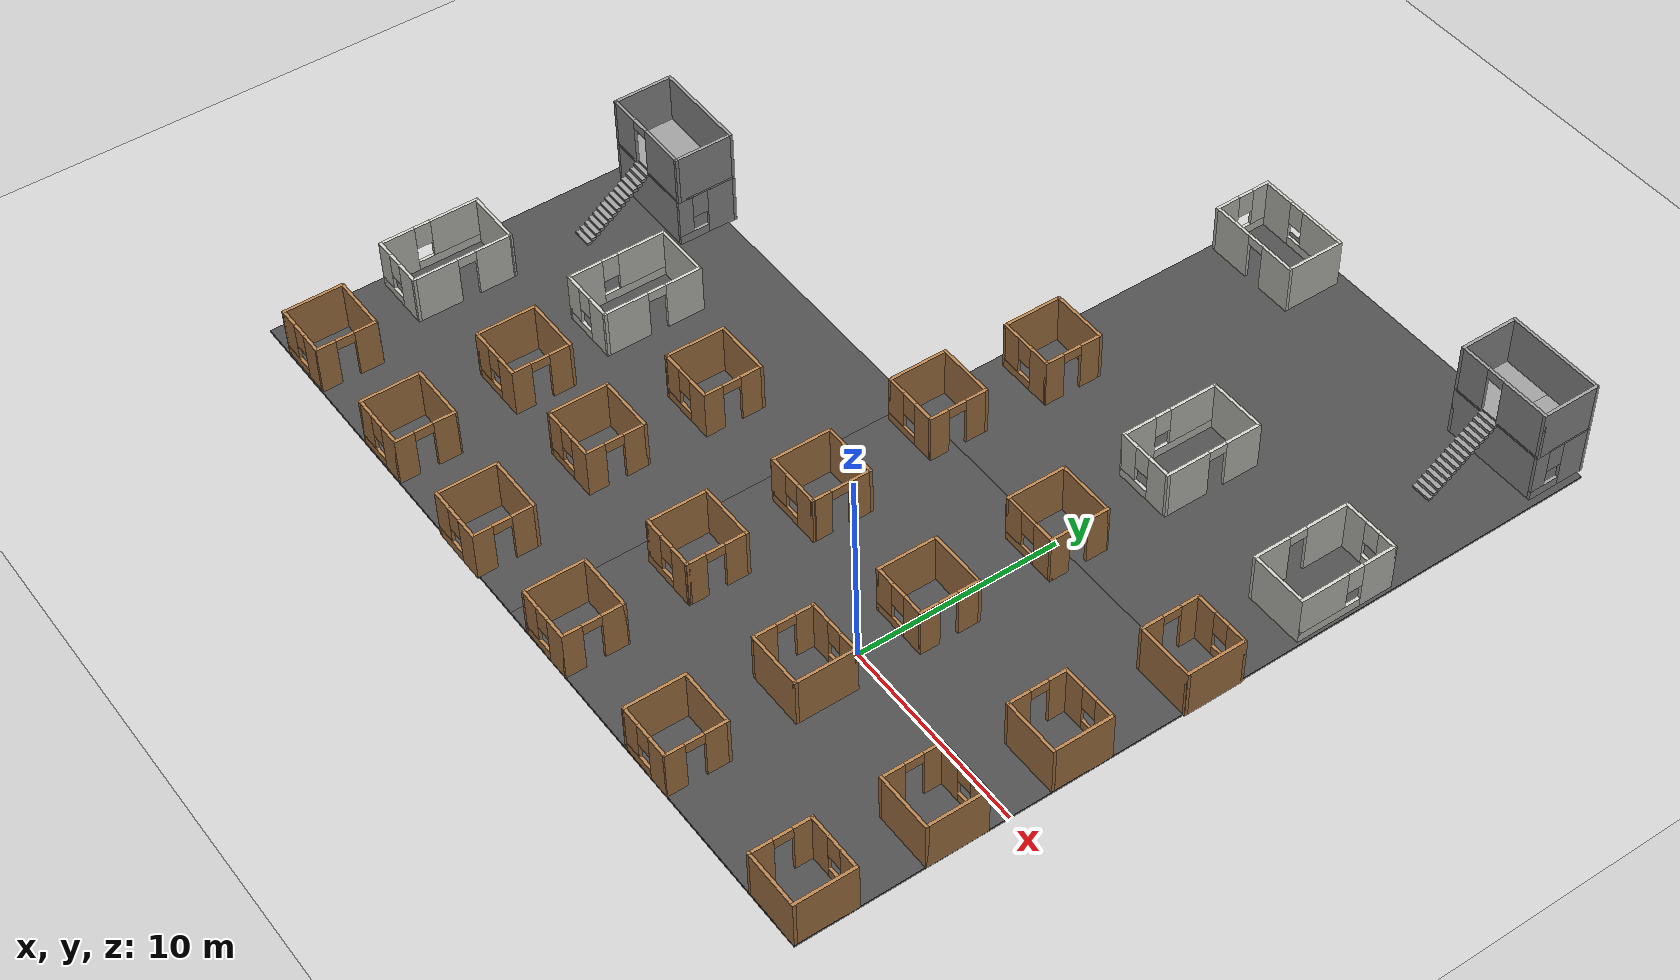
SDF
<sdf version="1.6">
 <world name="default">
  <light name="sun" type="directional">
   <pose>0 0 10 0 -0 0</pose>
   <diffuse>0.8 0.8 0.8 1</diffuse>
   <specular>0.2 0.2 0.2 1</specular>
   <attenuation>
    <range>1000</range>
    <constant>0.9</constant>
    <linear>0.01</linear>
    <quadratic>0.001</quadratic>
   </attenuation>
   <direction>-0.5 0.1 -0.9</direction>
  </light>
  <model name="ground_plane">
   <static>1</static>
   <link name="link">
    <collision name="collision">
     <geometry><plane><normal>0 0 1</normal><size>100 100</size></plane></geometry>
     <surface><friction><ode><mu>100</mu><mu2>50</mu2></ode></friction></surface>
    </collision>
    <visual name="visual">
     <cast_shadows>0</cast_shadows>
     <geometry><plane><normal>0 0 1</normal><size>100 100</size></plane></geometry>
     <material>
      <script><uri>file://media/materials/scripts/gazebo.material</uri><name>Gazebo/Grey</name></script>
     </material>
    </visual>
   </link>
  </model>
  <gravity>0 0 -9.8</gravity>
  <magnetic_field>6e-06 2.3e-05 -4.2e-05</magnetic_field>
  <atmosphere type="adiabatic"/>
  <physics name="default_physics" default="0" type="ode">
   <max_step_size>0.001</max_step_size>
   <real_time_factor>1</real_time_factor>
   <real_time_update_rate>1000</real_time_update_rate>
  </physics>
  <scene><ambient>0.4 0.4 0.4 1</ambient><background>0.7 0.7 0.7 1</background><shadows>1</shadows></scene>
  <spherical_coordinates>
   <surface_model>EARTH_WGS84</surface_model>
   <latitude_deg>0</latitude_deg>
   <longitude_deg>0</longitude_deg>
   <elevation>0</elevation>
   <heading_deg>0</heading_deg>
  </spherical_coordinates>
  <model name="asphalt_plane">
   <static>1</static>
   <link name="link">
    <collision name="collision"><geometry><box><size>20 20 0.1</size></box></geometry></collision>
    <visual name="visual">
     <cast_shadows>0</cast_shadows>
     <geometry><box><size>20 20 0.1</size></box></geometry>
     <material>
      <script>
       <uri>model://asphalt_plane/materials/scripts</uri>
       <uri>model://asphalt_plane/materials/textures</uri>
       <name>vrc/asphalt</name>
      </script>
     </material>
    </visual>
   </link>
  </model>
  <model name="asphalt_plane_0">
   <static>1</static>
   <link name="link">
    <collision name="collision"><geometry><box><size>20 20 0.1</size></box></geometry></collision>
    <visual name="visual">
     <cast_shadows>0</cast_shadows>
     <geometry><box><size>20 20 0.1</size></box></geometry>
     <material>
      <script>
       <uri>model://asphalt_plane/materials/scripts</uri>
       <uri>model://asphalt_plane/materials/textures</uri>
       <name>vrc/asphalt</name>
      </script>
     </material>
    </visual>
   </link>
   <pose>0 20 0 0 -0 0</pose>
  </model>
  <model name="house2">
   <pose>-7.33447 27.9705 0 0 -0 0</pose>
   <link name="Wall_10">
    <pose>-2.425 -0 0 0 -0 1.5708</pose>
    <visual name="Wall_10_Visual_0">
     <pose>-0.8725 0 1.25 0 -0 0</pose>
     <geometry><box><size>1.255 0.15 2.5</size></box></geometry>
     <material>
      <script><uri>file://media/materials/scripts/gazebo.material</uri><name>Gazebo/CeilingTiled</name></script>
      <ambient>1 1 1 1</ambient>
     </material>
     <meta><layer>0</layer></meta>
    </visual>
    <collision name="Wall_10_Collision_0">
     <geometry><box><size>1.255 0.15 2.5</size></box></geometry>
     <pose>-0.8725 0 1.25 0 -0 0</pose>
    </collision>
    <visual name="Wall_10_Visual_1">
     <pose>0.6275 0 0.25 0 -0 0</pose>
     <geometry><box><size>1.745 0.15 0.5</size></box></geometry>
     <material>
      <script><uri>file://media/materials/scripts/gazebo.material</uri><name>Gazebo/CeilingTiled</name></script>
      <ambient>1 1 1 1</ambient>
     </material>
     <meta><layer>0</layer></meta>
    </visual>
    <collision name="Wall_10_Collision_1">
     <geometry><box><size>1.745 0.15 0.5</size></box></geometry>
     <pose>0.6275 0 0.25 0 -0 0</pose>
    </collision>
    <visual name="Wall_10_Visual_2">
     <pose>1.0275 0 1.5 0 -0 0</pose>
     <geometry><box><size>0.945 0.15 2</size></box></geometry>
     <material>
      <script><uri>file://media/materials/scripts/gazebo.material</uri><name>Gazebo/CeilingTiled</name></script>
      <ambient>1 1 1 1</ambient>
     </material>
     <meta><layer>0</layer></meta>
    </visual>
    <collision name="Wall_10_Collision_2">
     <geometry><box><size>0.945 0.15 2</size></box></geometry>
     <pose>1.0275 0 1.5 0 -0 0</pose>
    </collision>
    <visual name="Wall_10_Visual_3">
     <pose>0.155 0 1.9 0 -0 0</pose>
     <geometry><box><size>0.8 0.15 1.2</size></box></geometry>
     <material>
      <script><uri>file://media/materials/scripts/gazebo.material</uri><name>Gazebo/CeilingTiled</name></script>
      <ambient>1 1 1 1</ambient>
     </material>
     <meta><layer>0</layer></meta>
    </visual>
    <collision name="Wall_10_Collision_3">
     <geometry><box><size>0.8 0.15 1.2</size></box></geometry>
     <pose>0.155 0 1.9 0 -0 0</pose>
    </collision>
   </link>
   <link name="Wall_7">
    <pose>0 1.425 0 0 -0 0</pose>
    <visual name="Wall_7_Visual_0">
     <pose>-1.6375 0 1.25 0 -0 0</pose>
     <geometry><box><size>1.725 0.15 2.5</size></box></geometry>
     <material>
      <script><uri>file://media/materials/scripts/gazebo.material</uri><name>Gazebo/CeilingTiled</name></script>
      <ambient>1 1 1 1</ambient>
     </material>
     <meta><layer>0</layer></meta>
    </visual>
    <collision name="Wall_7_Collision_0">
     <geometry><box><size>1.725 0.15 2.5</size></box></geometry>
     <pose>-1.6375 0 1.25 0 -0 0</pose>
    </collision>
    <visual name="Wall_7_Visual_1">
     <pose>0.8625 0 0.25 0 -0 0</pose>
     <geometry><box><size>3.275 0.15 0.5</size></box></geometry>
     <material>
      <script><uri>file://media/materials/scripts/gazebo.material</uri><name>Gazebo/CeilingTiled</name></script>
      <ambient>1 1 1 1</ambient>
     </material>
     <meta><layer>0</layer></meta>
    </visual>
    <collision name="Wall_7_Collision_1">
     <geometry><box><size>3.275 0.15 0.5</size></box></geometry>
     <pose>0.8625 0 0.25 0 -0 0</pose>
    </collision>
    <visual name="Wall_7_Visual_2">
     <pose>1.2625 0 1.5 0 -0 0</pose>
     <geometry><box><size>2.475 0.15 2</size></box></geometry>
     <material>
      <script><uri>file://media/materials/scripts/gazebo.material</uri><name>Gazebo/CeilingTiled</name></script>
      <ambient>1 1 1 1</ambient>
     </material>
     <meta><layer>0</layer></meta>
    </visual>
    <collision name="Wall_7_Collision_2">
     <geometry><box><size>2.475 0.15 2</size></box></geometry>
     <pose>1.2625 0 1.5 0 -0 0</pose>
    </collision>
    <visual name="Wall_7_Visual_3">
     <pose>-0.375 0 1.9 0 -0 0</pose>
     <geometry><box><size>0.8 0.15 1.2</size></box></geometry>
     <material>
      <script><uri>file://media/materials/scripts/gazebo.material</uri><name>Gazebo/CeilingTiled</name></script>
      <ambient>1 1 1 1</ambient>
     </material>
     <meta><layer>0</layer></meta>
    </visual>
    <collision name="Wall_7_Collision_3">
     <geometry><box><size>0.8 0.15 1.2</size></box></geometry>
     <pose>-0.375 0 1.9 0 -0 0</pose>
    </collision>
   </link>
   <link name="Wall_8">
    <collision name="Wall_8_Collision">
     <geometry><box><size>3 0.15 2.5</size></box></geometry>
     <pose>0 0 1.25 0 -0 0</pose>
    </collision>
    <visual name="Wall_8_Visual">
     <pose>0 0 1.25 0 -0 0</pose>
     <geometry><box><size>3 0.15 2.5</size></box></geometry>
     <material>
      <script><uri>file://media/materials/scripts/gazebo.material</uri><name>Gazebo/CeilingTiled</name></script>
      <ambient>1 1 1 1</ambient>
     </material>
     <meta><layer>0</layer></meta>
    </visual>
    <pose>2.425 -0 0 0 -0 -1.5708</pose>
   </link>
   <link name="Wall_9">
    <pose>0 -1.425 0 0 -0 3.14159</pose>
    <visual name="Wall_9_Visual_0">
     <pose>-1.5725 0 1.25 0 -0 0</pose>
     <geometry><box><size>1.855 0.15 2.5</size></box></geometry>
     <material>
      <script><uri>file://media/materials/scripts/gazebo.material</uri><name>Gazebo/CeilingTiled</name></script>
      <ambient>1 1 1 1</ambient>
     </material>
     <meta><layer>0</layer></meta>
    </visual>
    <collision name="Wall_9_Collision_0">
     <geometry><box><size>1.855 0.15 2.5</size></box></geometry>
     <pose>-1.5725 0 1.25 0 -0 0</pose>
    </collision>
    <visual name="Wall_9_Visual_1">
     <pose>1.3775 0 1.25 0 -0 0</pose>
     <geometry><box><size>2.245 0.15 2.5</size></box></geometry>
     <material>
      <script><uri>file://media/materials/scripts/gazebo.material</uri><name>Gazebo/CeilingTiled</name></script>
      <ambient>1 1 1 1</ambient>
     </material>
     <meta><layer>0</layer></meta>
    </visual>
    <collision name="Wall_9_Collision_1">
     <geometry><box><size>2.245 0.15 2.5</size></box></geometry>
     <pose>1.3775 0 1.25 0 -0 0</pose>
    </collision>
    <visual name="Wall_9_Visual_2">
     <pose>-0.195 0 2.25 0 -0 0</pose>
     <geometry><box><size>0.9 0.15 0.5</size></box></geometry>
     <material>
      <script><uri>file://media/materials/scripts/gazebo.material</uri><name>Gazebo/CeilingTiled</name></script>
      <ambient>1 1 1 1</ambient>
     </material>
     <meta><layer>0</layer></meta>
    </visual>
    <collision name="Wall_9_Collision_2">
     <geometry><box><size>0.9 0.15 0.5</size></box></geometry>
     <pose>-0.195 0 2.25 0 -0 0</pose>
    </collision>
   </link>
   <static>1</static>
  </model>
  <model name="asphalt_plane_1">
   <static>1</static>
   <link name="link">
    <collision name="collision"><geometry><box><size>20 20 0.1</size></box></geometry></collision>
    <visual name="visual">
     <cast_shadows>0</cast_shadows>
     <geometry><box><size>20 20 0.1</size></box></geometry>
     <material>
      <script>
       <uri>model://asphalt_plane/materials/scripts</uri>
       <uri>model://asphalt_plane/materials/textures</uri>
       <name>vrc/asphalt</name>
      </script>
     </material>
    </visual>
   </link>
   <pose>-20 0 0 0 -0 0</pose>
  </model>
  <model name="house1">
   <pose>8.5 -8.5 0 0 -0 0</pose>
   <link name="Wall_2">
    <pose>0 1.425 0 0 -0 0</pose>
    <visual name="Wall_2_Visual_0">
     <pose>-0.9275 0 1.25 0 -0 0</pose>
     <geometry><box><size>1.145 0.15 2.5</size></box></geometry>
     <material>
      <script><uri>file://media/materials/scripts/gazebo.material</uri><name>Gazebo/Wood</name></script>
      <ambient>1 1 1 1</ambient>
     </material>
     <meta><layer>0</layer></meta>
    </visual>
    <collision name="Wall_2_Collision_0">
     <geometry><box><size>1.145 0.15 2.5</size></box></geometry>
     <pose>-0.9275 0 1.25 0 -0 0</pose>
    </collision>
    <visual name="Wall_2_Visual_1">
     <pose>0.5725 0 0.25 0 -0 0</pose>
     <geometry><box><size>1.855 0.15 0.5</size></box></geometry>
     <material>
      <script><uri>file://media/materials/scripts/gazebo.material</uri><name>Gazebo/Wood</name></script>
      <ambient>1 1 1 1</ambient>
     </material>
     <meta><layer>0</layer></meta>
    </visual>
    <collision name="Wall_2_Collision_1">
     <geometry><box><size>1.855 0.15 0.5</size></box></geometry>
     <pose>0.5725 0 0.25 0 -0 0</pose>
    </collision>
    <visual name="Wall_2_Visual_2">
     <pose>0.9725 0 1.5 0 -0 0</pose>
     <geometry><box><size>1.055 0.15 2</size></box></geometry>
     <material>
      <script><uri>file://media/materials/scripts/gazebo.material</uri><name>Gazebo/Wood</name></script>
      <ambient>1 1 1 1</ambient>
     </material>
     <meta><layer>0</layer></meta>
    </visual>
    <collision name="Wall_2_Collision_2">
     <geometry><box><size>1.055 0.15 2</size></box></geometry>
     <pose>0.9725 0 1.5 0 -0 0</pose>
    </collision>
    <visual name="Wall_2_Visual_3">
     <pose>0.045 0 1.9 0 -0 0</pose>
     <geometry><box><size>0.8 0.15 1.2</size></box></geometry>
     <material>
      <script><uri>file://media/materials/scripts/gazebo.material</uri><name>Gazebo/Wood</name></script>
      <ambient>1 1 1 1</ambient>
     </material>
     <meta><layer>0</layer></meta>
    </visual>
    <collision name="Wall_2_Collision_3">
     <geometry><box><size>0.8 0.15 1.2</size></box></geometry>
     <pose>0.045 0 1.9 0 -0 0</pose>
    </collision>
   </link>
   <link name="Wall_3">
    <collision name="Wall_3_Collision">
     <geometry><box><size>3 0.15 2.5</size></box></geometry>
     <pose>0 0 1.25 0 -0 0</pose>
    </collision>
    <visual name="Wall_3_Visual">
     <pose>0 0 1.25 0 -0 0</pose>
     <geometry><box><size>3 0.15 2.5</size></box></geometry>
     <material>
      <script><uri>file://media/materials/scripts/gazebo.material</uri><name>Gazebo/Wood</name></script>
      <ambient>1 1 1 1</ambient>
     </material>
     <meta><layer>0</layer></meta>
    </visual>
    <pose>1.425 0 0 0 -0 -1.5708</pose>
   </link>
   <link name="Wall_4">
    <collision name="Wall_4_Collision">
     <geometry><box><size>3 0.15 2.5</size></box></geometry>
     <pose>0 0 1.25 0 -0 0</pose>
    </collision>
    <visual name="Wall_4_Visual">
     <pose>0 0 1.25 0 -0 0</pose>
     <geometry><box><size>3 0.15 2.5</size></box></geometry>
     <material>
      <script><uri>file://media/materials/scripts/gazebo.material</uri><name>Gazebo/Wood</name></script>
      <ambient>1 1 1 1</ambient>
     </material>
     <meta><layer>0</layer></meta>
    </visual>
    <pose>0 -1.425 0 0 -0 3.14159</pose>
   </link>
   <link name="Wall_5">
    <pose>-1.425 0 0 0 -0 1.5708</pose>
    <visual name="Wall_5_Visual_0">
     <pose>-0.9325 0 1.25 0 -0 0</pose>
     <geometry><box><size>1.135 0.15 2.5</size></box></geometry>
     <material>
      <script><uri>file://media/materials/scripts/gazebo.material</uri><name>Gazebo/Wood</name></script>
      <ambient>1 1 1 1</ambient>
     </material>
     <meta><layer>0</layer></meta>
    </visual>
    <collision name="Wall_5_Collision_0">
     <geometry><box><size>1.135 0.15 2.5</size></box></geometry>
     <pose>-0.9325 0 1.25 0 -0 0</pose>
    </collision>
    <visual name="Wall_5_Visual_1">
     <pose>1.0175 0 1.25 0 -0 0</pose>
     <geometry><box><size>0.965 0.15 2.5</size></box></geometry>
     <material>
      <script><uri>file://media/materials/scripts/gazebo.material</uri><name>Gazebo/Wood</name></script>
      <ambient>1 1 1 1</ambient>
     </material>
     <meta><layer>0</layer></meta>
    </visual>
    <collision name="Wall_5_Collision_1">
     <geometry><box><size>0.965 0.15 2.5</size></box></geometry>
     <pose>1.0175 0 1.25 0 -0 0</pose>
    </collision>
    <visual name="Wall_5_Visual_2">
     <pose>0.085 0 2.25 0 -0 0</pose>
     <geometry><box><size>0.9 0.15 0.5</size></box></geometry>
     <material>
      <script><uri>file://media/materials/scripts/gazebo.material</uri><name>Gazebo/Wood</name></script>
      <ambient>1 1 1 1</ambient>
     </material>
     <meta><layer>0</layer></meta>
    </visual>
    <collision name="Wall_5_Collision_2">
     <geometry><box><size>0.9 0.15 0.5</size></box></geometry>
     <pose>0.085 0 2.25 0 -0 0</pose>
    </collision>
   </link>
   <static>1</static>
  </model>
  <model name="house1_0">
   <pose>0 -8.5 0 0 -0 3.14</pose>
   <link name="Wall_2">
    <pose>0 1.425 0 0 -0 0</pose>
    <visual name="Wall_2_Visual_0">
     <pose>-0.9275 0 1.25 0 -0 0</pose>
     <geometry><box><size>1.145 0.15 2.5</size></box></geometry>
     <material>
      <script><uri>file://media/materials/scripts/gazebo.material</uri><name>Gazebo/Wood</name></script>
      <ambient>1 1 1 1</ambient>
     </material>
     <meta><layer>0</layer></meta>
    </visual>
    <collision name="Wall_2_Collision_0">
     <geometry><box><size>1.145 0.15 2.5</size></box></geometry>
     <pose>-0.9275 0 1.25 0 -0 0</pose>
    </collision>
    <visual name="Wall_2_Visual_1">
     <pose>0.5725 0 0.25 0 -0 0</pose>
     <geometry><box><size>1.855 0.15 0.5</size></box></geometry>
     <material>
      <script><uri>file://media/materials/scripts/gazebo.material</uri><name>Gazebo/Wood</name></script>
      <ambient>1 1 1 1</ambient>
     </material>
     <meta><layer>0</layer></meta>
    </visual>
    <collision name="Wall_2_Collision_1">
     <geometry><box><size>1.855 0.15 0.5</size></box></geometry>
     <pose>0.5725 0 0.25 0 -0 0</pose>
    </collision>
    <visual name="Wall_2_Visual_2">
     <pose>0.9725 0 1.5 0 -0 0</pose>
     <geometry><box><size>1.055 0.15 2</size></box></geometry>
     <material>
      <script><uri>file://media/materials/scripts/gazebo.material</uri><name>Gazebo/Wood</name></script>
      <ambient>1 1 1 1</ambient>
     </material>
     <meta><layer>0</layer></meta>
    </visual>
    <collision name="Wall_2_Collision_2">
     <geometry><box><size>1.055 0.15 2</size></box></geometry>
     <pose>0.9725 0 1.5 0 -0 0</pose>
    </collision>
    <visual name="Wall_2_Visual_3">
     <pose>0.045 0 1.9 0 -0 0</pose>
     <geometry><box><size>0.8 0.15 1.2</size></box></geometry>
     <material>
      <script><uri>file://media/materials/scripts/gazebo.material</uri><name>Gazebo/Wood</name></script>
      <ambient>1 1 1 1</ambient>
     </material>
     <meta><layer>0</layer></meta>
    </visual>
    <collision name="Wall_2_Collision_3">
     <geometry><box><size>0.8 0.15 1.2</size></box></geometry>
     <pose>0.045 0 1.9 0 -0 0</pose>
    </collision>
   </link>
   <link name="Wall_3">
    <collision name="Wall_3_Collision">
     <geometry><box><size>3 0.15 2.5</size></box></geometry>
     <pose>0 0 1.25 0 -0 0</pose>
    </collision>
    <visual name="Wall_3_Visual">
     <pose>0 0 1.25 0 -0 0</pose>
     <geometry><box><size>3 0.15 2.5</size></box></geometry>
     <material>
      <script><uri>file://media/materials/scripts/gazebo.material</uri><name>Gazebo/Wood</name></script>
      <ambient>1 1 1 1</ambient>
     </material>
     <meta><layer>0</layer></meta>
    </visual>
    <pose>1.425 0 0 0 -0 -1.5708</pose>
   </link>
   <link name="Wall_4">
    <collision name="Wall_4_Collision">
     <geometry><box><size>3 0.15 2.5</size></box></geometry>
     <pose>0 0 1.25 0 -0 0</pose>
    </collision>
    <visual name="Wall_4_Visual">
     <pose>0 0 1.25 0 -0 0</pose>
     <geometry><box><size>3 0.15 2.5</size></box></geometry>
     <material>
      <script><uri>file://media/materials/scripts/gazebo.material</uri><name>Gazebo/Wood</name></script>
      <ambient>1 1 1 1</ambient>
     </material>
     <meta><layer>0</layer></meta>
    </visual>
    <pose>0 -1.425 0 0 -0 3.14159</pose>
   </link>
   <link name="Wall_5">
    <pose>-1.425 0 0 0 -0 1.5708</pose>
    <visual name="Wall_5_Visual_0">
     <pose>-0.9325 0 1.25 0 -0 0</pose>
     <geometry><box><size>1.135 0.15 2.5</size></box></geometry>
     <material>
      <script><uri>file://media/materials/scripts/gazebo.material</uri><name>Gazebo/Wood</name></script>
      <ambient>1 1 1 1</ambient>
     </material>
     <meta><layer>0</layer></meta>
    </visual>
    <collision name="Wall_5_Collision_0">
     <geometry><box><size>1.135 0.15 2.5</size></box></geometry>
     <pose>-0.9325 0 1.25 0 -0 0</pose>
    </collision>
    <visual name="Wall_5_Visual_1">
     <pose>1.0175 0 1.25 0 -0 0</pose>
     <geometry><box><size>0.965 0.15 2.5</size></box></geometry>
     <material>
      <script><uri>file://media/materials/scripts/gazebo.material</uri><name>Gazebo/Wood</name></script>
      <ambient>1 1 1 1</ambient>
     </material>
     <meta><layer>0</layer></meta>
    </visual>
    <collision name="Wall_5_Collision_1">
     <geometry><box><size>0.965 0.15 2.5</size></box></geometry>
     <pose>1.0175 0 1.25 0 -0 0</pose>
    </collision>
    <visual name="Wall_5_Visual_2">
     <pose>0.085 0 2.25 0 -0 0</pose>
     <geometry><box><size>0.9 0.15 0.5</size></box></geometry>
     <material>
      <script><uri>file://media/materials/scripts/gazebo.material</uri><name>Gazebo/Wood</name></script>
      <ambient>1 1 1 1</ambient>
     </material>
     <meta><layer>0</layer></meta>
    </visual>
    <collision name="Wall_5_Collision_2">
     <geometry><box><size>0.9 0.15 0.5</size></box></geometry>
     <pose>0.085 0 2.25 0 -0 0</pose>
    </collision>
   </link>
   <static>1</static>
  </model>
  <model name="house1_0_clone">
   <pose>-26.8484 -8.47265 0 0 -0 3.14</pose>
   <link name="Wall_2">
    <pose>0 1.425 0 0 -0 0</pose>
    <visual name="Wall_2_Visual_0">
     <pose>-0.9275 0 1.25 0 -0 0</pose>
     <geometry><box><size>1.145 0.15 2.5</size></box></geometry>
     <material>
      <script><uri>file://media/materials/scripts/gazebo.material</uri><name>Gazebo/Wood</name></script>
      <ambient>1 1 1 1</ambient>
     </material>
     <meta><layer>0</layer></meta>
    </visual>
    <collision name="Wall_2_Collision_0">
     <geometry><box><size>1.145 0.15 2.5</size></box></geometry>
     <pose>-0.9275 0 1.25 0 -0 0</pose>
    </collision>
    <visual name="Wall_2_Visual_1">
     <pose>0.5725 0 0.25 0 -0 0</pose>
     <geometry><box><size>1.855 0.15 0.5</size></box></geometry>
     <material>
      <script><uri>file://media/materials/scripts/gazebo.material</uri><name>Gazebo/Wood</name></script>
      <ambient>1 1 1 1</ambient>
     </material>
     <meta><layer>0</layer></meta>
    </visual>
    <collision name="Wall_2_Collision_1">
     <geometry><box><size>1.855 0.15 0.5</size></box></geometry>
     <pose>0.5725 0 0.25 0 -0 0</pose>
    </collision>
    <visual name="Wall_2_Visual_2">
     <pose>0.9725 0 1.5 0 -0 0</pose>
     <geometry><box><size>1.055 0.15 2</size></box></geometry>
     <material>
      <script><uri>file://media/materials/scripts/gazebo.material</uri><name>Gazebo/Wood</name></script>
      <ambient>1 1 1 1</ambient>
     </material>
     <meta><layer>0</layer></meta>
    </visual>
    <collision name="Wall_2_Collision_2">
     <geometry><box><size>1.055 0.15 2</size></box></geometry>
     <pose>0.9725 0 1.5 0 -0 0</pose>
    </collision>
    <visual name="Wall_2_Visual_3">
     <pose>0.045 0 1.9 0 -0 0</pose>
     <geometry><box><size>0.8 0.15 1.2</size></box></geometry>
     <material>
      <script><uri>file://media/materials/scripts/gazebo.material</uri><name>Gazebo/Wood</name></script>
      <ambient>1 1 1 1</ambient>
     </material>
     <meta><layer>0</layer></meta>
    </visual>
    <collision name="Wall_2_Collision_3">
     <geometry><box><size>0.8 0.15 1.2</size></box></geometry>
     <pose>0.045 0 1.9 0 -0 0</pose>
    </collision>
   </link>
   <link name="Wall_3">
    <collision name="Wall_3_Collision">
     <geometry><box><size>3 0.15 2.5</size></box></geometry>
     <pose>0 0 1.25 0 -0 0</pose>
    </collision>
    <visual name="Wall_3_Visual">
     <pose>0 0 1.25 0 -0 0</pose>
     <geometry><box><size>3 0.15 2.5</size></box></geometry>
     <material>
      <script><uri>file://media/materials/scripts/gazebo.material</uri><name>Gazebo/Wood</name></script>
      <ambient>1 1 1 1</ambient>
     </material>
     <meta><layer>0</layer></meta>
    </visual>
    <pose>1.425 0 0 0 -0 -1.5708</pose>
   </link>
   <link name="Wall_4">
    <collision name="Wall_4_Collision">
     <geometry><box><size>3 0.15 2.5</size></box></geometry>
     <pose>0 0 1.25 0 -0 0</pose>
    </collision>
    <visual name="Wall_4_Visual">
     <pose>0 0 1.25 0 -0 0</pose>
     <geometry><box><size>3 0.15 2.5</size></box></geometry>
     <material>
      <script><uri>file://media/materials/scripts/gazebo.material</uri><name>Gazebo/Wood</name></script>
      <ambient>1 1 1 1</ambient>
     </material>
     <meta><layer>0</layer></meta>
    </visual>
    <pose>0 -1.425 0 0 -0 3.14159</pose>
   </link>
   <link name="Wall_5">
    <pose>-1.425 0 0 0 -0 1.5708</pose>
    <visual name="Wall_5_Visual_0">
     <pose>-0.9325 0 1.25 0 -0 0</pose>
     <geometry><box><size>1.135 0.15 2.5</size></box></geometry>
     <material>
      <script><uri>file://media/materials/scripts/gazebo.material</uri><name>Gazebo/Wood</name></script>
      <ambient>1 1 1 1</ambient>
     </material>
     <meta><layer>0</layer></meta>
    </visual>
    <collision name="Wall_5_Collision_0">
     <geometry><box><size>1.135 0.15 2.5</size></box></geometry>
     <pose>-0.9325 0 1.25 0 -0 0</pose>
    </collision>
    <visual name="Wall_5_Visual_1">
     <pose>1.0175 0 1.25 0 -0 0</pose>
     <geometry><box><size>0.965 0.15 2.5</size></box></geometry>
     <material>
      <script><uri>file://media/materials/scripts/gazebo.material</uri><name>Gazebo/Wood</name></script>
      <ambient>1 1 1 1</ambient>
     </material>
     <meta><layer>0</layer></meta>
    </visual>
    <collision name="Wall_5_Collision_1">
     <geometry><box><size>0.965 0.15 2.5</size></box></geometry>
     <pose>1.0175 0 1.25 0 -0 0</pose>
    </collision>
    <visual name="Wall_5_Visual_2">
     <pose>0.085 0 2.25 0 -0 0</pose>
     <geometry><box><size>0.9 0.15 0.5</size></box></geometry>
     <material>
      <script><uri>file://media/materials/scripts/gazebo.material</uri><name>Gazebo/Wood</name></script>
      <ambient>1 1 1 1</ambient>
     </material>
     <meta><layer>0</layer></meta>
    </visual>
    <collision name="Wall_5_Collision_2">
     <geometry><box><size>0.9 0.15 0.5</size></box></geometry>
     <pose>0.085 0 2.25 0 -0 0</pose>
    </collision>
   </link>
   <static>1</static>
  </model>
  <model name="duplex">
   <pose>-26.5 7.252 0 0 -0 3.14</pose>
   <link name="Floor_5">
    <pose>-0 -1.70219 2.5 0 -0 0</pose>
    <visual name="Floor_5_Visual_0">
     <pose>-1.28918 0 0.05 0 -0 0</pose>
     <geometry><box><size>2.42164 3 0.1</size></box></geometry>
     <material>
      <script><uri>file://media/materials/scripts/gazebo.material</uri><name>Gazebo/Grey</name></script>
      <ambient>1 1 1 1</ambient>
     </material>
     <meta><layer>1</layer></meta>
    </visual>
    <collision name="Floor_5_Collision_0">
     <geometry><box><size>2.42164 3 0.1</size></box></geometry>
     <pose>-1.28918 0 0.05 0 -0 0</pose>
    </collision>
    <visual name="Floor_5_Visual_1">
     <pose>1.21082 -0.047806 0.05 0 -0 0</pose>
     <geometry><box><size>2.57836 2.90439 0.1</size></box></geometry>
     <material>
      <script><uri>file://media/materials/scripts/gazebo.material</uri><name>Gazebo/Grey</name></script>
      <ambient>1 1 1 1</ambient>
     </material>
     <meta><layer>1</layer></meta>
    </visual>
    <collision name="Floor_5_Collision_1">
     <geometry><box><size>2.57836 2.90439 0.1</size></box></geometry>
     <pose>1.21082 -0.047806 0.05 0 -0 0</pose>
    </collision>
    <visual name="Floor_5_Visual_2">
     <pose>1.71082 1.45219 0.05 0 -0 0</pose>
     <geometry><box><size>1.57836 0.095611 0.1</size></box></geometry>
     <material>
      <script><uri>file://media/materials/scripts/gazebo.material</uri><name>Gazebo/Grey</name></script>
      <ambient>1 1 1 1</ambient>
     </material>
     <meta><layer>1</layer></meta>
    </visual>
    <collision name="Floor_5_Collision_2">
     <geometry><box><size>1.57836 0.095611 0.1</size></box></geometry>
     <pose>1.71082 1.45219 0.05 0 -0 0</pose>
    </collision>
   </link>
   <link name="Stairs_2">
    <visual name="Stairs_2_Visual_0">
     <pose>0.421637 3.08553 0.083333 0 -0 0</pose>
     <geometry><box><size>1 0.233333 0.166667</size></box></geometry>
     <material>
      <script><uri>file://media/materials/scripts/gazebo.material</uri><name>Gazebo/Grey</name></script>
      <ambient>1 1 1 1</ambient>
     </material>
     <meta><layer>0</layer></meta>
    </visual>
    <collision name="Stairs_2_Collision_0">
     <geometry><box><size>1 0.233333 0.166667</size></box></geometry>
     <pose>0.421637 3.08553 0.083333 0 -0 0</pose>
    </collision>
    <visual name="Stairs_2_Visual_1">
     <pose>0.421637 2.85219 0.25 0 -0 0</pose>
     <geometry><box><size>1 0.233333 0.166667</size></box></geometry>
     <material>
      <script><uri>file://media/materials/scripts/gazebo.material</uri><name>Gazebo/Grey</name></script>
      <ambient>1 1 1 1</ambient>
     </material>
     <meta><layer>0</layer></meta>
    </visual>
    <collision name="Stairs_2_Collision_1">
     <geometry><box><size>1 0.233333 0.166667</size></box></geometry>
     <pose>0.421637 2.85219 0.25 0 -0 0</pose>
    </collision>
    <visual name="Stairs_2_Visual_2">
     <pose>0.421637 2.61886 0.416667 0 -0 0</pose>
     <geometry><box><size>1 0.233333 0.166667</size></box></geometry>
     <material>
      <script><uri>file://media/materials/scripts/gazebo.material</uri><name>Gazebo/Grey</name></script>
      <ambient>1 1 1 1</ambient>
     </material>
     <meta><layer>0</layer></meta>
    </visual>
    <collision name="Stairs_2_Collision_2">
     <geometry><box><size>1 0.233333 0.166667</size></box></geometry>
     <pose>0.421637 2.61886 0.416667 0 -0 0</pose>
    </collision>
    <visual name="Stairs_2_Visual_3">
     <pose>0.421637 2.38553 0.583333 0 -0 0</pose>
     <geometry><box><size>1 0.233333 0.166667</size></box></geometry>
     <material>
      <script><uri>file://media/materials/scripts/gazebo.material</uri><name>Gazebo/Grey</name></script>
      <ambient>1 1 1 1</ambient>
     </material>
     <meta><layer>0</layer></meta>
    </visual>
    <collision name="Stairs_2_Collision_3">
     <geometry><box><size>1 0.233333 0.166667</size></box></geometry>
     <pose>0.421637 2.38553 0.583333 0 -0 0</pose>
    </collision>
    <visual name="Stairs_2_Visual_4">
     <pose>0.421637 2.15219 0.75 0 -0 0</pose>
     <geometry><box><size>1 0.233333 0.166667</size></box></geometry>
     <material>
      <script><uri>file://media/materials/scripts/gazebo.material</uri><name>Gazebo/Grey</name></script>
      <ambient>1 1 1 1</ambient>
     </material>
     <meta><layer>0</layer></meta>
    </visual>
    <collision name="Stairs_2_Collision_4">
     <geometry><box><size>1 0.233333 0.166667</size></box></geometry>
     <pose>0.421637 2.15219 0.75 0 -0 0</pose>
    </collision>
    <visual name="Stairs_2_Visual_5">
     <pose>0.421637 1.91886 0.916667 0 -0 0</pose>
     <geometry><box><size>1 0.233333 0.166667</size></box></geometry>
     <material>
      <script><uri>file://media/materials/scripts/gazebo.material</uri><name>Gazebo/Grey</name></script>
      <ambient>1 1 1 1</ambient>
     </material>
     <meta><layer>0</layer></meta>
    </visual>
    <collision name="Stairs_2_Collision_5">
     <geometry><box><size>1 0.233333 0.166667</size></box></geometry>
     <pose>0.421637 1.91886 0.916667 0 -0 0</pose>
    </collision>
    <visual name="Stairs_2_Visual_6">
     <pose>0.421637 1.68553 1.08333 0 -0 0</pose>
     <geometry><box><size>1 0.233333 0.166667</size></box></geometry>
     <material>
      <script><uri>file://media/materials/scripts/gazebo.material</uri><name>Gazebo/Grey</name></script>
      <ambient>1 1 1 1</ambient>
     </material>
     <meta><layer>0</layer></meta>
    </visual>
    <collision name="Stairs_2_Collision_6">
     <geometry><box><size>1 0.233333 0.166667</size></box></geometry>
     <pose>0.421637 1.68553 1.08333 0 -0 0</pose>
    </collision>
    <visual name="Stairs_2_Visual_7">
     <pose>0.421637 1.45219 1.25 0 -0 0</pose>
     <geometry><box><size>1 0.233333 0.166667</size></box></geometry>
     <material>
      <script><uri>file://media/materials/scripts/gazebo.material</uri><name>Gazebo/Grey</name></script>
      <ambient>1 1 1 1</ambient>
     </material>
     <meta><layer>0</layer></meta>
    </visual>
    <collision name="Stairs_2_Collision_7">
     <geometry><box><size>1 0.233333 0.166667</size></box></geometry>
     <pose>0.421637 1.45219 1.25 0 -0 0</pose>
    </collision>
    <visual name="Stairs_2_Visual_8">
     <pose>0.421637 1.21886 1.41667 0 -0 0</pose>
     <geometry><box><size>1 0.233333 0.166667</size></box></geometry>
     <material>
      <script><uri>file://media/materials/scripts/gazebo.material</uri><name>Gazebo/Grey</name></script>
      <ambient>1 1 1 1</ambient>
     </material>
     <meta><layer>0</layer></meta>
    </visual>
    <collision name="Stairs_2_Collision_8">
     <geometry><box><size>1 0.233333 0.166667</size></box></geometry>
     <pose>0.421637 1.21886 1.41667 0 -0 0</pose>
    </collision>
    <visual name="Stairs_2_Visual_9">
     <pose>0.421637 0.985528 1.58333 0 -0 0</pose>
     <geometry><box><size>1 0.233333 0.166667</size></box></geometry>
     <material>
      <script><uri>file://media/materials/scripts/gazebo.material</uri><name>Gazebo/Grey</name></script>
      <ambient>1 1 1 1</ambient>
     </material>
     <meta><layer>0</layer></meta>
    </visual>
    <collision name="Stairs_2_Collision_9">
     <geometry><box><size>1 0.233333 0.166667</size></box></geometry>
     <pose>0.421637 0.985528 1.58333 0 -0 0</pose>
    </collision>
    <visual name="Stairs_2_Visual_10">
     <pose>0.421637 0.752194 1.75 0 -0 0</pose>
     <geometry><box><size>1 0.233333 0.166667</size></box></geometry>
     <material>
      <script><uri>file://media/materials/scripts/gazebo.material</uri><name>Gazebo/Grey</name></script>
      <ambient>1 1 1 1</ambient>
     </material>
     <meta><layer>0</layer></meta>
    </visual>
    <collision name="Stairs_2_Collision_10">
     <geometry><box><size>1 0.233333 0.166667</size></box></geometry>
     <pose>0.421637 0.752194 1.75 0 -0 0</pose>
    </collision>
    <visual name="Stairs_2_Visual_11">
     <pose>0.421637 0.518861 1.91667 0 -0 0</pose>
     <geometry><box><size>1 0.233333 0.166667</size></box></geometry>
     <material>
      <script><uri>file://media/materials/scripts/gazebo.material</uri><name>Gazebo/Grey</name></script>
      <ambient>1 1 1 1</ambient>
     </material>
     <meta><layer>0</layer></meta>
    </visual>
    <collision name="Stairs_2_Collision_11">
     <geometry><box><size>1 0.233333 0.166667</size></box></geometry>
     <pose>0.421637 0.518861 1.91667 0 -0 0</pose>
    </collision>
    <visual name="Stairs_2_Visual_12">
     <pose>0.421637 0.285528 2.08333 0 -0 0</pose>
     <geometry><box><size>1 0.233333 0.166667</size></box></geometry>
     <material>
      <script><uri>file://media/materials/scripts/gazebo.material</uri><name>Gazebo/Grey</name></script>
      <ambient>1 1 1 1</ambient>
     </material>
     <meta><layer>0</layer></meta>
    </visual>
    <collision name="Stairs_2_Collision_12">
     <geometry><box><size>1 0.233333 0.166667</size></box></geometry>
     <pose>0.421637 0.285528 2.08333 0 -0 0</pose>
    </collision>
    <visual name="Stairs_2_Visual_13">
     <pose>0.421637 0.052195 2.25 0 -0 0</pose>
     <geometry><box><size>1 0.233333 0.166667</size></box></geometry>
     <material>
      <script><uri>file://media/materials/scripts/gazebo.material</uri><name>Gazebo/Grey</name></script>
      <ambient>1 1 1 1</ambient>
     </material>
     <meta><layer>0</layer></meta>
    </visual>
    <collision name="Stairs_2_Collision_13">
     <geometry><box><size>1 0.233333 0.166667</size></box></geometry>
     <pose>0.421637 0.052195 2.25 0 -0 0</pose>
    </collision>
    <visual name="Stairs_2_Visual_14">
     <pose>0.421637 -0.181139 2.41667 0 -0 0</pose>
     <geometry><box><size>1 0.233333 0.166667</size></box></geometry>
     <material>
      <script><uri>file://media/materials/scripts/gazebo.material</uri><name>Gazebo/Grey</name></script>
      <ambient>1 1 1 1</ambient>
     </material>
     <meta><layer>0</layer></meta>
    </visual>
    <collision name="Stairs_2_Collision_14">
     <geometry><box><size>1 0.233333 0.166667</size></box></geometry>
     <pose>0.421637 -0.181139 2.41667 0 -0 0</pose>
    </collision>
   </link>
   <link name="Wall_33">
    <collision name="Wall_33_Collision">
     <geometry><box><size>5 0.15 2.5</size></box></geometry>
     <pose>0 0 1.25 0 -0 0</pose>
    </collision>
    <visual name="Wall_33_Visual">
     <pose>0 0 1.25 0 -0 0</pose>
     <geometry><box><size>5 0.15 2.5</size></box></geometry>
     <material>
      <script><uri>file://media/materials/scripts/gazebo.material</uri><name>Gazebo/Grey</name></script>
      <ambient>1 1 1 1</ambient>
     </material>
     <meta><layer>0</layer></meta>
    </visual>
    <pose>-0 -0.277195 0 0 -0 0</pose>
   </link>
   <link name="Wall_34">
    <collision name="Wall_34_Collision">
     <geometry><box><size>3 0.15 2.5</size></box></geometry>
     <pose>0 0 1.25 0 -0 0</pose>
    </collision>
    <visual name="Wall_34_Visual">
     <pose>0 0 1.25 0 -0 0</pose>
     <geometry><box><size>3 0.15 2.5</size></box></geometry>
     <material>
      <script><uri>file://media/materials/scripts/gazebo.material</uri><name>Gazebo/Grey</name></script>
      <ambient>1 1 1 1</ambient>
     </material>
     <meta><layer>0</layer></meta>
    </visual>
    <pose>2.425 -1.70219 0 0 -0 -1.5708</pose>
   </link>
   <link name="Wall_35">
    <pose>-0 -3.12719 0 0 -0 3.14159</pose>
    <visual name="Wall_35_Visual_0">
     <pose>-1.69725 0 1.25 0 -0 0</pose>
     <geometry><box><size>1.60549 0.15 2.5</size></box></geometry>
     <material>
      <script><uri>file://media/materials/scripts/gazebo.material</uri><name>Gazebo/Grey</name></script>
      <ambient>1 1 1 1</ambient>
     </material>
     <meta><layer>0</layer></meta>
    </visual>
    <collision name="Wall_35_Collision_0">
     <geometry><box><size>1.60549 0.15 2.5</size></box></geometry>
     <pose>-1.69725 0 1.25 0 -0 0</pose>
    </collision>
    <visual name="Wall_35_Visual_1">
     <pose>1.25275 0 1.25 0 -0 0</pose>
     <geometry><box><size>2.49451 0.15 2.5</size></box></geometry>
     <material>
      <script><uri>file://media/materials/scripts/gazebo.material</uri><name>Gazebo/Grey</name></script>
      <ambient>1 1 1 1</ambient>
     </material>
     <meta><layer>0</layer></meta>
    </visual>
    <collision name="Wall_35_Collision_1">
     <geometry><box><size>2.49451 0.15 2.5</size></box></geometry>
     <pose>1.25275 0 1.25 0 -0 0</pose>
    </collision>
    <visual name="Wall_35_Visual_2">
     <pose>-0.444507 0 2.25 0 -0 0</pose>
     <geometry><box><size>0.9 0.15 0.5</size></box></geometry>
     <material>
      <script><uri>file://media/materials/scripts/gazebo.material</uri><name>Gazebo/Grey</name></script>
      <ambient>1 1 1 1</ambient>
     </material>
     <meta><layer>0</layer></meta>
    </visual>
    <collision name="Wall_35_Collision_2">
     <geometry><box><size>0.9 0.15 0.5</size></box></geometry>
     <pose>-0.444507 0 2.25 0 -0 0</pose>
    </collision>
   </link>
   <link name="Wall_36">
    <pose>-2.425 -1.70219 0 0 -0 1.5708</pose>
    <visual name="Wall_36_Visual_0">
     <pose>-0.767883 0 1.25 0 -0 0</pose>
     <geometry><box><size>1.46423 0.15 2.5</size></box></geometry>
     <material>
      <script><uri>file://media/materials/scripts/gazebo.material</uri><name>Gazebo/Grey</name></script>
      <ambient>1 1 1 1</ambient>
     </material>
     <meta><layer>0</layer></meta>
    </visual>
    <collision name="Wall_36_Collision_0">
     <geometry><box><size>1.46423 0.15 2.5</size></box></geometry>
     <pose>-0.767883 0 1.25 0 -0 0</pose>
    </collision>
    <visual name="Wall_36_Visual_1">
     <pose>0.732117 0 0.25 0 -0 0</pose>
     <geometry><box><size>1.53577 0.15 0.5</size></box></geometry>
     <material>
      <script><uri>file://media/materials/scripts/gazebo.material</uri><name>Gazebo/Grey</name></script>
      <ambient>1 1 1 1</ambient>
     </material>
     <meta><layer>0</layer></meta>
    </visual>
    <collision name="Wall_36_Collision_1">
     <geometry><box><size>1.53577 0.15 0.5</size></box></geometry>
     <pose>0.732117 0 0.25 0 -0 0</pose>
    </collision>
    <visual name="Wall_36_Visual_2">
     <pose>1.13212 0 1.5 0 -0 0</pose>
     <geometry><box><size>0.735767 0.15 2</size></box></geometry>
     <material>
      <script><uri>file://media/materials/scripts/gazebo.material</uri><name>Gazebo/Grey</name></script>
      <ambient>1 1 1 1</ambient>
     </material>
     <meta><layer>0</layer></meta>
    </visual>
    <collision name="Wall_36_Collision_2">
     <geometry><box><size>0.735767 0.15 2</size></box></geometry>
     <pose>1.13212 0 1.5 0 -0 0</pose>
    </collision>
    <visual name="Wall_36_Visual_3">
     <pose>0.364233 0 1.9 0 -0 0</pose>
     <geometry><box><size>0.8 0.15 1.2</size></box></geometry>
     <material>
      <script><uri>file://media/materials/scripts/gazebo.material</uri><name>Gazebo/Grey</name></script>
      <ambient>1 1 1 1</ambient>
     </material>
     <meta><layer>0</layer></meta>
    </visual>
    <collision name="Wall_36_Collision_3">
     <geometry><box><size>0.8 0.15 1.2</size></box></geometry>
     <pose>0.364233 0 1.9 0 -0 0</pose>
    </collision>
   </link>
   <link name="Wall_47">
    <pose>-0 -0.277194 2.5 0 -0 0</pose>
    <visual name="Wall_47_Visual_0">
     <pose>-1.25275 0 1.25 0 -0 0</pose>
     <geometry><box><size>2.49451 0.15 2.5</size></box></geometry>
     <material>
      <script><uri>file://media/materials/scripts/gazebo.material</uri><name>Gazebo/Grey</name></script>
      <ambient>1 1 1 1</ambient>
     </material>
     <meta><layer>1</layer></meta>
    </visual>
    <collision name="Wall_47_Collision_0">
     <geometry><box><size>2.49451 0.15 2.5</size></box></geometry>
     <pose>-1.25275 0 1.25 0 -0 0</pose>
    </collision>
    <visual name="Wall_47_Visual_1">
     <pose>1.69725 0 1.25 0 -0 0</pose>
     <geometry><box><size>1.60549 0.15 2.5</size></box></geometry>
     <material>
      <script><uri>file://media/materials/scripts/gazebo.material</uri><name>Gazebo/Grey</name></script>
      <ambient>1 1 1 1</ambient>
     </material>
     <meta><layer>1</layer></meta>
    </visual>
    <collision name="Wall_47_Collision_1">
     <geometry><box><size>1.60549 0.15 2.5</size></box></geometry>
     <pose>1.69725 0 1.25 0 -0 0</pose>
    </collision>
    <visual name="Wall_47_Visual_2">
     <pose>0.444507 0 2.25 0 -0 0</pose>
     <geometry><box><size>0.9 0.15 0.5</size></box></geometry>
     <material>
      <script><uri>file://media/materials/scripts/gazebo.material</uri><name>Gazebo/Grey</name></script>
      <ambient>1 1 1 1</ambient>
     </material>
     <meta><layer>1</layer></meta>
    </visual>
    <collision name="Wall_47_Collision_2">
     <geometry><box><size>0.9 0.15 0.5</size></box></geometry>
     <pose>0.444507 0 2.25 0 -0 0</pose>
    </collision>
   </link>
   <link name="Wall_48">
    <collision name="Wall_48_Collision">
     <geometry><box><size>3 0.15 2.5</size></box></geometry>
     <pose>0 0 1.25 0 -0 0</pose>
    </collision>
    <visual name="Wall_48_Visual">
     <pose>0 0 1.25 0 -0 0</pose>
     <geometry><box><size>3 0.15 2.5</size></box></geometry>
     <material>
      <script><uri>file://media/materials/scripts/gazebo.material</uri><name>Gazebo/Grey</name></script>
      <ambient>1 1 1 1</ambient>
     </material>
     <meta><layer>1</layer></meta>
    </visual>
    <pose>2.425 -1.70219 2.5 0 -0 -1.5708</pose>
   </link>
   <link name="Wall_49">
    <collision name="Wall_49_Collision">
     <geometry><box><size>5 0.15 2.5</size></box></geometry>
     <pose>0 0 1.25 0 -0 0</pose>
    </collision>
    <visual name="Wall_49_Visual">
     <pose>0 0 1.25 0 -0 0</pose>
     <geometry><box><size>5 0.15 2.5</size></box></geometry>
     <material>
      <script><uri>file://media/materials/scripts/gazebo.material</uri><name>Gazebo/Grey</name></script>
      <ambient>1 1 1 1</ambient>
     </material>
     <meta><layer>1</layer></meta>
    </visual>
    <pose>-0 -3.12719 2.5 0 -0 3.14159</pose>
   </link>
   <link name="Wall_50">
    <collision name="Wall_50_Collision">
     <geometry><box><size>3 0.15 2.5</size></box></geometry>
     <pose>0 0 1.25 0 -0 0</pose>
    </collision>
    <visual name="Wall_50_Visual">
     <pose>0 0 1.25 0 -0 0</pose>
     <geometry><box><size>3 0.15 2.5</size></box></geometry>
     <material>
      <script><uri>file://media/materials/scripts/gazebo.material</uri><name>Gazebo/Grey</name></script>
      <ambient>1 1 1 1</ambient>
     </material>
     <meta><layer>1</layer></meta>
    </visual>
    <pose>-2.425 -1.70219 2.5 0 -0 1.5708</pose>
   </link>
   <static>1</static>
  </model>
  <model name="house1_1">
   <pose>8.5 3.5 0 0 -0 0</pose>
   <link name="Wall_2">
    <pose>0 1.425 0 0 -0 0</pose>
    <visual name="Wall_2_Visual_0">
     <pose>-0.9275 0 1.25 0 -0 0</pose>
     <geometry><box><size>1.145 0.15 2.5</size></box></geometry>
     <material>
      <script><uri>file://media/materials/scripts/gazebo.material</uri><name>Gazebo/Wood</name></script>
      <ambient>1 1 1 1</ambient>
     </material>
     <meta><layer>0</layer></meta>
    </visual>
    <collision name="Wall_2_Collision_0">
     <geometry><box><size>1.145 0.15 2.5</size></box></geometry>
     <pose>-0.9275 0 1.25 0 -0 0</pose>
    </collision>
    <visual name="Wall_2_Visual_1">
     <pose>0.5725 0 0.25 0 -0 0</pose>
     <geometry><box><size>1.855 0.15 0.5</size></box></geometry>
     <material>
      <script><uri>file://media/materials/scripts/gazebo.material</uri><name>Gazebo/Wood</name></script>
      <ambient>1 1 1 1</ambient>
     </material>
     <meta><layer>0</layer></meta>
    </visual>
    <collision name="Wall_2_Collision_1">
     <geometry><box><size>1.855 0.15 0.5</size></box></geometry>
     <pose>0.5725 0 0.25 0 -0 0</pose>
    </collision>
    <visual name="Wall_2_Visual_2">
     <pose>0.9725 0 1.5 0 -0 0</pose>
     <geometry><box><size>1.055 0.15 2</size></box></geometry>
     <material>
      <script><uri>file://media/materials/scripts/gazebo.material</uri><name>Gazebo/Wood</name></script>
      <ambient>1 1 1 1</ambient>
     </material>
     <meta><layer>0</layer></meta>
    </visual>
    <collision name="Wall_2_Collision_2">
     <geometry><box><size>1.055 0.15 2</size></box></geometry>
     <pose>0.9725 0 1.5 0 -0 0</pose>
    </collision>
    <visual name="Wall_2_Visual_3">
     <pose>0.045 0 1.9 0 -0 0</pose>
     <geometry><box><size>0.8 0.15 1.2</size></box></geometry>
     <material>
      <script><uri>file://media/materials/scripts/gazebo.material</uri><name>Gazebo/Wood</name></script>
      <ambient>1 1 1 1</ambient>
     </material>
     <meta><layer>0</layer></meta>
    </visual>
    <collision name="Wall_2_Collision_3">
     <geometry><box><size>0.8 0.15 1.2</size></box></geometry>
     <pose>0.045 0 1.9 0 -0 0</pose>
    </collision>
   </link>
   <link name="Wall_3">
    <collision name="Wall_3_Collision">
     <geometry><box><size>3 0.15 2.5</size></box></geometry>
     <pose>0 0 1.25 0 -0 0</pose>
    </collision>
    <visual name="Wall_3_Visual">
     <pose>0 0 1.25 0 -0 0</pose>
     <geometry><box><size>3 0.15 2.5</size></box></geometry>
     <material>
      <script><uri>file://media/materials/scripts/gazebo.material</uri><name>Gazebo/Wood</name></script>
      <ambient>1 1 1 1</ambient>
     </material>
     <meta><layer>0</layer></meta>
    </visual>
    <pose>1.425 0 0 0 -0 -1.5708</pose>
   </link>
   <link name="Wall_4">
    <collision name="Wall_4_Collision">
     <geometry><box><size>3 0.15 2.5</size></box></geometry>
     <pose>0 0 1.25 0 -0 0</pose>
    </collision>
    <visual name="Wall_4_Visual">
     <pose>0 0 1.25 0 -0 0</pose>
     <geometry><box><size>3 0.15 2.5</size></box></geometry>
     <material>
      <script><uri>file://media/materials/scripts/gazebo.material</uri><name>Gazebo/Wood</name></script>
      <ambient>1 1 1 1</ambient>
     </material>
     <meta><layer>0</layer></meta>
    </visual>
    <pose>0 -1.425 0 0 -0 3.14159</pose>
   </link>
   <link name="Wall_5">
    <pose>-1.425 0 0 0 -0 1.5708</pose>
    <visual name="Wall_5_Visual_0">
     <pose>-0.9325 0 1.25 0 -0 0</pose>
     <geometry><box><size>1.135 0.15 2.5</size></box></geometry>
     <material>
      <script><uri>file://media/materials/scripts/gazebo.material</uri><name>Gazebo/Wood</name></script>
      <ambient>1 1 1 1</ambient>
     </material>
     <meta><layer>0</layer></meta>
    </visual>
    <collision name="Wall_5_Collision_0">
     <geometry><box><size>1.135 0.15 2.5</size></box></geometry>
     <pose>-0.9325 0 1.25 0 -0 0</pose>
    </collision>
    <visual name="Wall_5_Visual_1">
     <pose>1.0175 0 1.25 0 -0 0</pose>
     <geometry><box><size>0.965 0.15 2.5</size></box></geometry>
     <material>
      <script><uri>file://media/materials/scripts/gazebo.material</uri><name>Gazebo/Wood</name></script>
      <ambient>1 1 1 1</ambient>
     </material>
     <meta><layer>0</layer></meta>
    </visual>
    <collision name="Wall_5_Collision_1">
     <geometry><box><size>0.965 0.15 2.5</size></box></geometry>
     <pose>1.0175 0 1.25 0 -0 0</pose>
    </collision>
    <visual name="Wall_5_Visual_2">
     <pose>0.085 0 2.25 0 -0 0</pose>
     <geometry><box><size>0.9 0.15 0.5</size></box></geometry>
     <material>
      <script><uri>file://media/materials/scripts/gazebo.material</uri><name>Gazebo/Wood</name></script>
      <ambient>1 1 1 1</ambient>
     </material>
     <meta><layer>0</layer></meta>
    </visual>
    <collision name="Wall_5_Collision_2">
     <geometry><box><size>0.9 0.15 0.5</size></box></geometry>
     <pose>0.085 0 2.25 0 -0 0</pose>
    </collision>
   </link>
   <static>1</static>
  </model>
  <model name="house1_1_clone">
   <pose>8.59732 10 0 0 -0 0</pose>
   <link name="Wall_2">
    <pose>0 1.425 0 0 -0 0</pose>
    <visual name="Wall_2_Visual_0">
     <pose>-0.9275 0 1.25 0 -0 0</pose>
     <geometry><box><size>1.145 0.15 2.5</size></box></geometry>
     <material>
      <script><uri>file://media/materials/scripts/gazebo.material</uri><name>Gazebo/Wood</name></script>
      <ambient>1 1 1 1</ambient>
     </material>
     <meta><layer>0</layer></meta>
    </visual>
    <collision name="Wall_2_Collision_0">
     <geometry><box><size>1.145 0.15 2.5</size></box></geometry>
     <pose>-0.9275 0 1.25 0 -0 0</pose>
    </collision>
    <visual name="Wall_2_Visual_1">
     <pose>0.5725 0 0.25 0 -0 0</pose>
     <geometry><box><size>1.855 0.15 0.5</size></box></geometry>
     <material>
      <script><uri>file://media/materials/scripts/gazebo.material</uri><name>Gazebo/Wood</name></script>
      <ambient>1 1 1 1</ambient>
     </material>
     <meta><layer>0</layer></meta>
    </visual>
    <collision name="Wall_2_Collision_1">
     <geometry><box><size>1.855 0.15 0.5</size></box></geometry>
     <pose>0.5725 0 0.25 0 -0 0</pose>
    </collision>
    <visual name="Wall_2_Visual_2">
     <pose>0.9725 0 1.5 0 -0 0</pose>
     <geometry><box><size>1.055 0.15 2</size></box></geometry>
     <material>
      <script><uri>file://media/materials/scripts/gazebo.material</uri><name>Gazebo/Wood</name></script>
      <ambient>1 1 1 1</ambient>
     </material>
     <meta><layer>0</layer></meta>
    </visual>
    <collision name="Wall_2_Collision_2">
     <geometry><box><size>1.055 0.15 2</size></box></geometry>
     <pose>0.9725 0 1.5 0 -0 0</pose>
    </collision>
    <visual name="Wall_2_Visual_3">
     <pose>0.045 0 1.9 0 -0 0</pose>
     <geometry><box><size>0.8 0.15 1.2</size></box></geometry>
     <material>
      <script><uri>file://media/materials/scripts/gazebo.material</uri><name>Gazebo/Wood</name></script>
      <ambient>1 1 1 1</ambient>
     </material>
     <meta><layer>0</layer></meta>
    </visual>
    <collision name="Wall_2_Collision_3">
     <geometry><box><size>0.8 0.15 1.2</size></box></geometry>
     <pose>0.045 0 1.9 0 -0 0</pose>
    </collision>
   </link>
   <link name="Wall_3">
    <collision name="Wall_3_Collision">
     <geometry><box><size>3 0.15 2.5</size></box></geometry>
     <pose>0 0 1.25 0 -0 0</pose>
    </collision>
    <visual name="Wall_3_Visual">
     <pose>0 0 1.25 0 -0 0</pose>
     <geometry><box><size>3 0.15 2.5</size></box></geometry>
     <material>
      <script><uri>file://media/materials/scripts/gazebo.material</uri><name>Gazebo/Wood</name></script>
      <ambient>1 1 1 1</ambient>
     </material>
     <meta><layer>0</layer></meta>
    </visual>
    <pose>1.425 0 0 0 -0 -1.5708</pose>
   </link>
   <link name="Wall_4">
    <collision name="Wall_4_Collision">
     <geometry><box><size>3 0.15 2.5</size></box></geometry>
     <pose>0 0 1.25 0 -0 0</pose>
    </collision>
    <visual name="Wall_4_Visual">
     <pose>0 0 1.25 0 -0 0</pose>
     <geometry><box><size>3 0.15 2.5</size></box></geometry>
     <material>
      <script><uri>file://media/materials/scripts/gazebo.material</uri><name>Gazebo/Wood</name></script>
      <ambient>1 1 1 1</ambient>
     </material>
     <meta><layer>0</layer></meta>
    </visual>
    <pose>0 -1.425 0 0 -0 3.14159</pose>
   </link>
   <link name="Wall_5">
    <pose>-1.425 0 0 0 -0 1.5708</pose>
    <visual name="Wall_5_Visual_0">
     <pose>-0.9325 0 1.25 0 -0 0</pose>
     <geometry><box><size>1.135 0.15 2.5</size></box></geometry>
     <material>
      <script><uri>file://media/materials/scripts/gazebo.material</uri><name>Gazebo/Wood</name></script>
      <ambient>1 1 1 1</ambient>
     </material>
     <meta><layer>0</layer></meta>
    </visual>
    <collision name="Wall_5_Collision_0">
     <geometry><box><size>1.135 0.15 2.5</size></box></geometry>
     <pose>-0.9325 0 1.25 0 -0 0</pose>
    </collision>
    <visual name="Wall_5_Visual_1">
     <pose>1.0175 0 1.25 0 -0 0</pose>
     <geometry><box><size>0.965 0.15 2.5</size></box></geometry>
     <material>
      <script><uri>file://media/materials/scripts/gazebo.material</uri><name>Gazebo/Wood</name></script>
      <ambient>1 1 1 1</ambient>
     </material>
     <meta><layer>0</layer></meta>
    </visual>
    <collision name="Wall_5_Collision_1">
     <geometry><box><size>0.965 0.15 2.5</size></box></geometry>
     <pose>1.0175 0 1.25 0 -0 0</pose>
    </collision>
    <visual name="Wall_5_Visual_2">
     <pose>0.085 0 2.25 0 -0 0</pose>
     <geometry><box><size>0.9 0.15 0.5</size></box></geometry>
     <material>
      <script><uri>file://media/materials/scripts/gazebo.material</uri><name>Gazebo/Wood</name></script>
      <ambient>1 1 1 1</ambient>
     </material>
     <meta><layer>0</layer></meta>
    </visual>
    <collision name="Wall_5_Collision_2">
     <geometry><box><size>0.9 0.15 0.5</size></box></geometry>
     <pose>0.085 0 2.25 0 -0 0</pose>
    </collision>
   </link>
   <static>1</static>
  </model>
  <model name="house1_1_clone_0">
   <pose>8.51979 -2.5 0 0 -0 0</pose>
   <link name="Wall_2">
    <pose>0 1.425 0 0 -0 0</pose>
    <visual name="Wall_2_Visual_0">
     <pose>-0.9275 0 1.25 0 -0 0</pose>
     <geometry><box><size>1.145 0.15 2.5</size></box></geometry>
     <material>
      <script><uri>file://media/materials/scripts/gazebo.material</uri><name>Gazebo/Wood</name></script>
      <ambient>1 1 1 1</ambient>
     </material>
     <meta><layer>0</layer></meta>
    </visual>
    <collision name="Wall_2_Collision_0">
     <geometry><box><size>1.145 0.15 2.5</size></box></geometry>
     <pose>-0.9275 0 1.25 0 -0 0</pose>
    </collision>
    <visual name="Wall_2_Visual_1">
     <pose>0.5725 0 0.25 0 -0 0</pose>
     <geometry><box><size>1.855 0.15 0.5</size></box></geometry>
     <material>
      <script><uri>file://media/materials/scripts/gazebo.material</uri><name>Gazebo/Wood</name></script>
      <ambient>1 1 1 1</ambient>
     </material>
     <meta><layer>0</layer></meta>
    </visual>
    <collision name="Wall_2_Collision_1">
     <geometry><box><size>1.855 0.15 0.5</size></box></geometry>
     <pose>0.5725 0 0.25 0 -0 0</pose>
    </collision>
    <visual name="Wall_2_Visual_2">
     <pose>0.9725 0 1.5 0 -0 0</pose>
     <geometry><box><size>1.055 0.15 2</size></box></geometry>
     <material>
      <script><uri>file://media/materials/scripts/gazebo.material</uri><name>Gazebo/Wood</name></script>
      <ambient>1 1 1 1</ambient>
     </material>
     <meta><layer>0</layer></meta>
    </visual>
    <collision name="Wall_2_Collision_2">
     <geometry><box><size>1.055 0.15 2</size></box></geometry>
     <pose>0.9725 0 1.5 0 -0 0</pose>
    </collision>
    <visual name="Wall_2_Visual_3">
     <pose>0.045 0 1.9 0 -0 0</pose>
     <geometry><box><size>0.8 0.15 1.2</size></box></geometry>
     <material>
      <script><uri>file://media/materials/scripts/gazebo.material</uri><name>Gazebo/Wood</name></script>
      <ambient>1 1 1 1</ambient>
     </material>
     <meta><layer>0</layer></meta>
    </visual>
    <collision name="Wall_2_Collision_3">
     <geometry><box><size>0.8 0.15 1.2</size></box></geometry>
     <pose>0.045 0 1.9 0 -0 0</pose>
    </collision>
   </link>
   <link name="Wall_3">
    <collision name="Wall_3_Collision">
     <geometry><box><size>3 0.15 2.5</size></box></geometry>
     <pose>0 0 1.25 0 -0 0</pose>
    </collision>
    <visual name="Wall_3_Visual">
     <pose>0 0 1.25 0 -0 0</pose>
     <geometry><box><size>3 0.15 2.5</size></box></geometry>
     <material>
      <script><uri>file://media/materials/scripts/gazebo.material</uri><name>Gazebo/Wood</name></script>
      <ambient>1 1 1 1</ambient>
     </material>
     <meta><layer>0</layer></meta>
    </visual>
    <pose>1.425 0 0 0 -0 -1.5708</pose>
   </link>
   <link name="Wall_4">
    <collision name="Wall_4_Collision">
     <geometry><box><size>3 0.15 2.5</size></box></geometry>
     <pose>0 0 1.25 0 -0 0</pose>
    </collision>
    <visual name="Wall_4_Visual">
     <pose>0 0 1.25 0 -0 0</pose>
     <geometry><box><size>3 0.15 2.5</size></box></geometry>
     <material>
      <script><uri>file://media/materials/scripts/gazebo.material</uri><name>Gazebo/Wood</name></script>
      <ambient>1 1 1 1</ambient>
     </material>
     <meta><layer>0</layer></meta>
    </visual>
    <pose>0 -1.425 0 0 -0 3.14159</pose>
   </link>
   <link name="Wall_5">
    <pose>-1.425 0 0 0 -0 1.5708</pose>
    <visual name="Wall_5_Visual_0">
     <pose>-0.9325 0 1.25 0 -0 0</pose>
     <geometry><box><size>1.135 0.15 2.5</size></box></geometry>
     <material>
      <script><uri>file://media/materials/scripts/gazebo.material</uri><name>Gazebo/Wood</name></script>
      <ambient>1 1 1 1</ambient>
     </material>
     <meta><layer>0</layer></meta>
    </visual>
    <collision name="Wall_5_Collision_0">
     <geometry><box><size>1.135 0.15 2.5</size></box></geometry>
     <pose>-0.9325 0 1.25 0 -0 0</pose>
    </collision>
    <visual name="Wall_5_Visual_1">
     <pose>1.0175 0 1.25 0 -0 0</pose>
     <geometry><box><size>0.965 0.15 2.5</size></box></geometry>
     <material>
      <script><uri>file://media/materials/scripts/gazebo.material</uri><name>Gazebo/Wood</name></script>
      <ambient>1 1 1 1</ambient>
     </material>
     <meta><layer>0</layer></meta>
    </visual>
    <collision name="Wall_5_Collision_1">
     <geometry><box><size>0.965 0.15 2.5</size></box></geometry>
     <pose>1.0175 0 1.25 0 -0 0</pose>
    </collision>
    <visual name="Wall_5_Visual_2">
     <pose>0.085 0 2.25 0 -0 0</pose>
     <geometry><box><size>0.9 0.15 0.5</size></box></geometry>
     <material>
      <script><uri>file://media/materials/scripts/gazebo.material</uri><name>Gazebo/Wood</name></script>
      <ambient>1 1 1 1</ambient>
     </material>
     <meta><layer>0</layer></meta>
    </visual>
    <collision name="Wall_5_Collision_2">
     <geometry><box><size>0.9 0.15 0.5</size></box></geometry>
     <pose>0.085 0 2.25 0 -0 0</pose>
    </collision>
   </link>
   <static>1</static>
  </model>
  <model name="house1_0_clone_2">
   <pose>0 3.5 0 0 -0 3.14</pose>
   <link name="Wall_2">
    <pose>0 1.425 0 0 -0 0</pose>
    <visual name="Wall_2_Visual_0">
     <pose>-0.9275 0 1.25 0 -0 0</pose>
     <geometry><box><size>1.145 0.15 2.5</size></box></geometry>
     <material>
      <script><uri>file://media/materials/scripts/gazebo.material</uri><name>Gazebo/Wood</name></script>
      <ambient>1 1 1 1</ambient>
     </material>
     <meta><layer>0</layer></meta>
    </visual>
    <collision name="Wall_2_Collision_0">
     <geometry><box><size>1.145 0.15 2.5</size></box></geometry>
     <pose>-0.9275 0 1.25 0 -0 0</pose>
    </collision>
    <visual name="Wall_2_Visual_1">
     <pose>0.5725 0 0.25 0 -0 0</pose>
     <geometry><box><size>1.855 0.15 0.5</size></box></geometry>
     <material>
      <script><uri>file://media/materials/scripts/gazebo.material</uri><name>Gazebo/Wood</name></script>
      <ambient>1 1 1 1</ambient>
     </material>
     <meta><layer>0</layer></meta>
    </visual>
    <collision name="Wall_2_Collision_1">
     <geometry><box><size>1.855 0.15 0.5</size></box></geometry>
     <pose>0.5725 0 0.25 0 -0 0</pose>
    </collision>
    <visual name="Wall_2_Visual_2">
     <pose>0.9725 0 1.5 0 -0 0</pose>
     <geometry><box><size>1.055 0.15 2</size></box></geometry>
     <material>
      <script><uri>file://media/materials/scripts/gazebo.material</uri><name>Gazebo/Wood</name></script>
      <ambient>1 1 1 1</ambient>
     </material>
     <meta><layer>0</layer></meta>
    </visual>
    <collision name="Wall_2_Collision_2">
     <geometry><box><size>1.055 0.15 2</size></box></geometry>
     <pose>0.9725 0 1.5 0 -0 0</pose>
    </collision>
    <visual name="Wall_2_Visual_3">
     <pose>0.045 0 1.9 0 -0 0</pose>
     <geometry><box><size>0.8 0.15 1.2</size></box></geometry>
     <material>
      <script><uri>file://media/materials/scripts/gazebo.material</uri><name>Gazebo/Wood</name></script>
      <ambient>1 1 1 1</ambient>
     </material>
     <meta><layer>0</layer></meta>
    </visual>
    <collision name="Wall_2_Collision_3">
     <geometry><box><size>0.8 0.15 1.2</size></box></geometry>
     <pose>0.045 0 1.9 0 -0 0</pose>
    </collision>
   </link>
   <link name="Wall_3">
    <collision name="Wall_3_Collision">
     <geometry><box><size>3 0.15 2.5</size></box></geometry>
     <pose>0 0 1.25 0 -0 0</pose>
    </collision>
    <visual name="Wall_3_Visual">
     <pose>0 0 1.25 0 -0 0</pose>
     <geometry><box><size>3 0.15 2.5</size></box></geometry>
     <material>
      <script><uri>file://media/materials/scripts/gazebo.material</uri><name>Gazebo/Wood</name></script>
      <ambient>1 1 1 1</ambient>
     </material>
     <meta><layer>0</layer></meta>
    </visual>
    <pose>1.425 0 0 0 -0 -1.5708</pose>
   </link>
   <link name="Wall_4">
    <collision name="Wall_4_Collision">
     <geometry><box><size>3 0.15 2.5</size></box></geometry>
     <pose>0 0 1.25 0 -0 0</pose>
    </collision>
    <visual name="Wall_4_Visual">
     <pose>0 0 1.25 0 -0 0</pose>
     <geometry><box><size>3 0.15 2.5</size></box></geometry>
     <material>
      <script><uri>file://media/materials/scripts/gazebo.material</uri><name>Gazebo/Wood</name></script>
      <ambient>1 1 1 1</ambient>
     </material>
     <meta><layer>0</layer></meta>
    </visual>
    <pose>0 -1.425 0 0 -0 3.14159</pose>
   </link>
   <link name="Wall_5">
    <pose>-1.425 0 0 0 -0 1.5708</pose>
    <visual name="Wall_5_Visual_0">
     <pose>-0.9325 0 1.25 0 -0 0</pose>
     <geometry><box><size>1.135 0.15 2.5</size></box></geometry>
     <material>
      <script><uri>file://media/materials/scripts/gazebo.material</uri><name>Gazebo/Wood</name></script>
      <ambient>1 1 1 1</ambient>
     </material>
     <meta><layer>0</layer></meta>
    </visual>
    <collision name="Wall_5_Collision_0">
     <geometry><box><size>1.135 0.15 2.5</size></box></geometry>
     <pose>-0.9325 0 1.25 0 -0 0</pose>
    </collision>
    <visual name="Wall_5_Visual_1">
     <pose>1.0175 0 1.25 0 -0 0</pose>
     <geometry><box><size>0.965 0.15 2.5</size></box></geometry>
     <material>
      <script><uri>file://media/materials/scripts/gazebo.material</uri><name>Gazebo/Wood</name></script>
      <ambient>1 1 1 1</ambient>
     </material>
     <meta><layer>0</layer></meta>
    </visual>
    <collision name="Wall_5_Collision_1">
     <geometry><box><size>0.965 0.15 2.5</size></box></geometry>
     <pose>1.0175 0 1.25 0 -0 0</pose>
    </collision>
    <visual name="Wall_5_Visual_2">
     <pose>0.085 0 2.25 0 -0 0</pose>
     <geometry><box><size>0.9 0.15 0.5</size></box></geometry>
     <material>
      <script><uri>file://media/materials/scripts/gazebo.material</uri><name>Gazebo/Wood</name></script>
      <ambient>1 1 1 1</ambient>
     </material>
     <meta><layer>0</layer></meta>
    </visual>
    <collision name="Wall_5_Collision_2">
     <geometry><box><size>0.9 0.15 0.5</size></box></geometry>
     <pose>0.085 0 2.25 0 -0 0</pose>
    </collision>
   </link>
   <static>1</static>
  </model>
  <model name="house1_0_clone_3">
   <pose>0 10 0 0 -0 3.14</pose>
   <link name="Wall_2">
    <pose>0 1.425 0 0 -0 0</pose>
    <visual name="Wall_2_Visual_0">
     <pose>-0.9275 0 1.25 0 -0 0</pose>
     <geometry><box><size>1.145 0.15 2.5</size></box></geometry>
     <material>
      <script><uri>file://media/materials/scripts/gazebo.material</uri><name>Gazebo/Wood</name></script>
      <ambient>1 1 1 1</ambient>
     </material>
     <meta><layer>0</layer></meta>
    </visual>
    <collision name="Wall_2_Collision_0">
     <geometry><box><size>1.145 0.15 2.5</size></box></geometry>
     <pose>-0.9275 0 1.25 0 -0 0</pose>
    </collision>
    <visual name="Wall_2_Visual_1">
     <pose>0.5725 0 0.25 0 -0 0</pose>
     <geometry><box><size>1.855 0.15 0.5</size></box></geometry>
     <material>
      <script><uri>file://media/materials/scripts/gazebo.material</uri><name>Gazebo/Wood</name></script>
      <ambient>1 1 1 1</ambient>
     </material>
     <meta><layer>0</layer></meta>
    </visual>
    <collision name="Wall_2_Collision_1">
     <geometry><box><size>1.855 0.15 0.5</size></box></geometry>
     <pose>0.5725 0 0.25 0 -0 0</pose>
    </collision>
    <visual name="Wall_2_Visual_2">
     <pose>0.9725 0 1.5 0 -0 0</pose>
     <geometry><box><size>1.055 0.15 2</size></box></geometry>
     <material>
      <script><uri>file://media/materials/scripts/gazebo.material</uri><name>Gazebo/Wood</name></script>
      <ambient>1 1 1 1</ambient>
     </material>
     <meta><layer>0</layer></meta>
    </visual>
    <collision name="Wall_2_Collision_2">
     <geometry><box><size>1.055 0.15 2</size></box></geometry>
     <pose>0.9725 0 1.5 0 -0 0</pose>
    </collision>
    <visual name="Wall_2_Visual_3">
     <pose>0.045 0 1.9 0 -0 0</pose>
     <geometry><box><size>0.8 0.15 1.2</size></box></geometry>
     <material>
      <script><uri>file://media/materials/scripts/gazebo.material</uri><name>Gazebo/Wood</name></script>
      <ambient>1 1 1 1</ambient>
     </material>
     <meta><layer>0</layer></meta>
    </visual>
    <collision name="Wall_2_Collision_3">
     <geometry><box><size>0.8 0.15 1.2</size></box></geometry>
     <pose>0.045 0 1.9 0 -0 0</pose>
    </collision>
   </link>
   <link name="Wall_3">
    <collision name="Wall_3_Collision">
     <geometry><box><size>3 0.15 2.5</size></box></geometry>
     <pose>0 0 1.25 0 -0 0</pose>
    </collision>
    <visual name="Wall_3_Visual">
     <pose>0 0 1.25 0 -0 0</pose>
     <geometry><box><size>3 0.15 2.5</size></box></geometry>
     <material>
      <script><uri>file://media/materials/scripts/gazebo.material</uri><name>Gazebo/Wood</name></script>
      <ambient>1 1 1 1</ambient>
     </material>
     <meta><layer>0</layer></meta>
    </visual>
    <pose>1.425 0 0 0 -0 -1.5708</pose>
   </link>
   <link name="Wall_4">
    <collision name="Wall_4_Collision">
     <geometry><box><size>3 0.15 2.5</size></box></geometry>
     <pose>0 0 1.25 0 -0 0</pose>
    </collision>
    <visual name="Wall_4_Visual">
     <pose>0 0 1.25 0 -0 0</pose>
     <geometry><box><size>3 0.15 2.5</size></box></geometry>
     <material>
      <script><uri>file://media/materials/scripts/gazebo.material</uri><name>Gazebo/Wood</name></script>
      <ambient>1 1 1 1</ambient>
     </material>
     <meta><layer>0</layer></meta>
    </visual>
    <pose>0 -1.425 0 0 -0 3.14159</pose>
   </link>
   <link name="Wall_5">
    <pose>-1.425 0 0 0 -0 1.5708</pose>
    <visual name="Wall_5_Visual_0">
     <pose>-0.9325 0 1.25 0 -0 0</pose>
     <geometry><box><size>1.135 0.15 2.5</size></box></geometry>
     <material>
      <script><uri>file://media/materials/scripts/gazebo.material</uri><name>Gazebo/Wood</name></script>
      <ambient>1 1 1 1</ambient>
     </material>
     <meta><layer>0</layer></meta>
    </visual>
    <collision name="Wall_5_Collision_0">
     <geometry><box><size>1.135 0.15 2.5</size></box></geometry>
     <pose>-0.9325 0 1.25 0 -0 0</pose>
    </collision>
    <visual name="Wall_5_Visual_1">
     <pose>1.0175 0 1.25 0 -0 0</pose>
     <geometry><box><size>0.965 0.15 2.5</size></box></geometry>
     <material>
      <script><uri>file://media/materials/scripts/gazebo.material</uri><name>Gazebo/Wood</name></script>
      <ambient>1 1 1 1</ambient>
     </material>
     <meta><layer>0</layer></meta>
    </visual>
    <collision name="Wall_5_Collision_1">
     <geometry><box><size>0.965 0.15 2.5</size></box></geometry>
     <pose>1.0175 0 1.25 0 -0 0</pose>
    </collision>
    <visual name="Wall_5_Visual_2">
     <pose>0.085 0 2.25 0 -0 0</pose>
     <geometry><box><size>0.9 0.15 0.5</size></box></geometry>
     <material>
      <script><uri>file://media/materials/scripts/gazebo.material</uri><name>Gazebo/Wood</name></script>
      <ambient>1 1 1 1</ambient>
     </material>
     <meta><layer>0</layer></meta>
    </visual>
    <collision name="Wall_5_Collision_2">
     <geometry><box><size>0.9 0.15 0.5</size></box></geometry>
     <pose>0.085 0 2.25 0 -0 0</pose>
    </collision>
   </link>
   <static>1</static>
  </model>
  <model name="house2_clone">
   <pose>8.36 17 0 0 0 -1.57</pose>
   <link name="Wall_10">
    <pose>-2.425 -0 0 0 -0 1.5708</pose>
    <visual name="Wall_10_Visual_0">
     <pose>-0.8725 0 1.25 0 -0 0</pose>
     <geometry><box><size>1.255 0.15 2.5</size></box></geometry>
     <material>
      <script><uri>file://media/materials/scripts/gazebo.material</uri><name>Gazebo/CeilingTiled</name></script>
      <ambient>1 1 1 1</ambient>
     </material>
     <meta><layer>0</layer></meta>
    </visual>
    <collision name="Wall_10_Collision_0">
     <geometry><box><size>1.255 0.15 2.5</size></box></geometry>
     <pose>-0.8725 0 1.25 0 -0 0</pose>
    </collision>
    <visual name="Wall_10_Visual_1">
     <pose>0.6275 0 0.25 0 -0 0</pose>
     <geometry><box><size>1.745 0.15 0.5</size></box></geometry>
     <material>
      <script><uri>file://media/materials/scripts/gazebo.material</uri><name>Gazebo/CeilingTiled</name></script>
      <ambient>1 1 1 1</ambient>
     </material>
     <meta><layer>0</layer></meta>
    </visual>
    <collision name="Wall_10_Collision_1">
     <geometry><box><size>1.745 0.15 0.5</size></box></geometry>
     <pose>0.6275 0 0.25 0 -0 0</pose>
    </collision>
    <visual name="Wall_10_Visual_2">
     <pose>1.0275 0 1.5 0 -0 0</pose>
     <geometry><box><size>0.945 0.15 2</size></box></geometry>
     <material>
      <script><uri>file://media/materials/scripts/gazebo.material</uri><name>Gazebo/CeilingTiled</name></script>
      <ambient>1 1 1 1</ambient>
     </material>
     <meta><layer>0</layer></meta>
    </visual>
    <collision name="Wall_10_Collision_2">
     <geometry><box><size>0.945 0.15 2</size></box></geometry>
     <pose>1.0275 0 1.5 0 -0 0</pose>
    </collision>
    <visual name="Wall_10_Visual_3">
     <pose>0.155 0 1.9 0 -0 0</pose>
     <geometry><box><size>0.8 0.15 1.2</size></box></geometry>
     <material>
      <script><uri>file://media/materials/scripts/gazebo.material</uri><name>Gazebo/CeilingTiled</name></script>
      <ambient>1 1 1 1</ambient>
     </material>
     <meta><layer>0</layer></meta>
    </visual>
    <collision name="Wall_10_Collision_3">
     <geometry><box><size>0.8 0.15 1.2</size></box></geometry>
     <pose>0.155 0 1.9 0 -0 0</pose>
    </collision>
   </link>
   <link name="Wall_7">
    <pose>0 1.425 0 0 -0 0</pose>
    <visual name="Wall_7_Visual_0">
     <pose>-1.6375 0 1.25 0 -0 0</pose>
     <geometry><box><size>1.725 0.15 2.5</size></box></geometry>
     <material>
      <script><uri>file://media/materials/scripts/gazebo.material</uri><name>Gazebo/CeilingTiled</name></script>
      <ambient>1 1 1 1</ambient>
     </material>
     <meta><layer>0</layer></meta>
    </visual>
    <collision name="Wall_7_Collision_0">
     <geometry><box><size>1.725 0.15 2.5</size></box></geometry>
     <pose>-1.6375 0 1.25 0 -0 0</pose>
    </collision>
    <visual name="Wall_7_Visual_1">
     <pose>0.8625 0 0.25 0 -0 0</pose>
     <geometry><box><size>3.275 0.15 0.5</size></box></geometry>
     <material>
      <script><uri>file://media/materials/scripts/gazebo.material</uri><name>Gazebo/CeilingTiled</name></script>
      <ambient>1 1 1 1</ambient>
     </material>
     <meta><layer>0</layer></meta>
    </visual>
    <collision name="Wall_7_Collision_1">
     <geometry><box><size>3.275 0.15 0.5</size></box></geometry>
     <pose>0.8625 0 0.25 0 -0 0</pose>
    </collision>
    <visual name="Wall_7_Visual_2">
     <pose>1.2625 0 1.5 0 -0 0</pose>
     <geometry><box><size>2.475 0.15 2</size></box></geometry>
     <material>
      <script><uri>file://media/materials/scripts/gazebo.material</uri><name>Gazebo/CeilingTiled</name></script>
      <ambient>1 1 1 1</ambient>
     </material>
     <meta><layer>0</layer></meta>
    </visual>
    <collision name="Wall_7_Collision_2">
     <geometry><box><size>2.475 0.15 2</size></box></geometry>
     <pose>1.2625 0 1.5 0 -0 0</pose>
    </collision>
    <visual name="Wall_7_Visual_3">
     <pose>-0.375 0 1.9 0 -0 0</pose>
     <geometry><box><size>0.8 0.15 1.2</size></box></geometry>
     <material>
      <script><uri>file://media/materials/scripts/gazebo.material</uri><name>Gazebo/CeilingTiled</name></script>
      <ambient>1 1 1 1</ambient>
     </material>
     <meta><layer>0</layer></meta>
    </visual>
    <collision name="Wall_7_Collision_3">
     <geometry><box><size>0.8 0.15 1.2</size></box></geometry>
     <pose>-0.375 0 1.9 0 -0 0</pose>
    </collision>
   </link>
   <link name="Wall_8">
    <collision name="Wall_8_Collision">
     <geometry><box><size>3 0.15 2.5</size></box></geometry>
     <pose>0 0 1.25 0 -0 0</pose>
    </collision>
    <visual name="Wall_8_Visual">
     <pose>0 0 1.25 0 -0 0</pose>
     <geometry><box><size>3 0.15 2.5</size></box></geometry>
     <material>
      <script><uri>file://media/materials/scripts/gazebo.material</uri><name>Gazebo/CeilingTiled</name></script>
      <ambient>1 1 1 1</ambient>
     </material>
     <meta><layer>0</layer></meta>
    </visual>
    <pose>2.425 -0 0 0 -0 -1.5708</pose>
   </link>
   <link name="Wall_9">
    <pose>0 -1.425 0 0 -0 3.14159</pose>
    <visual name="Wall_9_Visual_0">
     <pose>-1.5725 0 1.25 0 -0 0</pose>
     <geometry><box><size>1.855 0.15 2.5</size></box></geometry>
     <material>
      <script><uri>file://media/materials/scripts/gazebo.material</uri><name>Gazebo/CeilingTiled</name></script>
      <ambient>1 1 1 1</ambient>
     </material>
     <meta><layer>0</layer></meta>
    </visual>
    <collision name="Wall_9_Collision_0">
     <geometry><box><size>1.855 0.15 2.5</size></box></geometry>
     <pose>-1.5725 0 1.25 0 -0 0</pose>
    </collision>
    <visual name="Wall_9_Visual_1">
     <pose>1.3775 0 1.25 0 -0 0</pose>
     <geometry><box><size>2.245 0.15 2.5</size></box></geometry>
     <material>
      <script><uri>file://media/materials/scripts/gazebo.material</uri><name>Gazebo/CeilingTiled</name></script>
      <ambient>1 1 1 1</ambient>
     </material>
     <meta><layer>0</layer></meta>
    </visual>
    <collision name="Wall_9_Collision_1">
     <geometry><box><size>2.245 0.15 2.5</size></box></geometry>
     <pose>1.3775 0 1.25 0 -0 0</pose>
    </collision>
    <visual name="Wall_9_Visual_2">
     <pose>-0.195 0 2.25 0 -0 0</pose>
     <geometry><box><size>0.9 0.15 0.5</size></box></geometry>
     <material>
      <script><uri>file://media/materials/scripts/gazebo.material</uri><name>Gazebo/CeilingTiled</name></script>
      <ambient>1 1 1 1</ambient>
     </material>
     <meta><layer>0</layer></meta>
    </visual>
    <collision name="Wall_9_Collision_2">
     <geometry><box><size>0.9 0.15 0.5</size></box></geometry>
     <pose>-0.195 0 2.25 0 -0 0</pose>
    </collision>
   </link>
   <static>1</static>
  </model>
  <model name="house1_0_clone_clone">
   <pose>-20.2462 -8.49294 0 0 -0 3.14</pose>
   <link name="Wall_2">
    <pose>0 1.425 0 0 -0 0</pose>
    <visual name="Wall_2_Visual_0">
     <pose>-0.9275 0 1.25 0 -0 0</pose>
     <geometry><box><size>1.145 0.15 2.5</size></box></geometry>
     <material>
      <script><uri>file://media/materials/scripts/gazebo.material</uri><name>Gazebo/Wood</name></script>
      <ambient>1 1 1 1</ambient>
     </material>
     <meta><layer>0</layer></meta>
    </visual>
    <collision name="Wall_2_Collision_0">
     <geometry><box><size>1.145 0.15 2.5</size></box></geometry>
     <pose>-0.9275 0 1.25 0 -0 0</pose>
    </collision>
    <visual name="Wall_2_Visual_1">
     <pose>0.5725 0 0.25 0 -0 0</pose>
     <geometry><box><size>1.855 0.15 0.5</size></box></geometry>
     <material>
      <script><uri>file://media/materials/scripts/gazebo.material</uri><name>Gazebo/Wood</name></script>
      <ambient>1 1 1 1</ambient>
     </material>
     <meta><layer>0</layer></meta>
    </visual>
    <collision name="Wall_2_Collision_1">
     <geometry><box><size>1.855 0.15 0.5</size></box></geometry>
     <pose>0.5725 0 0.25 0 -0 0</pose>
    </collision>
    <visual name="Wall_2_Visual_2">
     <pose>0.9725 0 1.5 0 -0 0</pose>
     <geometry><box><size>1.055 0.15 2</size></box></geometry>
     <material>
      <script><uri>file://media/materials/scripts/gazebo.material</uri><name>Gazebo/Wood</name></script>
      <ambient>1 1 1 1</ambient>
     </material>
     <meta><layer>0</layer></meta>
    </visual>
    <collision name="Wall_2_Collision_2">
     <geometry><box><size>1.055 0.15 2</size></box></geometry>
     <pose>0.9725 0 1.5 0 -0 0</pose>
    </collision>
    <visual name="Wall_2_Visual_3">
     <pose>0.045 0 1.9 0 -0 0</pose>
     <geometry><box><size>0.8 0.15 1.2</size></box></geometry>
     <material>
      <script><uri>file://media/materials/scripts/gazebo.material</uri><name>Gazebo/Wood</name></script>
      <ambient>1 1 1 1</ambient>
     </material>
     <meta><layer>0</layer></meta>
    </visual>
    <collision name="Wall_2_Collision_3">
     <geometry><box><size>0.8 0.15 1.2</size></box></geometry>
     <pose>0.045 0 1.9 0 -0 0</pose>
    </collision>
   </link>
   <link name="Wall_3">
    <collision name="Wall_3_Collision">
     <geometry><box><size>3 0.15 2.5</size></box></geometry>
     <pose>0 0 1.25 0 -0 0</pose>
    </collision>
    <visual name="Wall_3_Visual">
     <pose>0 0 1.25 0 -0 0</pose>
     <geometry><box><size>3 0.15 2.5</size></box></geometry>
     <material>
      <script><uri>file://media/materials/scripts/gazebo.material</uri><name>Gazebo/Wood</name></script>
      <ambient>1 1 1 1</ambient>
     </material>
     <meta><layer>0</layer></meta>
    </visual>
    <pose>1.425 0 0 0 -0 -1.5708</pose>
   </link>
   <link name="Wall_4">
    <collision name="Wall_4_Collision">
     <geometry><box><size>3 0.15 2.5</size></box></geometry>
     <pose>0 0 1.25 0 -0 0</pose>
    </collision>
    <visual name="Wall_4_Visual">
     <pose>0 0 1.25 0 -0 0</pose>
     <geometry><box><size>3 0.15 2.5</size></box></geometry>
     <material>
      <script><uri>file://media/materials/scripts/gazebo.material</uri><name>Gazebo/Wood</name></script>
      <ambient>1 1 1 1</ambient>
     </material>
     <meta><layer>0</layer></meta>
    </visual>
    <pose>0 -1.425 0 0 -0 3.14159</pose>
   </link>
   <link name="Wall_5">
    <pose>-1.425 0 0 0 -0 1.5708</pose>
    <visual name="Wall_5_Visual_0">
     <pose>-0.9325 0 1.25 0 -0 0</pose>
     <geometry><box><size>1.135 0.15 2.5</size></box></geometry>
     <material>
      <script><uri>file://media/materials/scripts/gazebo.material</uri><name>Gazebo/Wood</name></script>
      <ambient>1 1 1 1</ambient>
     </material>
     <meta><layer>0</layer></meta>
    </visual>
    <collision name="Wall_5_Collision_0">
     <geometry><box><size>1.135 0.15 2.5</size></box></geometry>
     <pose>-0.9325 0 1.25 0 -0 0</pose>
    </collision>
    <visual name="Wall_5_Visual_1">
     <pose>1.0175 0 1.25 0 -0 0</pose>
     <geometry><box><size>0.965 0.15 2.5</size></box></geometry>
     <material>
      <script><uri>file://media/materials/scripts/gazebo.material</uri><name>Gazebo/Wood</name></script>
      <ambient>1 1 1 1</ambient>
     </material>
     <meta><layer>0</layer></meta>
    </visual>
    <collision name="Wall_5_Collision_1">
     <geometry><box><size>0.965 0.15 2.5</size></box></geometry>
     <pose>1.0175 0 1.25 0 -0 0</pose>
    </collision>
    <visual name="Wall_5_Visual_2">
     <pose>0.085 0 2.25 0 -0 0</pose>
     <geometry><box><size>0.9 0.15 0.5</size></box></geometry>
     <material>
      <script><uri>file://media/materials/scripts/gazebo.material</uri><name>Gazebo/Wood</name></script>
      <ambient>1 1 1 1</ambient>
     </material>
     <meta><layer>0</layer></meta>
    </visual>
    <collision name="Wall_5_Collision_2">
     <geometry><box><size>0.9 0.15 0.5</size></box></geometry>
     <pose>0.085 0 2.25 0 -0 0</pose>
    </collision>
   </link>
   <static>1</static>
  </model>
  <model name="house1_0_clone_clone_0">
   <pose>-13.8661 -8.59167 0 0 -0 3.14</pose>
   <link name="Wall_2">
    <pose>0 1.425 0 0 -0 0</pose>
    <visual name="Wall_2_Visual_0">
     <pose>-0.9275 0 1.25 0 -0 0</pose>
     <geometry><box><size>1.145 0.15 2.5</size></box></geometry>
     <material>
      <script><uri>file://media/materials/scripts/gazebo.material</uri><name>Gazebo/Wood</name></script>
      <ambient>1 1 1 1</ambient>
     </material>
     <meta><layer>0</layer></meta>
    </visual>
    <collision name="Wall_2_Collision_0">
     <geometry><box><size>1.145 0.15 2.5</size></box></geometry>
     <pose>-0.9275 0 1.25 0 -0 0</pose>
    </collision>
    <visual name="Wall_2_Visual_1">
     <pose>0.5725 0 0.25 0 -0 0</pose>
     <geometry><box><size>1.855 0.15 0.5</size></box></geometry>
     <material>
      <script><uri>file://media/materials/scripts/gazebo.material</uri><name>Gazebo/Wood</name></script>
      <ambient>1 1 1 1</ambient>
     </material>
     <meta><layer>0</layer></meta>
    </visual>
    <collision name="Wall_2_Collision_1">
     <geometry><box><size>1.855 0.15 0.5</size></box></geometry>
     <pose>0.5725 0 0.25 0 -0 0</pose>
    </collision>
    <visual name="Wall_2_Visual_2">
     <pose>0.9725 0 1.5 0 -0 0</pose>
     <geometry><box><size>1.055 0.15 2</size></box></geometry>
     <material>
      <script><uri>file://media/materials/scripts/gazebo.material</uri><name>Gazebo/Wood</name></script>
      <ambient>1 1 1 1</ambient>
     </material>
     <meta><layer>0</layer></meta>
    </visual>
    <collision name="Wall_2_Collision_2">
     <geometry><box><size>1.055 0.15 2</size></box></geometry>
     <pose>0.9725 0 1.5 0 -0 0</pose>
    </collision>
    <visual name="Wall_2_Visual_3">
     <pose>0.045 0 1.9 0 -0 0</pose>
     <geometry><box><size>0.8 0.15 1.2</size></box></geometry>
     <material>
      <script><uri>file://media/materials/scripts/gazebo.material</uri><name>Gazebo/Wood</name></script>
      <ambient>1 1 1 1</ambient>
     </material>
     <meta><layer>0</layer></meta>
    </visual>
    <collision name="Wall_2_Collision_3">
     <geometry><box><size>0.8 0.15 1.2</size></box></geometry>
     <pose>0.045 0 1.9 0 -0 0</pose>
    </collision>
   </link>
   <link name="Wall_3">
    <collision name="Wall_3_Collision">
     <geometry><box><size>3 0.15 2.5</size></box></geometry>
     <pose>0 0 1.25 0 -0 0</pose>
    </collision>
    <visual name="Wall_3_Visual">
     <pose>0 0 1.25 0 -0 0</pose>
     <geometry><box><size>3 0.15 2.5</size></box></geometry>
     <material>
      <script><uri>file://media/materials/scripts/gazebo.material</uri><name>Gazebo/Wood</name></script>
      <ambient>1 1 1 1</ambient>
     </material>
     <meta><layer>0</layer></meta>
    </visual>
    <pose>1.425 0 0 0 -0 -1.5708</pose>
   </link>
   <link name="Wall_4">
    <collision name="Wall_4_Collision">
     <geometry><box><size>3 0.15 2.5</size></box></geometry>
     <pose>0 0 1.25 0 -0 0</pose>
    </collision>
    <visual name="Wall_4_Visual">
     <pose>0 0 1.25 0 -0 0</pose>
     <geometry><box><size>3 0.15 2.5</size></box></geometry>
     <material>
      <script><uri>file://media/materials/scripts/gazebo.material</uri><name>Gazebo/Wood</name></script>
      <ambient>1 1 1 1</ambient>
     </material>
     <meta><layer>0</layer></meta>
    </visual>
    <pose>0 -1.425 0 0 -0 3.14159</pose>
   </link>
   <link name="Wall_5">
    <pose>-1.425 0 0 0 -0 1.5708</pose>
    <visual name="Wall_5_Visual_0">
     <pose>-0.9325 0 1.25 0 -0 0</pose>
     <geometry><box><size>1.135 0.15 2.5</size></box></geometry>
     <material>
      <script><uri>file://media/materials/scripts/gazebo.material</uri><name>Gazebo/Wood</name></script>
      <ambient>1 1 1 1</ambient>
     </material>
     <meta><layer>0</layer></meta>
    </visual>
    <collision name="Wall_5_Collision_0">
     <geometry><box><size>1.135 0.15 2.5</size></box></geometry>
     <pose>-0.9325 0 1.25 0 -0 0</pose>
    </collision>
    <visual name="Wall_5_Visual_1">
     <pose>1.0175 0 1.25 0 -0 0</pose>
     <geometry><box><size>0.965 0.15 2.5</size></box></geometry>
     <material>
      <script><uri>file://media/materials/scripts/gazebo.material</uri><name>Gazebo/Wood</name></script>
      <ambient>1 1 1 1</ambient>
     </material>
     <meta><layer>0</layer></meta>
    </visual>
    <collision name="Wall_5_Collision_1">
     <geometry><box><size>0.965 0.15 2.5</size></box></geometry>
     <pose>1.0175 0 1.25 0 -0 0</pose>
    </collision>
    <visual name="Wall_5_Visual_2">
     <pose>0.085 0 2.25 0 -0 0</pose>
     <geometry><box><size>0.9 0.15 0.5</size></box></geometry>
     <material>
      <script><uri>file://media/materials/scripts/gazebo.material</uri><name>Gazebo/Wood</name></script>
      <ambient>1 1 1 1</ambient>
     </material>
     <meta><layer>0</layer></meta>
    </visual>
    <collision name="Wall_5_Collision_2">
     <geometry><box><size>0.9 0.15 0.5</size></box></geometry>
     <pose>0.085 0 2.25 0 -0 0</pose>
    </collision>
   </link>
   <static>1</static>
  </model>
  <model name="house1_0_clone_clone_1">
   <pose>-7.28741 -8.50011 0 0 -0 3.14</pose>
   <link name="Wall_2">
    <pose>0 1.425 0 0 -0 0</pose>
    <visual name="Wall_2_Visual_0">
     <pose>-0.9275 0 1.25 0 -0 0</pose>
     <geometry><box><size>1.145 0.15 2.5</size></box></geometry>
     <material>
      <script><uri>file://media/materials/scripts/gazebo.material</uri><name>Gazebo/Wood</name></script>
      <ambient>1 1 1 1</ambient>
     </material>
     <meta><layer>0</layer></meta>
    </visual>
    <collision name="Wall_2_Collision_0">
     <geometry><box><size>1.145 0.15 2.5</size></box></geometry>
     <pose>-0.9275 0 1.25 0 -0 0</pose>
    </collision>
    <visual name="Wall_2_Visual_1">
     <pose>0.5725 0 0.25 0 -0 0</pose>
     <geometry><box><size>1.855 0.15 0.5</size></box></geometry>
     <material>
      <script><uri>file://media/materials/scripts/gazebo.material</uri><name>Gazebo/Wood</name></script>
      <ambient>1 1 1 1</ambient>
     </material>
     <meta><layer>0</layer></meta>
    </visual>
    <collision name="Wall_2_Collision_1">
     <geometry><box><size>1.855 0.15 0.5</size></box></geometry>
     <pose>0.5725 0 0.25 0 -0 0</pose>
    </collision>
    <visual name="Wall_2_Visual_2">
     <pose>0.9725 0 1.5 0 -0 0</pose>
     <geometry><box><size>1.055 0.15 2</size></box></geometry>
     <material>
      <script><uri>file://media/materials/scripts/gazebo.material</uri><name>Gazebo/Wood</name></script>
      <ambient>1 1 1 1</ambient>
     </material>
     <meta><layer>0</layer></meta>
    </visual>
    <collision name="Wall_2_Collision_2">
     <geometry><box><size>1.055 0.15 2</size></box></geometry>
     <pose>0.9725 0 1.5 0 -0 0</pose>
    </collision>
    <visual name="Wall_2_Visual_3">
     <pose>0.045 0 1.9 0 -0 0</pose>
     <geometry><box><size>0.8 0.15 1.2</size></box></geometry>
     <material>
      <script><uri>file://media/materials/scripts/gazebo.material</uri><name>Gazebo/Wood</name></script>
      <ambient>1 1 1 1</ambient>
     </material>
     <meta><layer>0</layer></meta>
    </visual>
    <collision name="Wall_2_Collision_3">
     <geometry><box><size>0.8 0.15 1.2</size></box></geometry>
     <pose>0.045 0 1.9 0 -0 0</pose>
    </collision>
   </link>
   <link name="Wall_3">
    <collision name="Wall_3_Collision">
     <geometry><box><size>3 0.15 2.5</size></box></geometry>
     <pose>0 0 1.25 0 -0 0</pose>
    </collision>
    <visual name="Wall_3_Visual">
     <pose>0 0 1.25 0 -0 0</pose>
     <geometry><box><size>3 0.15 2.5</size></box></geometry>
     <material>
      <script><uri>file://media/materials/scripts/gazebo.material</uri><name>Gazebo/Wood</name></script>
      <ambient>1 1 1 1</ambient>
     </material>
     <meta><layer>0</layer></meta>
    </visual>
    <pose>1.425 0 0 0 -0 -1.5708</pose>
   </link>
   <link name="Wall_4">
    <collision name="Wall_4_Collision">
     <geometry><box><size>3 0.15 2.5</size></box></geometry>
     <pose>0 0 1.25 0 -0 0</pose>
    </collision>
    <visual name="Wall_4_Visual">
     <pose>0 0 1.25 0 -0 0</pose>
     <geometry><box><size>3 0.15 2.5</size></box></geometry>
     <material>
      <script><uri>file://media/materials/scripts/gazebo.material</uri><name>Gazebo/Wood</name></script>
      <ambient>1 1 1 1</ambient>
     </material>
     <meta><layer>0</layer></meta>
    </visual>
    <pose>0 -1.425 0 0 -0 3.14159</pose>
   </link>
   <link name="Wall_5">
    <pose>-1.425 0 0 0 -0 1.5708</pose>
    <visual name="Wall_5_Visual_0">
     <pose>-0.9325 0 1.25 0 -0 0</pose>
     <geometry><box><size>1.135 0.15 2.5</size></box></geometry>
     <material>
      <script><uri>file://media/materials/scripts/gazebo.material</uri><name>Gazebo/Wood</name></script>
      <ambient>1 1 1 1</ambient>
     </material>
     <meta><layer>0</layer></meta>
    </visual>
    <collision name="Wall_5_Collision_0">
     <geometry><box><size>1.135 0.15 2.5</size></box></geometry>
     <pose>-0.9325 0 1.25 0 -0 0</pose>
    </collision>
    <visual name="Wall_5_Visual_1">
     <pose>1.0175 0 1.25 0 -0 0</pose>
     <geometry><box><size>0.965 0.15 2.5</size></box></geometry>
     <material>
      <script><uri>file://media/materials/scripts/gazebo.material</uri><name>Gazebo/Wood</name></script>
      <ambient>1 1 1 1</ambient>
     </material>
     <meta><layer>0</layer></meta>
    </visual>
    <collision name="Wall_5_Collision_1">
     <geometry><box><size>0.965 0.15 2.5</size></box></geometry>
     <pose>1.0175 0 1.25 0 -0 0</pose>
    </collision>
    <visual name="Wall_5_Visual_2">
     <pose>0.085 0 2.25 0 -0 0</pose>
     <geometry><box><size>0.9 0.15 0.5</size></box></geometry>
     <material>
      <script><uri>file://media/materials/scripts/gazebo.material</uri><name>Gazebo/Wood</name></script>
      <ambient>1 1 1 1</ambient>
     </material>
     <meta><layer>0</layer></meta>
    </visual>
    <collision name="Wall_5_Collision_2">
     <geometry><box><size>0.9 0.15 0.5</size></box></geometry>
     <pose>0.085 0 2.25 0 -0 0</pose>
    </collision>
   </link>
   <static>1</static>
  </model>
  <model name="house2_clone_clone">
   <pose>0 17 0 0 -0 1.57</pose>
   <link name="Wall_10">
    <pose>-2.425 -0 0 0 -0 1.5708</pose>
    <visual name="Wall_10_Visual_0">
     <pose>-0.8725 0 1.25 0 -0 0</pose>
     <geometry><box><size>1.255 0.15 2.5</size></box></geometry>
     <material>
      <script><uri>file://media/materials/scripts/gazebo.material</uri><name>Gazebo/CeilingTiled</name></script>
      <ambient>1 1 1 1</ambient>
     </material>
     <meta><layer>0</layer></meta>
    </visual>
    <collision name="Wall_10_Collision_0">
     <geometry><box><size>1.255 0.15 2.5</size></box></geometry>
     <pose>-0.8725 0 1.25 0 -0 0</pose>
    </collision>
    <visual name="Wall_10_Visual_1">
     <pose>0.6275 0 0.25 0 -0 0</pose>
     <geometry><box><size>1.745 0.15 0.5</size></box></geometry>
     <material>
      <script><uri>file://media/materials/scripts/gazebo.material</uri><name>Gazebo/CeilingTiled</name></script>
      <ambient>1 1 1 1</ambient>
     </material>
     <meta><layer>0</layer></meta>
    </visual>
    <collision name="Wall_10_Collision_1">
     <geometry><box><size>1.745 0.15 0.5</size></box></geometry>
     <pose>0.6275 0 0.25 0 -0 0</pose>
    </collision>
    <visual name="Wall_10_Visual_2">
     <pose>1.0275 0 1.5 0 -0 0</pose>
     <geometry><box><size>0.945 0.15 2</size></box></geometry>
     <material>
      <script><uri>file://media/materials/scripts/gazebo.material</uri><name>Gazebo/CeilingTiled</name></script>
      <ambient>1 1 1 1</ambient>
     </material>
     <meta><layer>0</layer></meta>
    </visual>
    <collision name="Wall_10_Collision_2">
     <geometry><box><size>0.945 0.15 2</size></box></geometry>
     <pose>1.0275 0 1.5 0 -0 0</pose>
    </collision>
    <visual name="Wall_10_Visual_3">
     <pose>0.155 0 1.9 0 -0 0</pose>
     <geometry><box><size>0.8 0.15 1.2</size></box></geometry>
     <material>
      <script><uri>file://media/materials/scripts/gazebo.material</uri><name>Gazebo/CeilingTiled</name></script>
      <ambient>1 1 1 1</ambient>
     </material>
     <meta><layer>0</layer></meta>
    </visual>
    <collision name="Wall_10_Collision_3">
     <geometry><box><size>0.8 0.15 1.2</size></box></geometry>
     <pose>0.155 0 1.9 0 -0 0</pose>
    </collision>
   </link>
   <link name="Wall_7">
    <pose>0 1.425 0 0 -0 0</pose>
    <visual name="Wall_7_Visual_0">
     <pose>-1.6375 0 1.25 0 -0 0</pose>
     <geometry><box><size>1.725 0.15 2.5</size></box></geometry>
     <material>
      <script><uri>file://media/materials/scripts/gazebo.material</uri><name>Gazebo/CeilingTiled</name></script>
      <ambient>1 1 1 1</ambient>
     </material>
     <meta><layer>0</layer></meta>
    </visual>
    <collision name="Wall_7_Collision_0">
     <geometry><box><size>1.725 0.15 2.5</size></box></geometry>
     <pose>-1.6375 0 1.25 0 -0 0</pose>
    </collision>
    <visual name="Wall_7_Visual_1">
     <pose>0.8625 0 0.25 0 -0 0</pose>
     <geometry><box><size>3.275 0.15 0.5</size></box></geometry>
     <material>
      <script><uri>file://media/materials/scripts/gazebo.material</uri><name>Gazebo/CeilingTiled</name></script>
      <ambient>1 1 1 1</ambient>
     </material>
     <meta><layer>0</layer></meta>
    </visual>
    <collision name="Wall_7_Collision_1">
     <geometry><box><size>3.275 0.15 0.5</size></box></geometry>
     <pose>0.8625 0 0.25 0 -0 0</pose>
    </collision>
    <visual name="Wall_7_Visual_2">
     <pose>1.2625 0 1.5 0 -0 0</pose>
     <geometry><box><size>2.475 0.15 2</size></box></geometry>
     <material>
      <script><uri>file://media/materials/scripts/gazebo.material</uri><name>Gazebo/CeilingTiled</name></script>
      <ambient>1 1 1 1</ambient>
     </material>
     <meta><layer>0</layer></meta>
    </visual>
    <collision name="Wall_7_Collision_2">
     <geometry><box><size>2.475 0.15 2</size></box></geometry>
     <pose>1.2625 0 1.5 0 -0 0</pose>
    </collision>
    <visual name="Wall_7_Visual_3">
     <pose>-0.375 0 1.9 0 -0 0</pose>
     <geometry><box><size>0.8 0.15 1.2</size></box></geometry>
     <material>
      <script><uri>file://media/materials/scripts/gazebo.material</uri><name>Gazebo/CeilingTiled</name></script>
      <ambient>1 1 1 1</ambient>
     </material>
     <meta><layer>0</layer></meta>
    </visual>
    <collision name="Wall_7_Collision_3">
     <geometry><box><size>0.8 0.15 1.2</size></box></geometry>
     <pose>-0.375 0 1.9 0 -0 0</pose>
    </collision>
   </link>
   <link name="Wall_8">
    <collision name="Wall_8_Collision">
     <geometry><box><size>3 0.15 2.5</size></box></geometry>
     <pose>0 0 1.25 0 -0 0</pose>
    </collision>
    <visual name="Wall_8_Visual">
     <pose>0 0 1.25 0 -0 0</pose>
     <geometry><box><size>3 0.15 2.5</size></box></geometry>
     <material>
      <script><uri>file://media/materials/scripts/gazebo.material</uri><name>Gazebo/CeilingTiled</name></script>
      <ambient>1 1 1 1</ambient>
     </material>
     <meta><layer>0</layer></meta>
    </visual>
    <pose>2.425 -0 0 0 -0 -1.5708</pose>
   </link>
   <link name="Wall_9">
    <pose>0 -1.425 0 0 -0 3.14159</pose>
    <visual name="Wall_9_Visual_0">
     <pose>-1.5725 0 1.25 0 -0 0</pose>
     <geometry><box><size>1.855 0.15 2.5</size></box></geometry>
     <material>
      <script><uri>file://media/materials/scripts/gazebo.material</uri><name>Gazebo/CeilingTiled</name></script>
      <ambient>1 1 1 1</ambient>
     </material>
     <meta><layer>0</layer></meta>
    </visual>
    <collision name="Wall_9_Collision_0">
     <geometry><box><size>1.855 0.15 2.5</size></box></geometry>
     <pose>-1.5725 0 1.25 0 -0 0</pose>
    </collision>
    <visual name="Wall_9_Visual_1">
     <pose>1.3775 0 1.25 0 -0 0</pose>
     <geometry><box><size>2.245 0.15 2.5</size></box></geometry>
     <material>
      <script><uri>file://media/materials/scripts/gazebo.material</uri><name>Gazebo/CeilingTiled</name></script>
      <ambient>1 1 1 1</ambient>
     </material>
     <meta><layer>0</layer></meta>
    </visual>
    <collision name="Wall_9_Collision_1">
     <geometry><box><size>2.245 0.15 2.5</size></box></geometry>
     <pose>1.3775 0 1.25 0 -0 0</pose>
    </collision>
    <visual name="Wall_9_Visual_2">
     <pose>-0.195 0 2.25 0 -0 0</pose>
     <geometry><box><size>0.9 0.15 0.5</size></box></geometry>
     <material>
      <script><uri>file://media/materials/scripts/gazebo.material</uri><name>Gazebo/CeilingTiled</name></script>
      <ambient>1 1 1 1</ambient>
     </material>
     <meta><layer>0</layer></meta>
    </visual>
    <collision name="Wall_9_Collision_2">
     <geometry><box><size>0.9 0.15 0.5</size></box></geometry>
     <pose>-0.195 0 2.25 0 -0 0</pose>
    </collision>
   </link>
   <static>1</static>
  </model>
  <model name="duplex_clone">
   <pose>7.18001 27.1088 0 0 -0 3.14</pose>
   <link name="Floor_5">
    <pose>-0 -1.70219 2.5 0 -0 0</pose>
    <visual name="Floor_5_Visual_0">
     <pose>-1.28918 0 0.05 0 -0 0</pose>
     <geometry><box><size>2.42164 3 0.1</size></box></geometry>
     <material>
      <script><uri>file://media/materials/scripts/gazebo.material</uri><name>Gazebo/Grey</name></script>
      <ambient>1 1 1 1</ambient>
     </material>
     <meta><layer>1</layer></meta>
    </visual>
    <collision name="Floor_5_Collision_0">
     <geometry><box><size>2.42164 3 0.1</size></box></geometry>
     <pose>-1.28918 0 0.05 0 -0 0</pose>
    </collision>
    <visual name="Floor_5_Visual_1">
     <pose>1.21082 -0.047806 0.05 0 -0 0</pose>
     <geometry><box><size>2.57836 2.90439 0.1</size></box></geometry>
     <material>
      <script><uri>file://media/materials/scripts/gazebo.material</uri><name>Gazebo/Grey</name></script>
      <ambient>1 1 1 1</ambient>
     </material>
     <meta><layer>1</layer></meta>
    </visual>
    <collision name="Floor_5_Collision_1">
     <geometry><box><size>2.57836 2.90439 0.1</size></box></geometry>
     <pose>1.21082 -0.047806 0.05 0 -0 0</pose>
    </collision>
    <visual name="Floor_5_Visual_2">
     <pose>1.71082 1.45219 0.05 0 -0 0</pose>
     <geometry><box><size>1.57836 0.095611 0.1</size></box></geometry>
     <material>
      <script><uri>file://media/materials/scripts/gazebo.material</uri><name>Gazebo/Grey</name></script>
      <ambient>1 1 1 1</ambient>
     </material>
     <meta><layer>1</layer></meta>
    </visual>
    <collision name="Floor_5_Collision_2">
     <geometry><box><size>1.57836 0.095611 0.1</size></box></geometry>
     <pose>1.71082 1.45219 0.05 0 -0 0</pose>
    </collision>
   </link>
   <link name="Stairs_2">
    <visual name="Stairs_2_Visual_0">
     <pose>0.421637 3.08553 0.083333 0 -0 0</pose>
     <geometry><box><size>1 0.233333 0.166667</size></box></geometry>
     <material>
      <script><uri>file://media/materials/scripts/gazebo.material</uri><name>Gazebo/Grey</name></script>
      <ambient>1 1 1 1</ambient>
     </material>
     <meta><layer>0</layer></meta>
    </visual>
    <collision name="Stairs_2_Collision_0">
     <geometry><box><size>1 0.233333 0.166667</size></box></geometry>
     <pose>0.421637 3.08553 0.083333 0 -0 0</pose>
    </collision>
    <visual name="Stairs_2_Visual_1">
     <pose>0.421637 2.85219 0.25 0 -0 0</pose>
     <geometry><box><size>1 0.233333 0.166667</size></box></geometry>
     <material>
      <script><uri>file://media/materials/scripts/gazebo.material</uri><name>Gazebo/Grey</name></script>
      <ambient>1 1 1 1</ambient>
     </material>
     <meta><layer>0</layer></meta>
    </visual>
    <collision name="Stairs_2_Collision_1">
     <geometry><box><size>1 0.233333 0.166667</size></box></geometry>
     <pose>0.421637 2.85219 0.25 0 -0 0</pose>
    </collision>
    <visual name="Stairs_2_Visual_2">
     <pose>0.421637 2.61886 0.416667 0 -0 0</pose>
     <geometry><box><size>1 0.233333 0.166667</size></box></geometry>
     <material>
      <script><uri>file://media/materials/scripts/gazebo.material</uri><name>Gazebo/Grey</name></script>
      <ambient>1 1 1 1</ambient>
     </material>
     <meta><layer>0</layer></meta>
    </visual>
    <collision name="Stairs_2_Collision_2">
     <geometry><box><size>1 0.233333 0.166667</size></box></geometry>
     <pose>0.421637 2.61886 0.416667 0 -0 0</pose>
    </collision>
    <visual name="Stairs_2_Visual_3">
     <pose>0.421637 2.38553 0.583333 0 -0 0</pose>
     <geometry><box><size>1 0.233333 0.166667</size></box></geometry>
     <material>
      <script><uri>file://media/materials/scripts/gazebo.material</uri><name>Gazebo/Grey</name></script>
      <ambient>1 1 1 1</ambient>
     </material>
     <meta><layer>0</layer></meta>
    </visual>
    <collision name="Stairs_2_Collision_3">
     <geometry><box><size>1 0.233333 0.166667</size></box></geometry>
     <pose>0.421637 2.38553 0.583333 0 -0 0</pose>
    </collision>
    <visual name="Stairs_2_Visual_4">
     <pose>0.421637 2.15219 0.75 0 -0 0</pose>
     <geometry><box><size>1 0.233333 0.166667</size></box></geometry>
     <material>
      <script><uri>file://media/materials/scripts/gazebo.material</uri><name>Gazebo/Grey</name></script>
      <ambient>1 1 1 1</ambient>
     </material>
     <meta><layer>0</layer></meta>
    </visual>
    <collision name="Stairs_2_Collision_4">
     <geometry><box><size>1 0.233333 0.166667</size></box></geometry>
     <pose>0.421637 2.15219 0.75 0 -0 0</pose>
    </collision>
    <visual name="Stairs_2_Visual_5">
     <pose>0.421637 1.91886 0.916667 0 -0 0</pose>
     <geometry><box><size>1 0.233333 0.166667</size></box></geometry>
     <material>
      <script><uri>file://media/materials/scripts/gazebo.material</uri><name>Gazebo/Grey</name></script>
      <ambient>1 1 1 1</ambient>
     </material>
     <meta><layer>0</layer></meta>
    </visual>
    <collision name="Stairs_2_Collision_5">
     <geometry><box><size>1 0.233333 0.166667</size></box></geometry>
     <pose>0.421637 1.91886 0.916667 0 -0 0</pose>
    </collision>
    <visual name="Stairs_2_Visual_6">
     <pose>0.421637 1.68553 1.08333 0 -0 0</pose>
     <geometry><box><size>1 0.233333 0.166667</size></box></geometry>
     <material>
      <script><uri>file://media/materials/scripts/gazebo.material</uri><name>Gazebo/Grey</name></script>
      <ambient>1 1 1 1</ambient>
     </material>
     <meta><layer>0</layer></meta>
    </visual>
    <collision name="Stairs_2_Collision_6">
     <geometry><box><size>1 0.233333 0.166667</size></box></geometry>
     <pose>0.421637 1.68553 1.08333 0 -0 0</pose>
    </collision>
    <visual name="Stairs_2_Visual_7">
     <pose>0.421637 1.45219 1.25 0 -0 0</pose>
     <geometry><box><size>1 0.233333 0.166667</size></box></geometry>
     <material>
      <script><uri>file://media/materials/scripts/gazebo.material</uri><name>Gazebo/Grey</name></script>
      <ambient>1 1 1 1</ambient>
     </material>
     <meta><layer>0</layer></meta>
    </visual>
    <collision name="Stairs_2_Collision_7">
     <geometry><box><size>1 0.233333 0.166667</size></box></geometry>
     <pose>0.421637 1.45219 1.25 0 -0 0</pose>
    </collision>
    <visual name="Stairs_2_Visual_8">
     <pose>0.421637 1.21886 1.41667 0 -0 0</pose>
     <geometry><box><size>1 0.233333 0.166667</size></box></geometry>
     <material>
      <script><uri>file://media/materials/scripts/gazebo.material</uri><name>Gazebo/Grey</name></script>
      <ambient>1 1 1 1</ambient>
     </material>
     <meta><layer>0</layer></meta>
    </visual>
    <collision name="Stairs_2_Collision_8">
     <geometry><box><size>1 0.233333 0.166667</size></box></geometry>
     <pose>0.421637 1.21886 1.41667 0 -0 0</pose>
    </collision>
    <visual name="Stairs_2_Visual_9">
     <pose>0.421637 0.985528 1.58333 0 -0 0</pose>
     <geometry><box><size>1 0.233333 0.166667</size></box></geometry>
     <material>
      <script><uri>file://media/materials/scripts/gazebo.material</uri><name>Gazebo/Grey</name></script>
      <ambient>1 1 1 1</ambient>
     </material>
     <meta><layer>0</layer></meta>
    </visual>
    <collision name="Stairs_2_Collision_9">
     <geometry><box><size>1 0.233333 0.166667</size></box></geometry>
     <pose>0.421637 0.985528 1.58333 0 -0 0</pose>
    </collision>
    <visual name="Stairs_2_Visual_10">
     <pose>0.421637 0.752194 1.75 0 -0 0</pose>
     <geometry><box><size>1 0.233333 0.166667</size></box></geometry>
     <material>
      <script><uri>file://media/materials/scripts/gazebo.material</uri><name>Gazebo/Grey</name></script>
      <ambient>1 1 1 1</ambient>
     </material>
     <meta><layer>0</layer></meta>
    </visual>
    <collision name="Stairs_2_Collision_10">
     <geometry><box><size>1 0.233333 0.166667</size></box></geometry>
     <pose>0.421637 0.752194 1.75 0 -0 0</pose>
    </collision>
    <visual name="Stairs_2_Visual_11">
     <pose>0.421637 0.518861 1.91667 0 -0 0</pose>
     <geometry><box><size>1 0.233333 0.166667</size></box></geometry>
     <material>
      <script><uri>file://media/materials/scripts/gazebo.material</uri><name>Gazebo/Grey</name></script>
      <ambient>1 1 1 1</ambient>
     </material>
     <meta><layer>0</layer></meta>
    </visual>
    <collision name="Stairs_2_Collision_11">
     <geometry><box><size>1 0.233333 0.166667</size></box></geometry>
     <pose>0.421637 0.518861 1.91667 0 -0 0</pose>
    </collision>
    <visual name="Stairs_2_Visual_12">
     <pose>0.421637 0.285528 2.08333 0 -0 0</pose>
     <geometry><box><size>1 0.233333 0.166667</size></box></geometry>
     <material>
      <script><uri>file://media/materials/scripts/gazebo.material</uri><name>Gazebo/Grey</name></script>
      <ambient>1 1 1 1</ambient>
     </material>
     <meta><layer>0</layer></meta>
    </visual>
    <collision name="Stairs_2_Collision_12">
     <geometry><box><size>1 0.233333 0.166667</size></box></geometry>
     <pose>0.421637 0.285528 2.08333 0 -0 0</pose>
    </collision>
    <visual name="Stairs_2_Visual_13">
     <pose>0.421637 0.052195 2.25 0 -0 0</pose>
     <geometry><box><size>1 0.233333 0.166667</size></box></geometry>
     <material>
      <script><uri>file://media/materials/scripts/gazebo.material</uri><name>Gazebo/Grey</name></script>
      <ambient>1 1 1 1</ambient>
     </material>
     <meta><layer>0</layer></meta>
    </visual>
    <collision name="Stairs_2_Collision_13">
     <geometry><box><size>1 0.233333 0.166667</size></box></geometry>
     <pose>0.421637 0.052195 2.25 0 -0 0</pose>
    </collision>
    <visual name="Stairs_2_Visual_14">
     <pose>0.421637 -0.181139 2.41667 0 -0 0</pose>
     <geometry><box><size>1 0.233333 0.166667</size></box></geometry>
     <material>
      <script><uri>file://media/materials/scripts/gazebo.material</uri><name>Gazebo/Grey</name></script>
      <ambient>1 1 1 1</ambient>
     </material>
     <meta><layer>0</layer></meta>
    </visual>
    <collision name="Stairs_2_Collision_14">
     <geometry><box><size>1 0.233333 0.166667</size></box></geometry>
     <pose>0.421637 -0.181139 2.41667 0 -0 0</pose>
    </collision>
   </link>
   <link name="Wall_33">
    <collision name="Wall_33_Collision">
     <geometry><box><size>5 0.15 2.5</size></box></geometry>
     <pose>0 0 1.25 0 -0 0</pose>
    </collision>
    <visual name="Wall_33_Visual">
     <pose>0 0 1.25 0 -0 0</pose>
     <geometry><box><size>5 0.15 2.5</size></box></geometry>
     <material>
      <script><uri>file://media/materials/scripts/gazebo.material</uri><name>Gazebo/Grey</name></script>
      <ambient>1 1 1 1</ambient>
     </material>
     <meta><layer>0</layer></meta>
    </visual>
    <pose>-0 -0.277195 0 0 -0 0</pose>
   </link>
   <link name="Wall_34">
    <collision name="Wall_34_Collision">
     <geometry><box><size>3 0.15 2.5</size></box></geometry>
     <pose>0 0 1.25 0 -0 0</pose>
    </collision>
    <visual name="Wall_34_Visual">
     <pose>0 0 1.25 0 -0 0</pose>
     <geometry><box><size>3 0.15 2.5</size></box></geometry>
     <material>
      <script><uri>file://media/materials/scripts/gazebo.material</uri><name>Gazebo/Grey</name></script>
      <ambient>1 1 1 1</ambient>
     </material>
     <meta><layer>0</layer></meta>
    </visual>
    <pose>2.425 -1.70219 0 0 -0 -1.5708</pose>
   </link>
   <link name="Wall_35">
    <pose>-0 -3.12719 0 0 -0 3.14159</pose>
    <visual name="Wall_35_Visual_0">
     <pose>-1.69725 0 1.25 0 -0 0</pose>
     <geometry><box><size>1.60549 0.15 2.5</size></box></geometry>
     <material>
      <script><uri>file://media/materials/scripts/gazebo.material</uri><name>Gazebo/Grey</name></script>
      <ambient>1 1 1 1</ambient>
     </material>
     <meta><layer>0</layer></meta>
    </visual>
    <collision name="Wall_35_Collision_0">
     <geometry><box><size>1.60549 0.15 2.5</size></box></geometry>
     <pose>-1.69725 0 1.25 0 -0 0</pose>
    </collision>
    <visual name="Wall_35_Visual_1">
     <pose>1.25275 0 1.25 0 -0 0</pose>
     <geometry><box><size>2.49451 0.15 2.5</size></box></geometry>
     <material>
      <script><uri>file://media/materials/scripts/gazebo.material</uri><name>Gazebo/Grey</name></script>
      <ambient>1 1 1 1</ambient>
     </material>
     <meta><layer>0</layer></meta>
    </visual>
    <collision name="Wall_35_Collision_1">
     <geometry><box><size>2.49451 0.15 2.5</size></box></geometry>
     <pose>1.25275 0 1.25 0 -0 0</pose>
    </collision>
    <visual name="Wall_35_Visual_2">
     <pose>-0.444507 0 2.25 0 -0 0</pose>
     <geometry><box><size>0.9 0.15 0.5</size></box></geometry>
     <material>
      <script><uri>file://media/materials/scripts/gazebo.material</uri><name>Gazebo/Grey</name></script>
      <ambient>1 1 1 1</ambient>
     </material>
     <meta><layer>0</layer></meta>
    </visual>
    <collision name="Wall_35_Collision_2">
     <geometry><box><size>0.9 0.15 0.5</size></box></geometry>
     <pose>-0.444507 0 2.25 0 -0 0</pose>
    </collision>
   </link>
   <link name="Wall_36">
    <pose>-2.425 -1.70219 0 0 -0 1.5708</pose>
    <visual name="Wall_36_Visual_0">
     <pose>-0.767883 0 1.25 0 -0 0</pose>
     <geometry><box><size>1.46423 0.15 2.5</size></box></geometry>
     <material>
      <script><uri>file://media/materials/scripts/gazebo.material</uri><name>Gazebo/Grey</name></script>
      <ambient>1 1 1 1</ambient>
     </material>
     <meta><layer>0</layer></meta>
    </visual>
    <collision name="Wall_36_Collision_0">
     <geometry><box><size>1.46423 0.15 2.5</size></box></geometry>
     <pose>-0.767883 0 1.25 0 -0 0</pose>
    </collision>
    <visual name="Wall_36_Visual_1">
     <pose>0.732117 0 0.25 0 -0 0</pose>
     <geometry><box><size>1.53577 0.15 0.5</size></box></geometry>
     <material>
      <script><uri>file://media/materials/scripts/gazebo.material</uri><name>Gazebo/Grey</name></script>
      <ambient>1 1 1 1</ambient>
     </material>
     <meta><layer>0</layer></meta>
    </visual>
    <collision name="Wall_36_Collision_1">
     <geometry><box><size>1.53577 0.15 0.5</size></box></geometry>
     <pose>0.732117 0 0.25 0 -0 0</pose>
    </collision>
    <visual name="Wall_36_Visual_2">
     <pose>1.13212 0 1.5 0 -0 0</pose>
     <geometry><box><size>0.735767 0.15 2</size></box></geometry>
     <material>
      <script><uri>file://media/materials/scripts/gazebo.material</uri><name>Gazebo/Grey</name></script>
      <ambient>1 1 1 1</ambient>
     </material>
     <meta><layer>0</layer></meta>
    </visual>
    <collision name="Wall_36_Collision_2">
     <geometry><box><size>0.735767 0.15 2</size></box></geometry>
     <pose>1.13212 0 1.5 0 -0 0</pose>
    </collision>
    <visual name="Wall_36_Visual_3">
     <pose>0.364233 0 1.9 0 -0 0</pose>
     <geometry><box><size>0.8 0.15 1.2</size></box></geometry>
     <material>
      <script><uri>file://media/materials/scripts/gazebo.material</uri><name>Gazebo/Grey</name></script>
      <ambient>1 1 1 1</ambient>
     </material>
     <meta><layer>0</layer></meta>
    </visual>
    <collision name="Wall_36_Collision_3">
     <geometry><box><size>0.8 0.15 1.2</size></box></geometry>
     <pose>0.364233 0 1.9 0 -0 0</pose>
    </collision>
   </link>
   <link name="Wall_47">
    <pose>-0 -0.277194 2.5 0 -0 0</pose>
    <visual name="Wall_47_Visual_0">
     <pose>-1.25275 0 1.25 0 -0 0</pose>
     <geometry><box><size>2.49451 0.15 2.5</size></box></geometry>
     <material>
      <script><uri>file://media/materials/scripts/gazebo.material</uri><name>Gazebo/Grey</name></script>
      <ambient>1 1 1 1</ambient>
     </material>
     <meta><layer>1</layer></meta>
    </visual>
    <collision name="Wall_47_Collision_0">
     <geometry><box><size>2.49451 0.15 2.5</size></box></geometry>
     <pose>-1.25275 0 1.25 0 -0 0</pose>
    </collision>
    <visual name="Wall_47_Visual_1">
     <pose>1.69725 0 1.25 0 -0 0</pose>
     <geometry><box><size>1.60549 0.15 2.5</size></box></geometry>
     <material>
      <script><uri>file://media/materials/scripts/gazebo.material</uri><name>Gazebo/Grey</name></script>
      <ambient>1 1 1 1</ambient>
     </material>
     <meta><layer>1</layer></meta>
    </visual>
    <collision name="Wall_47_Collision_1">
     <geometry><box><size>1.60549 0.15 2.5</size></box></geometry>
     <pose>1.69725 0 1.25 0 -0 0</pose>
    </collision>
    <visual name="Wall_47_Visual_2">
     <pose>0.444507 0 2.25 0 -0 0</pose>
     <geometry><box><size>0.9 0.15 0.5</size></box></geometry>
     <material>
      <script><uri>file://media/materials/scripts/gazebo.material</uri><name>Gazebo/Grey</name></script>
      <ambient>1 1 1 1</ambient>
     </material>
     <meta><layer>1</layer></meta>
    </visual>
    <collision name="Wall_47_Collision_2">
     <geometry><box><size>0.9 0.15 0.5</size></box></geometry>
     <pose>0.444507 0 2.25 0 -0 0</pose>
    </collision>
   </link>
   <link name="Wall_48">
    <collision name="Wall_48_Collision">
     <geometry><box><size>3 0.15 2.5</size></box></geometry>
     <pose>0 0 1.25 0 -0 0</pose>
    </collision>
    <visual name="Wall_48_Visual">
     <pose>0 0 1.25 0 -0 0</pose>
     <geometry><box><size>3 0.15 2.5</size></box></geometry>
     <material>
      <script><uri>file://media/materials/scripts/gazebo.material</uri><name>Gazebo/Grey</name></script>
      <ambient>1 1 1 1</ambient>
     </material>
     <meta><layer>1</layer></meta>
    </visual>
    <pose>2.425 -1.70219 2.5 0 -0 -1.5708</pose>
   </link>
   <link name="Wall_49">
    <collision name="Wall_49_Collision">
     <geometry><box><size>5 0.15 2.5</size></box></geometry>
     <pose>0 0 1.25 0 -0 0</pose>
    </collision>
    <visual name="Wall_49_Visual">
     <pose>0 0 1.25 0 -0 0</pose>
     <geometry><box><size>5 0.15 2.5</size></box></geometry>
     <material>
      <script><uri>file://media/materials/scripts/gazebo.material</uri><name>Gazebo/Grey</name></script>
      <ambient>1 1 1 1</ambient>
     </material>
     <meta><layer>1</layer></meta>
    </visual>
    <pose>-0 -3.12719 2.5 0 -0 3.14159</pose>
   </link>
   <link name="Wall_50">
    <collision name="Wall_50_Collision">
     <geometry><box><size>3 0.15 2.5</size></box></geometry>
     <pose>0 0 1.25 0 -0 0</pose>
    </collision>
    <visual name="Wall_50_Visual">
     <pose>0 0 1.25 0 -0 0</pose>
     <geometry><box><size>3 0.15 2.5</size></box></geometry>
     <material>
      <script><uri>file://media/materials/scripts/gazebo.material</uri><name>Gazebo/Grey</name></script>
      <ambient>1 1 1 1</ambient>
     </material>
     <meta><layer>1</layer></meta>
    </visual>
    <pose>-2.425 -1.70219 2.5 0 -0 1.5708</pose>
   </link>
   <static>1</static>
  </model>
  <model name="house1_0_clone_clone_0_clone">
   <pose>-7.3896 3.5 0 0 -0 3.14</pose>
   <link name="Wall_2">
    <pose>0 1.425 0 0 -0 0</pose>
    <visual name="Wall_2_Visual_0">
     <pose>-0.9275 0 1.25 0 -0 0</pose>
     <geometry><box><size>1.145 0.15 2.5</size></box></geometry>
     <material>
      <script><uri>file://media/materials/scripts/gazebo.material</uri><name>Gazebo/Wood</name></script>
      <ambient>1 1 1 1</ambient>
     </material>
     <meta><layer>0</layer></meta>
    </visual>
    <collision name="Wall_2_Collision_0">
     <geometry><box><size>1.145 0.15 2.5</size></box></geometry>
     <pose>-0.9275 0 1.25 0 -0 0</pose>
    </collision>
    <visual name="Wall_2_Visual_1">
     <pose>0.5725 0 0.25 0 -0 0</pose>
     <geometry><box><size>1.855 0.15 0.5</size></box></geometry>
     <material>
      <script><uri>file://media/materials/scripts/gazebo.material</uri><name>Gazebo/Wood</name></script>
      <ambient>1 1 1 1</ambient>
     </material>
     <meta><layer>0</layer></meta>
    </visual>
    <collision name="Wall_2_Collision_1">
     <geometry><box><size>1.855 0.15 0.5</size></box></geometry>
     <pose>0.5725 0 0.25 0 -0 0</pose>
    </collision>
    <visual name="Wall_2_Visual_2">
     <pose>0.9725 0 1.5 0 -0 0</pose>
     <geometry><box><size>1.055 0.15 2</size></box></geometry>
     <material>
      <script><uri>file://media/materials/scripts/gazebo.material</uri><name>Gazebo/Wood</name></script>
      <ambient>1 1 1 1</ambient>
     </material>
     <meta><layer>0</layer></meta>
    </visual>
    <collision name="Wall_2_Collision_2">
     <geometry><box><size>1.055 0.15 2</size></box></geometry>
     <pose>0.9725 0 1.5 0 -0 0</pose>
    </collision>
    <visual name="Wall_2_Visual_3">
     <pose>0.045 0 1.9 0 -0 0</pose>
     <geometry><box><size>0.8 0.15 1.2</size></box></geometry>
     <material>
      <script><uri>file://media/materials/scripts/gazebo.material</uri><name>Gazebo/Wood</name></script>
      <ambient>1 1 1 1</ambient>
     </material>
     <meta><layer>0</layer></meta>
    </visual>
    <collision name="Wall_2_Collision_3">
     <geometry><box><size>0.8 0.15 1.2</size></box></geometry>
     <pose>0.045 0 1.9 0 -0 0</pose>
    </collision>
   </link>
   <link name="Wall_3">
    <collision name="Wall_3_Collision">
     <geometry><box><size>3 0.15 2.5</size></box></geometry>
     <pose>0 0 1.25 0 -0 0</pose>
    </collision>
    <visual name="Wall_3_Visual">
     <pose>0 0 1.25 0 -0 0</pose>
     <geometry><box><size>3 0.15 2.5</size></box></geometry>
     <material>
      <script><uri>file://media/materials/scripts/gazebo.material</uri><name>Gazebo/Wood</name></script>
      <ambient>1 1 1 1</ambient>
     </material>
     <meta><layer>0</layer></meta>
    </visual>
    <pose>1.425 0 0 0 -0 -1.5708</pose>
   </link>
   <link name="Wall_4">
    <collision name="Wall_4_Collision">
     <geometry><box><size>3 0.15 2.5</size></box></geometry>
     <pose>0 0 1.25 0 -0 0</pose>
    </collision>
    <visual name="Wall_4_Visual">
     <pose>0 0 1.25 0 -0 0</pose>
     <geometry><box><size>3 0.15 2.5</size></box></geometry>
     <material>
      <script><uri>file://media/materials/scripts/gazebo.material</uri><name>Gazebo/Wood</name></script>
      <ambient>1 1 1 1</ambient>
     </material>
     <meta><layer>0</layer></meta>
    </visual>
    <pose>0 -1.425 0 0 -0 3.14159</pose>
   </link>
   <link name="Wall_5">
    <pose>-1.425 0 0 0 -0 1.5708</pose>
    <visual name="Wall_5_Visual_0">
     <pose>-0.9325 0 1.25 0 -0 0</pose>
     <geometry><box><size>1.135 0.15 2.5</size></box></geometry>
     <material>
      <script><uri>file://media/materials/scripts/gazebo.material</uri><name>Gazebo/Wood</name></script>
      <ambient>1 1 1 1</ambient>
     </material>
     <meta><layer>0</layer></meta>
    </visual>
    <collision name="Wall_5_Collision_0">
     <geometry><box><size>1.135 0.15 2.5</size></box></geometry>
     <pose>-0.9325 0 1.25 0 -0 0</pose>
    </collision>
    <visual name="Wall_5_Visual_1">
     <pose>1.0175 0 1.25 0 -0 0</pose>
     <geometry><box><size>0.965 0.15 2.5</size></box></geometry>
     <material>
      <script><uri>file://media/materials/scripts/gazebo.material</uri><name>Gazebo/Wood</name></script>
      <ambient>1 1 1 1</ambient>
     </material>
     <meta><layer>0</layer></meta>
    </visual>
    <collision name="Wall_5_Collision_1">
     <geometry><box><size>0.965 0.15 2.5</size></box></geometry>
     <pose>1.0175 0 1.25 0 -0 0</pose>
    </collision>
    <visual name="Wall_5_Visual_2">
     <pose>0.085 0 2.25 0 -0 0</pose>
     <geometry><box><size>0.9 0.15 0.5</size></box></geometry>
     <material>
      <script><uri>file://media/materials/scripts/gazebo.material</uri><name>Gazebo/Wood</name></script>
      <ambient>1 1 1 1</ambient>
     </material>
     <meta><layer>0</layer></meta>
    </visual>
    <collision name="Wall_5_Collision_2">
     <geometry><box><size>0.9 0.15 0.5</size></box></geometry>
     <pose>0.085 0 2.25 0 -0 0</pose>
    </collision>
   </link>
   <static>1</static>
  </model>
  <model name="house1_0_clone_clone_0_clone_0">
   <pose>-8.27278 10.0873 0 0 -0 3.14</pose>
   <link name="Wall_2">
    <pose>0 1.425 0 0 -0 0</pose>
    <visual name="Wall_2_Visual_0">
     <pose>-0.9275 0 1.25 0 -0 0</pose>
     <geometry><box><size>1.145 0.15 2.5</size></box></geometry>
     <material>
      <script><uri>file://media/materials/scripts/gazebo.material</uri><name>Gazebo/Wood</name></script>
      <ambient>1 1 1 1</ambient>
     </material>
     <meta><layer>0</layer></meta>
    </visual>
    <collision name="Wall_2_Collision_0">
     <geometry><box><size>1.145 0.15 2.5</size></box></geometry>
     <pose>-0.9275 0 1.25 0 -0 0</pose>
    </collision>
    <visual name="Wall_2_Visual_1">
     <pose>0.5725 0 0.25 0 -0 0</pose>
     <geometry><box><size>1.855 0.15 0.5</size></box></geometry>
     <material>
      <script><uri>file://media/materials/scripts/gazebo.material</uri><name>Gazebo/Wood</name></script>
      <ambient>1 1 1 1</ambient>
     </material>
     <meta><layer>0</layer></meta>
    </visual>
    <collision name="Wall_2_Collision_1">
     <geometry><box><size>1.855 0.15 0.5</size></box></geometry>
     <pose>0.5725 0 0.25 0 -0 0</pose>
    </collision>
    <visual name="Wall_2_Visual_2">
     <pose>0.9725 0 1.5 0 -0 0</pose>
     <geometry><box><size>1.055 0.15 2</size></box></geometry>
     <material>
      <script><uri>file://media/materials/scripts/gazebo.material</uri><name>Gazebo/Wood</name></script>
      <ambient>1 1 1 1</ambient>
     </material>
     <meta><layer>0</layer></meta>
    </visual>
    <collision name="Wall_2_Collision_2">
     <geometry><box><size>1.055 0.15 2</size></box></geometry>
     <pose>0.9725 0 1.5 0 -0 0</pose>
    </collision>
    <visual name="Wall_2_Visual_3">
     <pose>0.045 0 1.9 0 -0 0</pose>
     <geometry><box><size>0.8 0.15 1.2</size></box></geometry>
     <material>
      <script><uri>file://media/materials/scripts/gazebo.material</uri><name>Gazebo/Wood</name></script>
      <ambient>1 1 1 1</ambient>
     </material>
     <meta><layer>0</layer></meta>
    </visual>
    <collision name="Wall_2_Collision_3">
     <geometry><box><size>0.8 0.15 1.2</size></box></geometry>
     <pose>0.045 0 1.9 0 -0 0</pose>
    </collision>
   </link>
   <link name="Wall_3">
    <collision name="Wall_3_Collision">
     <geometry><box><size>3 0.15 2.5</size></box></geometry>
     <pose>0 0 1.25 0 -0 0</pose>
    </collision>
    <visual name="Wall_3_Visual">
     <pose>0 0 1.25 0 -0 0</pose>
     <geometry><box><size>3 0.15 2.5</size></box></geometry>
     <material>
      <script><uri>file://media/materials/scripts/gazebo.material</uri><name>Gazebo/Wood</name></script>
      <ambient>1 1 1 1</ambient>
     </material>
     <meta><layer>0</layer></meta>
    </visual>
    <pose>1.425 0 0 0 -0 -1.5708</pose>
   </link>
   <link name="Wall_4">
    <collision name="Wall_4_Collision">
     <geometry><box><size>3 0.15 2.5</size></box></geometry>
     <pose>0 0 1.25 0 -0 0</pose>
    </collision>
    <visual name="Wall_4_Visual">
     <pose>0 0 1.25 0 -0 0</pose>
     <geometry><box><size>3 0.15 2.5</size></box></geometry>
     <material>
      <script><uri>file://media/materials/scripts/gazebo.material</uri><name>Gazebo/Wood</name></script>
      <ambient>1 1 1 1</ambient>
     </material>
     <meta><layer>0</layer></meta>
    </visual>
    <pose>0 -1.425 0 0 -0 3.14159</pose>
   </link>
   <link name="Wall_5">
    <pose>-1.425 0 0 0 -0 1.5708</pose>
    <visual name="Wall_5_Visual_0">
     <pose>-0.9325 0 1.25 0 -0 0</pose>
     <geometry><box><size>1.135 0.15 2.5</size></box></geometry>
     <material>
      <script><uri>file://media/materials/scripts/gazebo.material</uri><name>Gazebo/Wood</name></script>
      <ambient>1 1 1 1</ambient>
     </material>
     <meta><layer>0</layer></meta>
    </visual>
    <collision name="Wall_5_Collision_0">
     <geometry><box><size>1.135 0.15 2.5</size></box></geometry>
     <pose>-0.9325 0 1.25 0 -0 0</pose>
    </collision>
    <visual name="Wall_5_Visual_1">
     <pose>1.0175 0 1.25 0 -0 0</pose>
     <geometry><box><size>0.965 0.15 2.5</size></box></geometry>
     <material>
      <script><uri>file://media/materials/scripts/gazebo.material</uri><name>Gazebo/Wood</name></script>
      <ambient>1 1 1 1</ambient>
     </material>
     <meta><layer>0</layer></meta>
    </visual>
    <collision name="Wall_5_Collision_1">
     <geometry><box><size>0.965 0.15 2.5</size></box></geometry>
     <pose>1.0175 0 1.25 0 -0 0</pose>
    </collision>
    <visual name="Wall_5_Visual_2">
     <pose>0.085 0 2.25 0 -0 0</pose>
     <geometry><box><size>0.9 0.15 0.5</size></box></geometry>
     <material>
      <script><uri>file://media/materials/scripts/gazebo.material</uri><name>Gazebo/Wood</name></script>
      <ambient>1 1 1 1</ambient>
     </material>
     <meta><layer>0</layer></meta>
    </visual>
    <collision name="Wall_5_Collision_2">
     <geometry><box><size>0.9 0.15 0.5</size></box></geometry>
     <pose>0.085 0 2.25 0 -0 0</pose>
    </collision>
   </link>
   <static>1</static>
  </model>
  <model name="house2_clone_clone_clone">
   <pose>-28.129 -2 0 0 -0 1.57</pose>
   <link name="Wall_10">
    <pose>-2.425 -0 0 0 -0 1.5708</pose>
    <visual name="Wall_10_Visual_0">
     <pose>-0.8725 0 1.25 0 -0 0</pose>
     <geometry><box><size>1.255 0.15 2.5</size></box></geometry>
     <material>
      <script><uri>file://media/materials/scripts/gazebo.material</uri><name>Gazebo/CeilingTiled</name></script>
      <ambient>1 1 1 1</ambient>
     </material>
     <meta><layer>0</layer></meta>
    </visual>
    <collision name="Wall_10_Collision_0">
     <geometry><box><size>1.255 0.15 2.5</size></box></geometry>
     <pose>-0.8725 0 1.25 0 -0 0</pose>
    </collision>
    <visual name="Wall_10_Visual_1">
     <pose>0.6275 0 0.25 0 -0 0</pose>
     <geometry><box><size>1.745 0.15 0.5</size></box></geometry>
     <material>
      <script><uri>file://media/materials/scripts/gazebo.material</uri><name>Gazebo/CeilingTiled</name></script>
      <ambient>1 1 1 1</ambient>
     </material>
     <meta><layer>0</layer></meta>
    </visual>
    <collision name="Wall_10_Collision_1">
     <geometry><box><size>1.745 0.15 0.5</size></box></geometry>
     <pose>0.6275 0 0.25 0 -0 0</pose>
    </collision>
    <visual name="Wall_10_Visual_2">
     <pose>1.0275 0 1.5 0 -0 0</pose>
     <geometry><box><size>0.945 0.15 2</size></box></geometry>
     <material>
      <script><uri>file://media/materials/scripts/gazebo.material</uri><name>Gazebo/CeilingTiled</name></script>
      <ambient>1 1 1 1</ambient>
     </material>
     <meta><layer>0</layer></meta>
    </visual>
    <collision name="Wall_10_Collision_2">
     <geometry><box><size>0.945 0.15 2</size></box></geometry>
     <pose>1.0275 0 1.5 0 -0 0</pose>
    </collision>
    <visual name="Wall_10_Visual_3">
     <pose>0.155 0 1.9 0 -0 0</pose>
     <geometry><box><size>0.8 0.15 1.2</size></box></geometry>
     <material>
      <script><uri>file://media/materials/scripts/gazebo.material</uri><name>Gazebo/CeilingTiled</name></script>
      <ambient>1 1 1 1</ambient>
     </material>
     <meta><layer>0</layer></meta>
    </visual>
    <collision name="Wall_10_Collision_3">
     <geometry><box><size>0.8 0.15 1.2</size></box></geometry>
     <pose>0.155 0 1.9 0 -0 0</pose>
    </collision>
   </link>
   <link name="Wall_7">
    <pose>0 1.425 0 0 -0 0</pose>
    <visual name="Wall_7_Visual_0">
     <pose>-1.6375 0 1.25 0 -0 0</pose>
     <geometry><box><size>1.725 0.15 2.5</size></box></geometry>
     <material>
      <script><uri>file://media/materials/scripts/gazebo.material</uri><name>Gazebo/CeilingTiled</name></script>
      <ambient>1 1 1 1</ambient>
     </material>
     <meta><layer>0</layer></meta>
    </visual>
    <collision name="Wall_7_Collision_0">
     <geometry><box><size>1.725 0.15 2.5</size></box></geometry>
     <pose>-1.6375 0 1.25 0 -0 0</pose>
    </collision>
    <visual name="Wall_7_Visual_1">
     <pose>0.8625 0 0.25 0 -0 0</pose>
     <geometry><box><size>3.275 0.15 0.5</size></box></geometry>
     <material>
      <script><uri>file://media/materials/scripts/gazebo.material</uri><name>Gazebo/CeilingTiled</name></script>
      <ambient>1 1 1 1</ambient>
     </material>
     <meta><layer>0</layer></meta>
    </visual>
    <collision name="Wall_7_Collision_1">
     <geometry><box><size>3.275 0.15 0.5</size></box></geometry>
     <pose>0.8625 0 0.25 0 -0 0</pose>
    </collision>
    <visual name="Wall_7_Visual_2">
     <pose>1.2625 0 1.5 0 -0 0</pose>
     <geometry><box><size>2.475 0.15 2</size></box></geometry>
     <material>
      <script><uri>file://media/materials/scripts/gazebo.material</uri><name>Gazebo/CeilingTiled</name></script>
      <ambient>1 1 1 1</ambient>
     </material>
     <meta><layer>0</layer></meta>
    </visual>
    <collision name="Wall_7_Collision_2">
     <geometry><box><size>2.475 0.15 2</size></box></geometry>
     <pose>1.2625 0 1.5 0 -0 0</pose>
    </collision>
    <visual name="Wall_7_Visual_3">
     <pose>-0.375 0 1.9 0 -0 0</pose>
     <geometry><box><size>0.8 0.15 1.2</size></box></geometry>
     <material>
      <script><uri>file://media/materials/scripts/gazebo.material</uri><name>Gazebo/CeilingTiled</name></script>
      <ambient>1 1 1 1</ambient>
     </material>
     <meta><layer>0</layer></meta>
    </visual>
    <collision name="Wall_7_Collision_3">
     <geometry><box><size>0.8 0.15 1.2</size></box></geometry>
     <pose>-0.375 0 1.9 0 -0 0</pose>
    </collision>
   </link>
   <link name="Wall_8">
    <collision name="Wall_8_Collision">
     <geometry><box><size>3 0.15 2.5</size></box></geometry>
     <pose>0 0 1.25 0 -0 0</pose>
    </collision>
    <visual name="Wall_8_Visual">
     <pose>0 0 1.25 0 -0 0</pose>
     <geometry><box><size>3 0.15 2.5</size></box></geometry>
     <material>
      <script><uri>file://media/materials/scripts/gazebo.material</uri><name>Gazebo/CeilingTiled</name></script>
      <ambient>1 1 1 1</ambient>
     </material>
     <meta><layer>0</layer></meta>
    </visual>
    <pose>2.425 -0 0 0 -0 -1.5708</pose>
   </link>
   <link name="Wall_9">
    <pose>0 -1.425 0 0 -0 3.14159</pose>
    <visual name="Wall_9_Visual_0">
     <pose>-1.5725 0 1.25 0 -0 0</pose>
     <geometry><box><size>1.855 0.15 2.5</size></box></geometry>
     <material>
      <script><uri>file://media/materials/scripts/gazebo.material</uri><name>Gazebo/CeilingTiled</name></script>
      <ambient>1 1 1 1</ambient>
     </material>
     <meta><layer>0</layer></meta>
    </visual>
    <collision name="Wall_9_Collision_0">
     <geometry><box><size>1.855 0.15 2.5</size></box></geometry>
     <pose>-1.5725 0 1.25 0 -0 0</pose>
    </collision>
    <visual name="Wall_9_Visual_1">
     <pose>1.3775 0 1.25 0 -0 0</pose>
     <geometry><box><size>2.245 0.15 2.5</size></box></geometry>
     <material>
      <script><uri>file://media/materials/scripts/gazebo.material</uri><name>Gazebo/CeilingTiled</name></script>
      <ambient>1 1 1 1</ambient>
     </material>
     <meta><layer>0</layer></meta>
    </visual>
    <collision name="Wall_9_Collision_1">
     <geometry><box><size>2.245 0.15 2.5</size></box></geometry>
     <pose>1.3775 0 1.25 0 -0 0</pose>
    </collision>
    <visual name="Wall_9_Visual_2">
     <pose>-0.195 0 2.25 0 -0 0</pose>
     <geometry><box><size>0.9 0.15 0.5</size></box></geometry>
     <material>
      <script><uri>file://media/materials/scripts/gazebo.material</uri><name>Gazebo/CeilingTiled</name></script>
      <ambient>1 1 1 1</ambient>
     </material>
     <meta><layer>0</layer></meta>
    </visual>
    <collision name="Wall_9_Collision_2">
     <geometry><box><size>0.9 0.15 0.5</size></box></geometry>
     <pose>-0.195 0 2.25 0 -0 0</pose>
    </collision>
   </link>
   <static>1</static>
  </model>
  <model name="house1_0_clone_1_clone">
   <pose>-7.54187 -2.5 0 0 -0 3.14</pose>
   <link name="Wall_2">
    <pose>0 1.425 0 0 -0 0</pose>
    <visual name="Wall_2_Visual_0">
     <pose>-0.9275 0 1.25 0 -0 0</pose>
     <geometry><box><size>1.145 0.15 2.5</size></box></geometry>
     <material>
      <script><uri>file://media/materials/scripts/gazebo.material</uri><name>Gazebo/Wood</name></script>
      <ambient>1 1 1 1</ambient>
     </material>
     <meta><layer>0</layer></meta>
    </visual>
    <collision name="Wall_2_Collision_0">
     <geometry><box><size>1.145 0.15 2.5</size></box></geometry>
     <pose>-0.9275 0 1.25 0 -0 0</pose>
    </collision>
    <visual name="Wall_2_Visual_1">
     <pose>0.5725 0 0.25 0 -0 0</pose>
     <geometry><box><size>1.855 0.15 0.5</size></box></geometry>
     <material>
      <script><uri>file://media/materials/scripts/gazebo.material</uri><name>Gazebo/Wood</name></script>
      <ambient>1 1 1 1</ambient>
     </material>
     <meta><layer>0</layer></meta>
    </visual>
    <collision name="Wall_2_Collision_1">
     <geometry><box><size>1.855 0.15 0.5</size></box></geometry>
     <pose>0.5725 0 0.25 0 -0 0</pose>
    </collision>
    <visual name="Wall_2_Visual_2">
     <pose>0.9725 0 1.5 0 -0 0</pose>
     <geometry><box><size>1.055 0.15 2</size></box></geometry>
     <material>
      <script><uri>file://media/materials/scripts/gazebo.material</uri><name>Gazebo/Wood</name></script>
      <ambient>1 1 1 1</ambient>
     </material>
     <meta><layer>0</layer></meta>
    </visual>
    <collision name="Wall_2_Collision_2">
     <geometry><box><size>1.055 0.15 2</size></box></geometry>
     <pose>0.9725 0 1.5 0 -0 0</pose>
    </collision>
    <visual name="Wall_2_Visual_3">
     <pose>0.045 0 1.9 0 -0 0</pose>
     <geometry><box><size>0.8 0.15 1.2</size></box></geometry>
     <material>
      <script><uri>file://media/materials/scripts/gazebo.material</uri><name>Gazebo/Wood</name></script>
      <ambient>1 1 1 1</ambient>
     </material>
     <meta><layer>0</layer></meta>
    </visual>
    <collision name="Wall_2_Collision_3">
     <geometry><box><size>0.8 0.15 1.2</size></box></geometry>
     <pose>0.045 0 1.9 0 -0 0</pose>
    </collision>
   </link>
   <link name="Wall_3">
    <collision name="Wall_3_Collision">
     <geometry><box><size>3 0.15 2.5</size></box></geometry>
     <pose>0 0 1.25 0 -0 0</pose>
    </collision>
    <visual name="Wall_3_Visual">
     <pose>0 0 1.25 0 -0 0</pose>
     <geometry><box><size>3 0.15 2.5</size></box></geometry>
     <material>
      <script><uri>file://media/materials/scripts/gazebo.material</uri><name>Gazebo/Wood</name></script>
      <ambient>1 1 1 1</ambient>
     </material>
     <meta><layer>0</layer></meta>
    </visual>
    <pose>1.425 0 0 0 -0 -1.5708</pose>
   </link>
   <link name="Wall_4">
    <collision name="Wall_4_Collision">
     <geometry><box><size>3 0.15 2.5</size></box></geometry>
     <pose>0 0 1.25 0 -0 0</pose>
    </collision>
    <visual name="Wall_4_Visual">
     <pose>0 0 1.25 0 -0 0</pose>
     <geometry><box><size>3 0.15 2.5</size></box></geometry>
     <material>
      <script><uri>file://media/materials/scripts/gazebo.material</uri><name>Gazebo/Wood</name></script>
      <ambient>1 1 1 1</ambient>
     </material>
     <meta><layer>0</layer></meta>
    </visual>
    <pose>0 -1.425 0 0 -0 3.14159</pose>
   </link>
   <link name="Wall_5">
    <pose>-1.425 0 0 0 -0 1.5708</pose>
    <visual name="Wall_5_Visual_0">
     <pose>-0.9325 0 1.25 0 -0 0</pose>
     <geometry><box><size>1.135 0.15 2.5</size></box></geometry>
     <material>
      <script><uri>file://media/materials/scripts/gazebo.material</uri><name>Gazebo/Wood</name></script>
      <ambient>1 1 1 1</ambient>
     </material>
     <meta><layer>0</layer></meta>
    </visual>
    <collision name="Wall_5_Collision_0">
     <geometry><box><size>1.135 0.15 2.5</size></box></geometry>
     <pose>-0.9325 0 1.25 0 -0 0</pose>
    </collision>
    <visual name="Wall_5_Visual_1">
     <pose>1.0175 0 1.25 0 -0 0</pose>
     <geometry><box><size>0.965 0.15 2.5</size></box></geometry>
     <material>
      <script><uri>file://media/materials/scripts/gazebo.material</uri><name>Gazebo/Wood</name></script>
      <ambient>1 1 1 1</ambient>
     </material>
     <meta><layer>0</layer></meta>
    </visual>
    <collision name="Wall_5_Collision_1">
     <geometry><box><size>0.965 0.15 2.5</size></box></geometry>
     <pose>1.0175 0 1.25 0 -0 0</pose>
    </collision>
    <visual name="Wall_5_Visual_2">
     <pose>0.085 0 2.25 0 -0 0</pose>
     <geometry><box><size>0.9 0.15 0.5</size></box></geometry>
     <material>
      <script><uri>file://media/materials/scripts/gazebo.material</uri><name>Gazebo/Wood</name></script>
      <ambient>1 1 1 1</ambient>
     </material>
     <meta><layer>0</layer></meta>
    </visual>
    <collision name="Wall_5_Collision_2">
     <geometry><box><size>0.9 0.15 0.5</size></box></geometry>
     <pose>0.085 0 2.25 0 -0 0</pose>
    </collision>
   </link>
   <static>1</static>
  </model>
  <model name="house1_0_clone_1_clone_0">
   <pose>-15.0379 -2.5 0 0 -0 3.14</pose>
   <link name="Wall_2">
    <pose>0 1.425 0 0 -0 0</pose>
    <visual name="Wall_2_Visual_0">
     <pose>-0.9275 0 1.25 0 -0 0</pose>
     <geometry><box><size>1.145 0.15 2.5</size></box></geometry>
     <material>
      <script><uri>file://media/materials/scripts/gazebo.material</uri><name>Gazebo/Wood</name></script>
      <ambient>1 1 1 1</ambient>
     </material>
     <meta><layer>0</layer></meta>
    </visual>
    <collision name="Wall_2_Collision_0">
     <geometry><box><size>1.145 0.15 2.5</size></box></geometry>
     <pose>-0.9275 0 1.25 0 -0 0</pose>
    </collision>
    <visual name="Wall_2_Visual_1">
     <pose>0.5725 0 0.25 0 -0 0</pose>
     <geometry><box><size>1.855 0.15 0.5</size></box></geometry>
     <material>
      <script><uri>file://media/materials/scripts/gazebo.material</uri><name>Gazebo/Wood</name></script>
      <ambient>1 1 1 1</ambient>
     </material>
     <meta><layer>0</layer></meta>
    </visual>
    <collision name="Wall_2_Collision_1">
     <geometry><box><size>1.855 0.15 0.5</size></box></geometry>
     <pose>0.5725 0 0.25 0 -0 0</pose>
    </collision>
    <visual name="Wall_2_Visual_2">
     <pose>0.9725 0 1.5 0 -0 0</pose>
     <geometry><box><size>1.055 0.15 2</size></box></geometry>
     <material>
      <script><uri>file://media/materials/scripts/gazebo.material</uri><name>Gazebo/Wood</name></script>
      <ambient>1 1 1 1</ambient>
     </material>
     <meta><layer>0</layer></meta>
    </visual>
    <collision name="Wall_2_Collision_2">
     <geometry><box><size>1.055 0.15 2</size></box></geometry>
     <pose>0.9725 0 1.5 0 -0 0</pose>
    </collision>
    <visual name="Wall_2_Visual_3">
     <pose>0.045 0 1.9 0 -0 0</pose>
     <geometry><box><size>0.8 0.15 1.2</size></box></geometry>
     <material>
      <script><uri>file://media/materials/scripts/gazebo.material</uri><name>Gazebo/Wood</name></script>
      <ambient>1 1 1 1</ambient>
     </material>
     <meta><layer>0</layer></meta>
    </visual>
    <collision name="Wall_2_Collision_3">
     <geometry><box><size>0.8 0.15 1.2</size></box></geometry>
     <pose>0.045 0 1.9 0 -0 0</pose>
    </collision>
   </link>
   <link name="Wall_3">
    <collision name="Wall_3_Collision">
     <geometry><box><size>3 0.15 2.5</size></box></geometry>
     <pose>0 0 1.25 0 -0 0</pose>
    </collision>
    <visual name="Wall_3_Visual">
     <pose>0 0 1.25 0 -0 0</pose>
     <geometry><box><size>3 0.15 2.5</size></box></geometry>
     <material>
      <script><uri>file://media/materials/scripts/gazebo.material</uri><name>Gazebo/Wood</name></script>
      <ambient>1 1 1 1</ambient>
     </material>
     <meta><layer>0</layer></meta>
    </visual>
    <pose>1.425 0 0 0 -0 -1.5708</pose>
   </link>
   <link name="Wall_4">
    <collision name="Wall_4_Collision">
     <geometry><box><size>3 0.15 2.5</size></box></geometry>
     <pose>0 0 1.25 0 -0 0</pose>
    </collision>
    <visual name="Wall_4_Visual">
     <pose>0 0 1.25 0 -0 0</pose>
     <geometry><box><size>3 0.15 2.5</size></box></geometry>
     <material>
      <script><uri>file://media/materials/scripts/gazebo.material</uri><name>Gazebo/Wood</name></script>
      <ambient>1 1 1 1</ambient>
     </material>
     <meta><layer>0</layer></meta>
    </visual>
    <pose>0 -1.425 0 0 -0 3.14159</pose>
   </link>
   <link name="Wall_5">
    <pose>-1.425 0 0 0 -0 1.5708</pose>
    <visual name="Wall_5_Visual_0">
     <pose>-0.9325 0 1.25 0 -0 0</pose>
     <geometry><box><size>1.135 0.15 2.5</size></box></geometry>
     <material>
      <script><uri>file://media/materials/scripts/gazebo.material</uri><name>Gazebo/Wood</name></script>
      <ambient>1 1 1 1</ambient>
     </material>
     <meta><layer>0</layer></meta>
    </visual>
    <collision name="Wall_5_Collision_0">
     <geometry><box><size>1.135 0.15 2.5</size></box></geometry>
     <pose>-0.9325 0 1.25 0 -0 0</pose>
    </collision>
    <visual name="Wall_5_Visual_1">
     <pose>1.0175 0 1.25 0 -0 0</pose>
     <geometry><box><size>0.965 0.15 2.5</size></box></geometry>
     <material>
      <script><uri>file://media/materials/scripts/gazebo.material</uri><name>Gazebo/Wood</name></script>
      <ambient>1 1 1 1</ambient>
     </material>
     <meta><layer>0</layer></meta>
    </visual>
    <collision name="Wall_5_Collision_1">
     <geometry><box><size>0.965 0.15 2.5</size></box></geometry>
     <pose>1.0175 0 1.25 0 -0 0</pose>
    </collision>
    <visual name="Wall_5_Visual_2">
     <pose>0.085 0 2.25 0 -0 0</pose>
     <geometry><box><size>0.9 0.15 0.5</size></box></geometry>
     <material>
      <script><uri>file://media/materials/scripts/gazebo.material</uri><name>Gazebo/Wood</name></script>
      <ambient>1 1 1 1</ambient>
     </material>
     <meta><layer>0</layer></meta>
    </visual>
    <collision name="Wall_5_Collision_2">
     <geometry><box><size>0.9 0.15 0.5</size></box></geometry>
     <pose>0.085 0 2.25 0 -0 0</pose>
    </collision>
   </link>
   <static>1</static>
  </model>
  <model name="house1_0_clone_1_clone_1">
   <pose>-20.8127 -2.5 0 0 -0 3.14</pose>
   <link name="Wall_2">
    <pose>0 1.425 0 0 -0 0</pose>
    <visual name="Wall_2_Visual_0">
     <pose>-0.9275 0 1.25 0 -0 0</pose>
     <geometry><box><size>1.145 0.15 2.5</size></box></geometry>
     <material>
      <script><uri>file://media/materials/scripts/gazebo.material</uri><name>Gazebo/Wood</name></script>
      <ambient>1 1 1 1</ambient>
     </material>
     <meta><layer>0</layer></meta>
    </visual>
    <collision name="Wall_2_Collision_0">
     <geometry><box><size>1.145 0.15 2.5</size></box></geometry>
     <pose>-0.9275 0 1.25 0 -0 0</pose>
    </collision>
    <visual name="Wall_2_Visual_1">
     <pose>0.5725 0 0.25 0 -0 0</pose>
     <geometry><box><size>1.855 0.15 0.5</size></box></geometry>
     <material>
      <script><uri>file://media/materials/scripts/gazebo.material</uri><name>Gazebo/Wood</name></script>
      <ambient>1 1 1 1</ambient>
     </material>
     <meta><layer>0</layer></meta>
    </visual>
    <collision name="Wall_2_Collision_1">
     <geometry><box><size>1.855 0.15 0.5</size></box></geometry>
     <pose>0.5725 0 0.25 0 -0 0</pose>
    </collision>
    <visual name="Wall_2_Visual_2">
     <pose>0.9725 0 1.5 0 -0 0</pose>
     <geometry><box><size>1.055 0.15 2</size></box></geometry>
     <material>
      <script><uri>file://media/materials/scripts/gazebo.material</uri><name>Gazebo/Wood</name></script>
      <ambient>1 1 1 1</ambient>
     </material>
     <meta><layer>0</layer></meta>
    </visual>
    <collision name="Wall_2_Collision_2">
     <geometry><box><size>1.055 0.15 2</size></box></geometry>
     <pose>0.9725 0 1.5 0 -0 0</pose>
    </collision>
    <visual name="Wall_2_Visual_3">
     <pose>0.045 0 1.9 0 -0 0</pose>
     <geometry><box><size>0.8 0.15 1.2</size></box></geometry>
     <material>
      <script><uri>file://media/materials/scripts/gazebo.material</uri><name>Gazebo/Wood</name></script>
      <ambient>1 1 1 1</ambient>
     </material>
     <meta><layer>0</layer></meta>
    </visual>
    <collision name="Wall_2_Collision_3">
     <geometry><box><size>0.8 0.15 1.2</size></box></geometry>
     <pose>0.045 0 1.9 0 -0 0</pose>
    </collision>
   </link>
   <link name="Wall_3">
    <collision name="Wall_3_Collision">
     <geometry><box><size>3 0.15 2.5</size></box></geometry>
     <pose>0 0 1.25 0 -0 0</pose>
    </collision>
    <visual name="Wall_3_Visual">
     <pose>0 0 1.25 0 -0 0</pose>
     <geometry><box><size>3 0.15 2.5</size></box></geometry>
     <material>
      <script><uri>file://media/materials/scripts/gazebo.material</uri><name>Gazebo/Wood</name></script>
      <ambient>1 1 1 1</ambient>
     </material>
     <meta><layer>0</layer></meta>
    </visual>
    <pose>1.425 0 0 0 -0 -1.5708</pose>
   </link>
   <link name="Wall_4">
    <collision name="Wall_4_Collision">
     <geometry><box><size>3 0.15 2.5</size></box></geometry>
     <pose>0 0 1.25 0 -0 0</pose>
    </collision>
    <visual name="Wall_4_Visual">
     <pose>0 0 1.25 0 -0 0</pose>
     <geometry><box><size>3 0.15 2.5</size></box></geometry>
     <material>
      <script><uri>file://media/materials/scripts/gazebo.material</uri><name>Gazebo/Wood</name></script>
      <ambient>1 1 1 1</ambient>
     </material>
     <meta><layer>0</layer></meta>
    </visual>
    <pose>0 -1.425 0 0 -0 3.14159</pose>
   </link>
   <link name="Wall_5">
    <pose>-1.425 0 0 0 -0 1.5708</pose>
    <visual name="Wall_5_Visual_0">
     <pose>-0.9325 0 1.25 0 -0 0</pose>
     <geometry><box><size>1.135 0.15 2.5</size></box></geometry>
     <material>
      <script><uri>file://media/materials/scripts/gazebo.material</uri><name>Gazebo/Wood</name></script>
      <ambient>1 1 1 1</ambient>
     </material>
     <meta><layer>0</layer></meta>
    </visual>
    <collision name="Wall_5_Collision_0">
     <geometry><box><size>1.135 0.15 2.5</size></box></geometry>
     <pose>-0.9325 0 1.25 0 -0 0</pose>
    </collision>
    <visual name="Wall_5_Visual_1">
     <pose>1.0175 0 1.25 0 -0 0</pose>
     <geometry><box><size>0.965 0.15 2.5</size></box></geometry>
     <material>
      <script><uri>file://media/materials/scripts/gazebo.material</uri><name>Gazebo/Wood</name></script>
      <ambient>1 1 1 1</ambient>
     </material>
     <meta><layer>0</layer></meta>
    </visual>
    <collision name="Wall_5_Collision_1">
     <geometry><box><size>0.965 0.15 2.5</size></box></geometry>
     <pose>1.0175 0 1.25 0 -0 0</pose>
    </collision>
    <visual name="Wall_5_Visual_2">
     <pose>0.085 0 2.25 0 -0 0</pose>
     <geometry><box><size>0.9 0.15 0.5</size></box></geometry>
     <material>
      <script><uri>file://media/materials/scripts/gazebo.material</uri><name>Gazebo/Wood</name></script>
      <ambient>1 1 1 1</ambient>
     </material>
     <meta><layer>0</layer></meta>
    </visual>
    <collision name="Wall_5_Collision_2">
     <geometry><box><size>0.9 0.15 0.5</size></box></geometry>
     <pose>0.085 0 2.25 0 -0 0</pose>
    </collision>
   </link>
   <static>1</static>
  </model>
  <model name="house1_0_clone_1_clone_2">
   <pose>-8 15.9596 0 0 -0 3.14</pose>
   <link name="Wall_2">
    <pose>0 1.425 0 0 -0 0</pose>
    <visual name="Wall_2_Visual_0">
     <pose>-0.9275 0 1.25 0 -0 0</pose>
     <geometry><box><size>1.145 0.15 2.5</size></box></geometry>
     <material>
      <script><uri>file://media/materials/scripts/gazebo.material</uri><name>Gazebo/Wood</name></script>
      <ambient>1 1 1 1</ambient>
     </material>
     <meta><layer>0</layer></meta>
    </visual>
    <collision name="Wall_2_Collision_0">
     <geometry><box><size>1.145 0.15 2.5</size></box></geometry>
     <pose>-0.9275 0 1.25 0 -0 0</pose>
    </collision>
    <visual name="Wall_2_Visual_1">
     <pose>0.5725 0 0.25 0 -0 0</pose>
     <geometry><box><size>1.855 0.15 0.5</size></box></geometry>
     <material>
      <script><uri>file://media/materials/scripts/gazebo.material</uri><name>Gazebo/Wood</name></script>
      <ambient>1 1 1 1</ambient>
     </material>
     <meta><layer>0</layer></meta>
    </visual>
    <collision name="Wall_2_Collision_1">
     <geometry><box><size>1.855 0.15 0.5</size></box></geometry>
     <pose>0.5725 0 0.25 0 -0 0</pose>
    </collision>
    <visual name="Wall_2_Visual_2">
     <pose>0.9725 0 1.5 0 -0 0</pose>
     <geometry><box><size>1.055 0.15 2</size></box></geometry>
     <material>
      <script><uri>file://media/materials/scripts/gazebo.material</uri><name>Gazebo/Wood</name></script>
      <ambient>1 1 1 1</ambient>
     </material>
     <meta><layer>0</layer></meta>
    </visual>
    <collision name="Wall_2_Collision_2">
     <geometry><box><size>1.055 0.15 2</size></box></geometry>
     <pose>0.9725 0 1.5 0 -0 0</pose>
    </collision>
    <visual name="Wall_2_Visual_3">
     <pose>0.045 0 1.9 0 -0 0</pose>
     <geometry><box><size>0.8 0.15 1.2</size></box></geometry>
     <material>
      <script><uri>file://media/materials/scripts/gazebo.material</uri><name>Gazebo/Wood</name></script>
      <ambient>1 1 1 1</ambient>
     </material>
     <meta><layer>0</layer></meta>
    </visual>
    <collision name="Wall_2_Collision_3">
     <geometry><box><size>0.8 0.15 1.2</size></box></geometry>
     <pose>0.045 0 1.9 0 -0 0</pose>
    </collision>
   </link>
   <link name="Wall_3">
    <collision name="Wall_3_Collision">
     <geometry><box><size>3 0.15 2.5</size></box></geometry>
     <pose>0 0 1.25 0 -0 0</pose>
    </collision>
    <visual name="Wall_3_Visual">
     <pose>0 0 1.25 0 -0 0</pose>
     <geometry><box><size>3 0.15 2.5</size></box></geometry>
     <material>
      <script><uri>file://media/materials/scripts/gazebo.material</uri><name>Gazebo/Wood</name></script>
      <ambient>1 1 1 1</ambient>
     </material>
     <meta><layer>0</layer></meta>
    </visual>
    <pose>1.425 0 0 0 -0 -1.5708</pose>
   </link>
   <link name="Wall_4">
    <collision name="Wall_4_Collision">
     <geometry><box><size>3 0.15 2.5</size></box></geometry>
     <pose>0 0 1.25 0 -0 0</pose>
    </collision>
    <visual name="Wall_4_Visual">
     <pose>0 0 1.25 0 -0 0</pose>
     <geometry><box><size>3 0.15 2.5</size></box></geometry>
     <material>
      <script><uri>file://media/materials/scripts/gazebo.material</uri><name>Gazebo/Wood</name></script>
      <ambient>1 1 1 1</ambient>
     </material>
     <meta><layer>0</layer></meta>
    </visual>
    <pose>0 -1.425 0 0 -0 3.14159</pose>
   </link>
   <link name="Wall_5">
    <pose>-1.425 0 0 0 -0 1.5708</pose>
    <visual name="Wall_5_Visual_0">
     <pose>-0.9325 0 1.25 0 -0 0</pose>
     <geometry><box><size>1.135 0.15 2.5</size></box></geometry>
     <material>
      <script><uri>file://media/materials/scripts/gazebo.material</uri><name>Gazebo/Wood</name></script>
      <ambient>1 1 1 1</ambient>
     </material>
     <meta><layer>0</layer></meta>
    </visual>
    <collision name="Wall_5_Collision_0">
     <geometry><box><size>1.135 0.15 2.5</size></box></geometry>
     <pose>-0.9325 0 1.25 0 -0 0</pose>
    </collision>
    <visual name="Wall_5_Visual_1">
     <pose>1.0175 0 1.25 0 -0 0</pose>
     <geometry><box><size>0.965 0.15 2.5</size></box></geometry>
     <material>
      <script><uri>file://media/materials/scripts/gazebo.material</uri><name>Gazebo/Wood</name></script>
      <ambient>1 1 1 1</ambient>
     </material>
     <meta><layer>0</layer></meta>
    </visual>
    <collision name="Wall_5_Collision_1">
     <geometry><box><size>0.965 0.15 2.5</size></box></geometry>
     <pose>1.0175 0 1.25 0 -0 0</pose>
    </collision>
    <visual name="Wall_5_Visual_2">
     <pose>0.085 0 2.25 0 -0 0</pose>
     <geometry><box><size>0.9 0.15 0.5</size></box></geometry>
     <material>
      <script><uri>file://media/materials/scripts/gazebo.material</uri><name>Gazebo/Wood</name></script>
      <ambient>1 1 1 1</ambient>
     </material>
     <meta><layer>0</layer></meta>
    </visual>
    <collision name="Wall_5_Collision_2">
     <geometry><box><size>0.9 0.15 0.5</size></box></geometry>
     <pose>0.085 0 2.25 0 -0 0</pose>
    </collision>
   </link>
   <static>1</static>
  </model>
  <model name="house1_1_clone_0_clone">
   <pose>0 -2.5 0 0 -0 0</pose>
   <link name="Wall_2">
    <pose>0 1.425 0 0 -0 0</pose>
    <visual name="Wall_2_Visual_0">
     <pose>-0.9275 0 1.25 0 -0 0</pose>
     <geometry><box><size>1.145 0.15 2.5</size></box></geometry>
     <material>
      <script><uri>file://media/materials/scripts/gazebo.material</uri><name>Gazebo/Wood</name></script>
      <ambient>1 1 1 1</ambient>
     </material>
     <meta><layer>0</layer></meta>
    </visual>
    <collision name="Wall_2_Collision_0">
     <geometry><box><size>1.145 0.15 2.5</size></box></geometry>
     <pose>-0.9275 0 1.25 0 -0 0</pose>
    </collision>
    <visual name="Wall_2_Visual_1">
     <pose>0.5725 0 0.25 0 -0 0</pose>
     <geometry><box><size>1.855 0.15 0.5</size></box></geometry>
     <material>
      <script><uri>file://media/materials/scripts/gazebo.material</uri><name>Gazebo/Wood</name></script>
      <ambient>1 1 1 1</ambient>
     </material>
     <meta><layer>0</layer></meta>
    </visual>
    <collision name="Wall_2_Collision_1">
     <geometry><box><size>1.855 0.15 0.5</size></box></geometry>
     <pose>0.5725 0 0.25 0 -0 0</pose>
    </collision>
    <visual name="Wall_2_Visual_2">
     <pose>0.9725 0 1.5 0 -0 0</pose>
     <geometry><box><size>1.055 0.15 2</size></box></geometry>
     <material>
      <script><uri>file://media/materials/scripts/gazebo.material</uri><name>Gazebo/Wood</name></script>
      <ambient>1 1 1 1</ambient>
     </material>
     <meta><layer>0</layer></meta>
    </visual>
    <collision name="Wall_2_Collision_2">
     <geometry><box><size>1.055 0.15 2</size></box></geometry>
     <pose>0.9725 0 1.5 0 -0 0</pose>
    </collision>
    <visual name="Wall_2_Visual_3">
     <pose>0.045 0 1.9 0 -0 0</pose>
     <geometry><box><size>0.8 0.15 1.2</size></box></geometry>
     <material>
      <script><uri>file://media/materials/scripts/gazebo.material</uri><name>Gazebo/Wood</name></script>
      <ambient>1 1 1 1</ambient>
     </material>
     <meta><layer>0</layer></meta>
    </visual>
    <collision name="Wall_2_Collision_3">
     <geometry><box><size>0.8 0.15 1.2</size></box></geometry>
     <pose>0.045 0 1.9 0 -0 0</pose>
    </collision>
   </link>
   <link name="Wall_3">
    <collision name="Wall_3_Collision">
     <geometry><box><size>3 0.15 2.5</size></box></geometry>
     <pose>0 0 1.25 0 -0 0</pose>
    </collision>
    <visual name="Wall_3_Visual">
     <pose>0 0 1.25 0 -0 0</pose>
     <geometry><box><size>3 0.15 2.5</size></box></geometry>
     <material>
      <script><uri>file://media/materials/scripts/gazebo.material</uri><name>Gazebo/Wood</name></script>
      <ambient>1 1 1 1</ambient>
     </material>
     <meta><layer>0</layer></meta>
    </visual>
    <pose>1.425 0 0 0 -0 -1.5708</pose>
   </link>
   <link name="Wall_4">
    <collision name="Wall_4_Collision">
     <geometry><box><size>3 0.15 2.5</size></box></geometry>
     <pose>0 0 1.25 0 -0 0</pose>
    </collision>
    <visual name="Wall_4_Visual">
     <pose>0 0 1.25 0 -0 0</pose>
     <geometry><box><size>3 0.15 2.5</size></box></geometry>
     <material>
      <script><uri>file://media/materials/scripts/gazebo.material</uri><name>Gazebo/Wood</name></script>
      <ambient>1 1 1 1</ambient>
     </material>
     <meta><layer>0</layer></meta>
    </visual>
    <pose>0 -1.425 0 0 -0 3.14159</pose>
   </link>
   <link name="Wall_5">
    <pose>-1.425 0 0 0 -0 1.5708</pose>
    <visual name="Wall_5_Visual_0">
     <pose>-0.9325 0 1.25 0 -0 0</pose>
     <geometry><box><size>1.135 0.15 2.5</size></box></geometry>
     <material>
      <script><uri>file://media/materials/scripts/gazebo.material</uri><name>Gazebo/Wood</name></script>
      <ambient>1 1 1 1</ambient>
     </material>
     <meta><layer>0</layer></meta>
    </visual>
    <collision name="Wall_5_Collision_0">
     <geometry><box><size>1.135 0.15 2.5</size></box></geometry>
     <pose>-0.9325 0 1.25 0 -0 0</pose>
    </collision>
    <visual name="Wall_5_Visual_1">
     <pose>1.0175 0 1.25 0 -0 0</pose>
     <geometry><box><size>0.965 0.15 2.5</size></box></geometry>
     <material>
      <script><uri>file://media/materials/scripts/gazebo.material</uri><name>Gazebo/Wood</name></script>
      <ambient>1 1 1 1</ambient>
     </material>
     <meta><layer>0</layer></meta>
    </visual>
    <collision name="Wall_5_Collision_1">
     <geometry><box><size>0.965 0.15 2.5</size></box></geometry>
     <pose>1.0175 0 1.25 0 -0 0</pose>
    </collision>
    <visual name="Wall_5_Visual_2">
     <pose>0.085 0 2.25 0 -0 0</pose>
     <geometry><box><size>0.9 0.15 0.5</size></box></geometry>
     <material>
      <script><uri>file://media/materials/scripts/gazebo.material</uri><name>Gazebo/Wood</name></script>
      <ambient>1 1 1 1</ambient>
     </material>
     <meta><layer>0</layer></meta>
    </visual>
    <collision name="Wall_5_Collision_2">
     <geometry><box><size>0.9 0.15 0.5</size></box></geometry>
     <pose>0.085 0 2.25 0 -0 0</pose>
    </collision>
   </link>
   <static>1</static>
  </model>
  <model name="house1_0_clone_0">
   <pose>-14.9594 3.28207 0 0 -0 3.14</pose>
   <link name="Wall_2">
    <pose>0 1.425 0 0 -0 0</pose>
    <visual name="Wall_2_Visual_0">
     <pose>-0.9275 0 1.25 0 -0 0</pose>
     <geometry><box><size>1.145 0.15 2.5</size></box></geometry>
     <material>
      <script><uri>file://media/materials/scripts/gazebo.material</uri><name>Gazebo/Wood</name></script>
      <ambient>1 1 1 1</ambient>
     </material>
     <meta><layer>0</layer></meta>
    </visual>
    <collision name="Wall_2_Collision_0">
     <geometry><box><size>1.145 0.15 2.5</size></box></geometry>
     <pose>-0.9275 0 1.25 0 -0 0</pose>
    </collision>
    <visual name="Wall_2_Visual_1">
     <pose>0.5725 0 0.25 0 -0 0</pose>
     <geometry><box><size>1.855 0.15 0.5</size></box></geometry>
     <material>
      <script><uri>file://media/materials/scripts/gazebo.material</uri><name>Gazebo/Wood</name></script>
      <ambient>1 1 1 1</ambient>
     </material>
     <meta><layer>0</layer></meta>
    </visual>
    <collision name="Wall_2_Collision_1">
     <geometry><box><size>1.855 0.15 0.5</size></box></geometry>
     <pose>0.5725 0 0.25 0 -0 0</pose>
    </collision>
    <visual name="Wall_2_Visual_2">
     <pose>0.9725 0 1.5 0 -0 0</pose>
     <geometry><box><size>1.055 0.15 2</size></box></geometry>
     <material>
      <script><uri>file://media/materials/scripts/gazebo.material</uri><name>Gazebo/Wood</name></script>
      <ambient>1 1 1 1</ambient>
     </material>
     <meta><layer>0</layer></meta>
    </visual>
    <collision name="Wall_2_Collision_2">
     <geometry><box><size>1.055 0.15 2</size></box></geometry>
     <pose>0.9725 0 1.5 0 -0 0</pose>
    </collision>
    <visual name="Wall_2_Visual_3">
     <pose>0.045 0 1.9 0 -0 0</pose>
     <geometry><box><size>0.8 0.15 1.2</size></box></geometry>
     <material>
      <script><uri>file://media/materials/scripts/gazebo.material</uri><name>Gazebo/Wood</name></script>
      <ambient>1 1 1 1</ambient>
     </material>
     <meta><layer>0</layer></meta>
    </visual>
    <collision name="Wall_2_Collision_3">
     <geometry><box><size>0.8 0.15 1.2</size></box></geometry>
     <pose>0.045 0 1.9 0 -0 0</pose>
    </collision>
   </link>
   <link name="Wall_3">
    <collision name="Wall_3_Collision">
     <geometry><box><size>3 0.15 2.5</size></box></geometry>
     <pose>0 0 1.25 0 -0 0</pose>
    </collision>
    <visual name="Wall_3_Visual">
     <pose>0 0 1.25 0 -0 0</pose>
     <geometry><box><size>3 0.15 2.5</size></box></geometry>
     <material>
      <script><uri>file://media/materials/scripts/gazebo.material</uri><name>Gazebo/Wood</name></script>
      <ambient>1 1 1 1</ambient>
     </material>
     <meta><layer>0</layer></meta>
    </visual>
    <pose>1.425 0 0 0 -0 -1.5708</pose>
   </link>
   <link name="Wall_4">
    <collision name="Wall_4_Collision">
     <geometry><box><size>3 0.15 2.5</size></box></geometry>
     <pose>0 0 1.25 0 -0 0</pose>
    </collision>
    <visual name="Wall_4_Visual">
     <pose>0 0 1.25 0 -0 0</pose>
     <geometry><box><size>3 0.15 2.5</size></box></geometry>
     <material>
      <script><uri>file://media/materials/scripts/gazebo.material</uri><name>Gazebo/Wood</name></script>
      <ambient>1 1 1 1</ambient>
     </material>
     <meta><layer>0</layer></meta>
    </visual>
    <pose>0 -1.425 0 0 -0 3.14159</pose>
   </link>
   <link name="Wall_5">
    <pose>-1.425 0 0 0 -0 1.5708</pose>
    <visual name="Wall_5_Visual_0">
     <pose>-0.9325 0 1.25 0 -0 0</pose>
     <geometry><box><size>1.135 0.15 2.5</size></box></geometry>
     <material>
      <script><uri>file://media/materials/scripts/gazebo.material</uri><name>Gazebo/Wood</name></script>
      <ambient>1 1 1 1</ambient>
     </material>
     <meta><layer>0</layer></meta>
    </visual>
    <collision name="Wall_5_Collision_0">
     <geometry><box><size>1.135 0.15 2.5</size></box></geometry>
     <pose>-0.9325 0 1.25 0 -0 0</pose>
    </collision>
    <visual name="Wall_5_Visual_1">
     <pose>1.0175 0 1.25 0 -0 0</pose>
     <geometry><box><size>0.965 0.15 2.5</size></box></geometry>
     <material>
      <script><uri>file://media/materials/scripts/gazebo.material</uri><name>Gazebo/Wood</name></script>
      <ambient>1 1 1 1</ambient>
     </material>
     <meta><layer>0</layer></meta>
    </visual>
    <collision name="Wall_5_Collision_1">
     <geometry><box><size>0.965 0.15 2.5</size></box></geometry>
     <pose>1.0175 0 1.25 0 -0 0</pose>
    </collision>
    <visual name="Wall_5_Visual_2">
     <pose>0.085 0 2.25 0 -0 0</pose>
     <geometry><box><size>0.9 0.15 0.5</size></box></geometry>
     <material>
      <script><uri>file://media/materials/scripts/gazebo.material</uri><name>Gazebo/Wood</name></script>
      <ambient>1 1 1 1</ambient>
     </material>
     <meta><layer>0</layer></meta>
    </visual>
    <collision name="Wall_5_Collision_2">
     <geometry><box><size>0.9 0.15 0.5</size></box></geometry>
     <pose>0.085 0 2.25 0 -0 0</pose>
    </collision>
   </link>
   <static>1</static>
  </model>
  <model name="house2_clone_clone_clone_0">
   <pose>-21.482 3.51638 0 0 -0 1.57</pose>
   <link name="Wall_10">
    <pose>-2.425 -0 0 0 -0 1.5708</pose>
    <visual name="Wall_10_Visual_0">
     <pose>-0.8725 0 1.25 0 -0 0</pose>
     <geometry><box><size>1.255 0.15 2.5</size></box></geometry>
     <material>
      <script><uri>file://media/materials/scripts/gazebo.material</uri><name>Gazebo/CeilingTiled</name></script>
      <ambient>1 1 1 1</ambient>
     </material>
     <meta><layer>0</layer></meta>
    </visual>
    <collision name="Wall_10_Collision_0">
     <geometry><box><size>1.255 0.15 2.5</size></box></geometry>
     <pose>-0.8725 0 1.25 0 -0 0</pose>
    </collision>
    <visual name="Wall_10_Visual_1">
     <pose>0.6275 0 0.25 0 -0 0</pose>
     <geometry><box><size>1.745 0.15 0.5</size></box></geometry>
     <material>
      <script><uri>file://media/materials/scripts/gazebo.material</uri><name>Gazebo/CeilingTiled</name></script>
      <ambient>1 1 1 1</ambient>
     </material>
     <meta><layer>0</layer></meta>
    </visual>
    <collision name="Wall_10_Collision_1">
     <geometry><box><size>1.745 0.15 0.5</size></box></geometry>
     <pose>0.6275 0 0.25 0 -0 0</pose>
    </collision>
    <visual name="Wall_10_Visual_2">
     <pose>1.0275 0 1.5 0 -0 0</pose>
     <geometry><box><size>0.945 0.15 2</size></box></geometry>
     <material>
      <script><uri>file://media/materials/scripts/gazebo.material</uri><name>Gazebo/CeilingTiled</name></script>
      <ambient>1 1 1 1</ambient>
     </material>
     <meta><layer>0</layer></meta>
    </visual>
    <collision name="Wall_10_Collision_2">
     <geometry><box><size>0.945 0.15 2</size></box></geometry>
     <pose>1.0275 0 1.5 0 -0 0</pose>
    </collision>
    <visual name="Wall_10_Visual_3">
     <pose>0.155 0 1.9 0 -0 0</pose>
     <geometry><box><size>0.8 0.15 1.2</size></box></geometry>
     <material>
      <script><uri>file://media/materials/scripts/gazebo.material</uri><name>Gazebo/CeilingTiled</name></script>
      <ambient>1 1 1 1</ambient>
     </material>
     <meta><layer>0</layer></meta>
    </visual>
    <collision name="Wall_10_Collision_3">
     <geometry><box><size>0.8 0.15 1.2</size></box></geometry>
     <pose>0.155 0 1.9 0 -0 0</pose>
    </collision>
   </link>
   <link name="Wall_7">
    <pose>0 1.425 0 0 -0 0</pose>
    <visual name="Wall_7_Visual_0">
     <pose>-1.6375 0 1.25 0 -0 0</pose>
     <geometry><box><size>1.725 0.15 2.5</size></box></geometry>
     <material>
      <script><uri>file://media/materials/scripts/gazebo.material</uri><name>Gazebo/CeilingTiled</name></script>
      <ambient>1 1 1 1</ambient>
     </material>
     <meta><layer>0</layer></meta>
    </visual>
    <collision name="Wall_7_Collision_0">
     <geometry><box><size>1.725 0.15 2.5</size></box></geometry>
     <pose>-1.6375 0 1.25 0 -0 0</pose>
    </collision>
    <visual name="Wall_7_Visual_1">
     <pose>0.8625 0 0.25 0 -0 0</pose>
     <geometry><box><size>3.275 0.15 0.5</size></box></geometry>
     <material>
      <script><uri>file://media/materials/scripts/gazebo.material</uri><name>Gazebo/CeilingTiled</name></script>
      <ambient>1 1 1 1</ambient>
     </material>
     <meta><layer>0</layer></meta>
    </visual>
    <collision name="Wall_7_Collision_1">
     <geometry><box><size>3.275 0.15 0.5</size></box></geometry>
     <pose>0.8625 0 0.25 0 -0 0</pose>
    </collision>
    <visual name="Wall_7_Visual_2">
     <pose>1.2625 0 1.5 0 -0 0</pose>
     <geometry><box><size>2.475 0.15 2</size></box></geometry>
     <material>
      <script><uri>file://media/materials/scripts/gazebo.material</uri><name>Gazebo/CeilingTiled</name></script>
      <ambient>1 1 1 1</ambient>
     </material>
     <meta><layer>0</layer></meta>
    </visual>
    <collision name="Wall_7_Collision_2">
     <geometry><box><size>2.475 0.15 2</size></box></geometry>
     <pose>1.2625 0 1.5 0 -0 0</pose>
    </collision>
    <visual name="Wall_7_Visual_3">
     <pose>-0.375 0 1.9 0 -0 0</pose>
     <geometry><box><size>0.8 0.15 1.2</size></box></geometry>
     <material>
      <script><uri>file://media/materials/scripts/gazebo.material</uri><name>Gazebo/CeilingTiled</name></script>
      <ambient>1 1 1 1</ambient>
     </material>
     <meta><layer>0</layer></meta>
    </visual>
    <collision name="Wall_7_Collision_3">
     <geometry><box><size>0.8 0.15 1.2</size></box></geometry>
     <pose>-0.375 0 1.9 0 -0 0</pose>
    </collision>
   </link>
   <link name="Wall_8">
    <collision name="Wall_8_Collision">
     <geometry><box><size>3 0.15 2.5</size></box></geometry>
     <pose>0 0 1.25 0 -0 0</pose>
    </collision>
    <visual name="Wall_8_Visual">
     <pose>0 0 1.25 0 -0 0</pose>
     <geometry><box><size>3 0.15 2.5</size></box></geometry>
     <material>
      <script><uri>file://media/materials/scripts/gazebo.material</uri><name>Gazebo/CeilingTiled</name></script>
      <ambient>1 1 1 1</ambient>
     </material>
     <meta><layer>0</layer></meta>
    </visual>
    <pose>2.425 -0 0 0 -0 -1.5708</pose>
   </link>
   <link name="Wall_9">
    <pose>0 -1.425 0 0 -0 3.14159</pose>
    <visual name="Wall_9_Visual_0">
     <pose>-1.5725 0 1.25 0 -0 0</pose>
     <geometry><box><size>1.855 0.15 2.5</size></box></geometry>
     <material>
      <script><uri>file://media/materials/scripts/gazebo.material</uri><name>Gazebo/CeilingTiled</name></script>
      <ambient>1 1 1 1</ambient>
     </material>
     <meta><layer>0</layer></meta>
    </visual>
    <collision name="Wall_9_Collision_0">
     <geometry><box><size>1.855 0.15 2.5</size></box></geometry>
     <pose>-1.5725 0 1.25 0 -0 0</pose>
    </collision>
    <visual name="Wall_9_Visual_1">
     <pose>1.3775 0 1.25 0 -0 0</pose>
     <geometry><box><size>2.245 0.15 2.5</size></box></geometry>
     <material>
      <script><uri>file://media/materials/scripts/gazebo.material</uri><name>Gazebo/CeilingTiled</name></script>
      <ambient>1 1 1 1</ambient>
     </material>
     <meta><layer>0</layer></meta>
    </visual>
    <collision name="Wall_9_Collision_1">
     <geometry><box><size>2.245 0.15 2.5</size></box></geometry>
     <pose>1.3775 0 1.25 0 -0 0</pose>
    </collision>
    <visual name="Wall_9_Visual_2">
     <pose>-0.195 0 2.25 0 -0 0</pose>
     <geometry><box><size>0.9 0.15 0.5</size></box></geometry>
     <material>
      <script><uri>file://media/materials/scripts/gazebo.material</uri><name>Gazebo/CeilingTiled</name></script>
      <ambient>1 1 1 1</ambient>
     </material>
     <meta><layer>0</layer></meta>
    </visual>
    <collision name="Wall_9_Collision_2">
     <geometry><box><size>0.9 0.15 0.5</size></box></geometry>
     <pose>-0.195 0 2.25 0 -0 0</pose>
    </collision>
   </link>
   <static>1</static>
  </model>
 </world>
</sdf>
